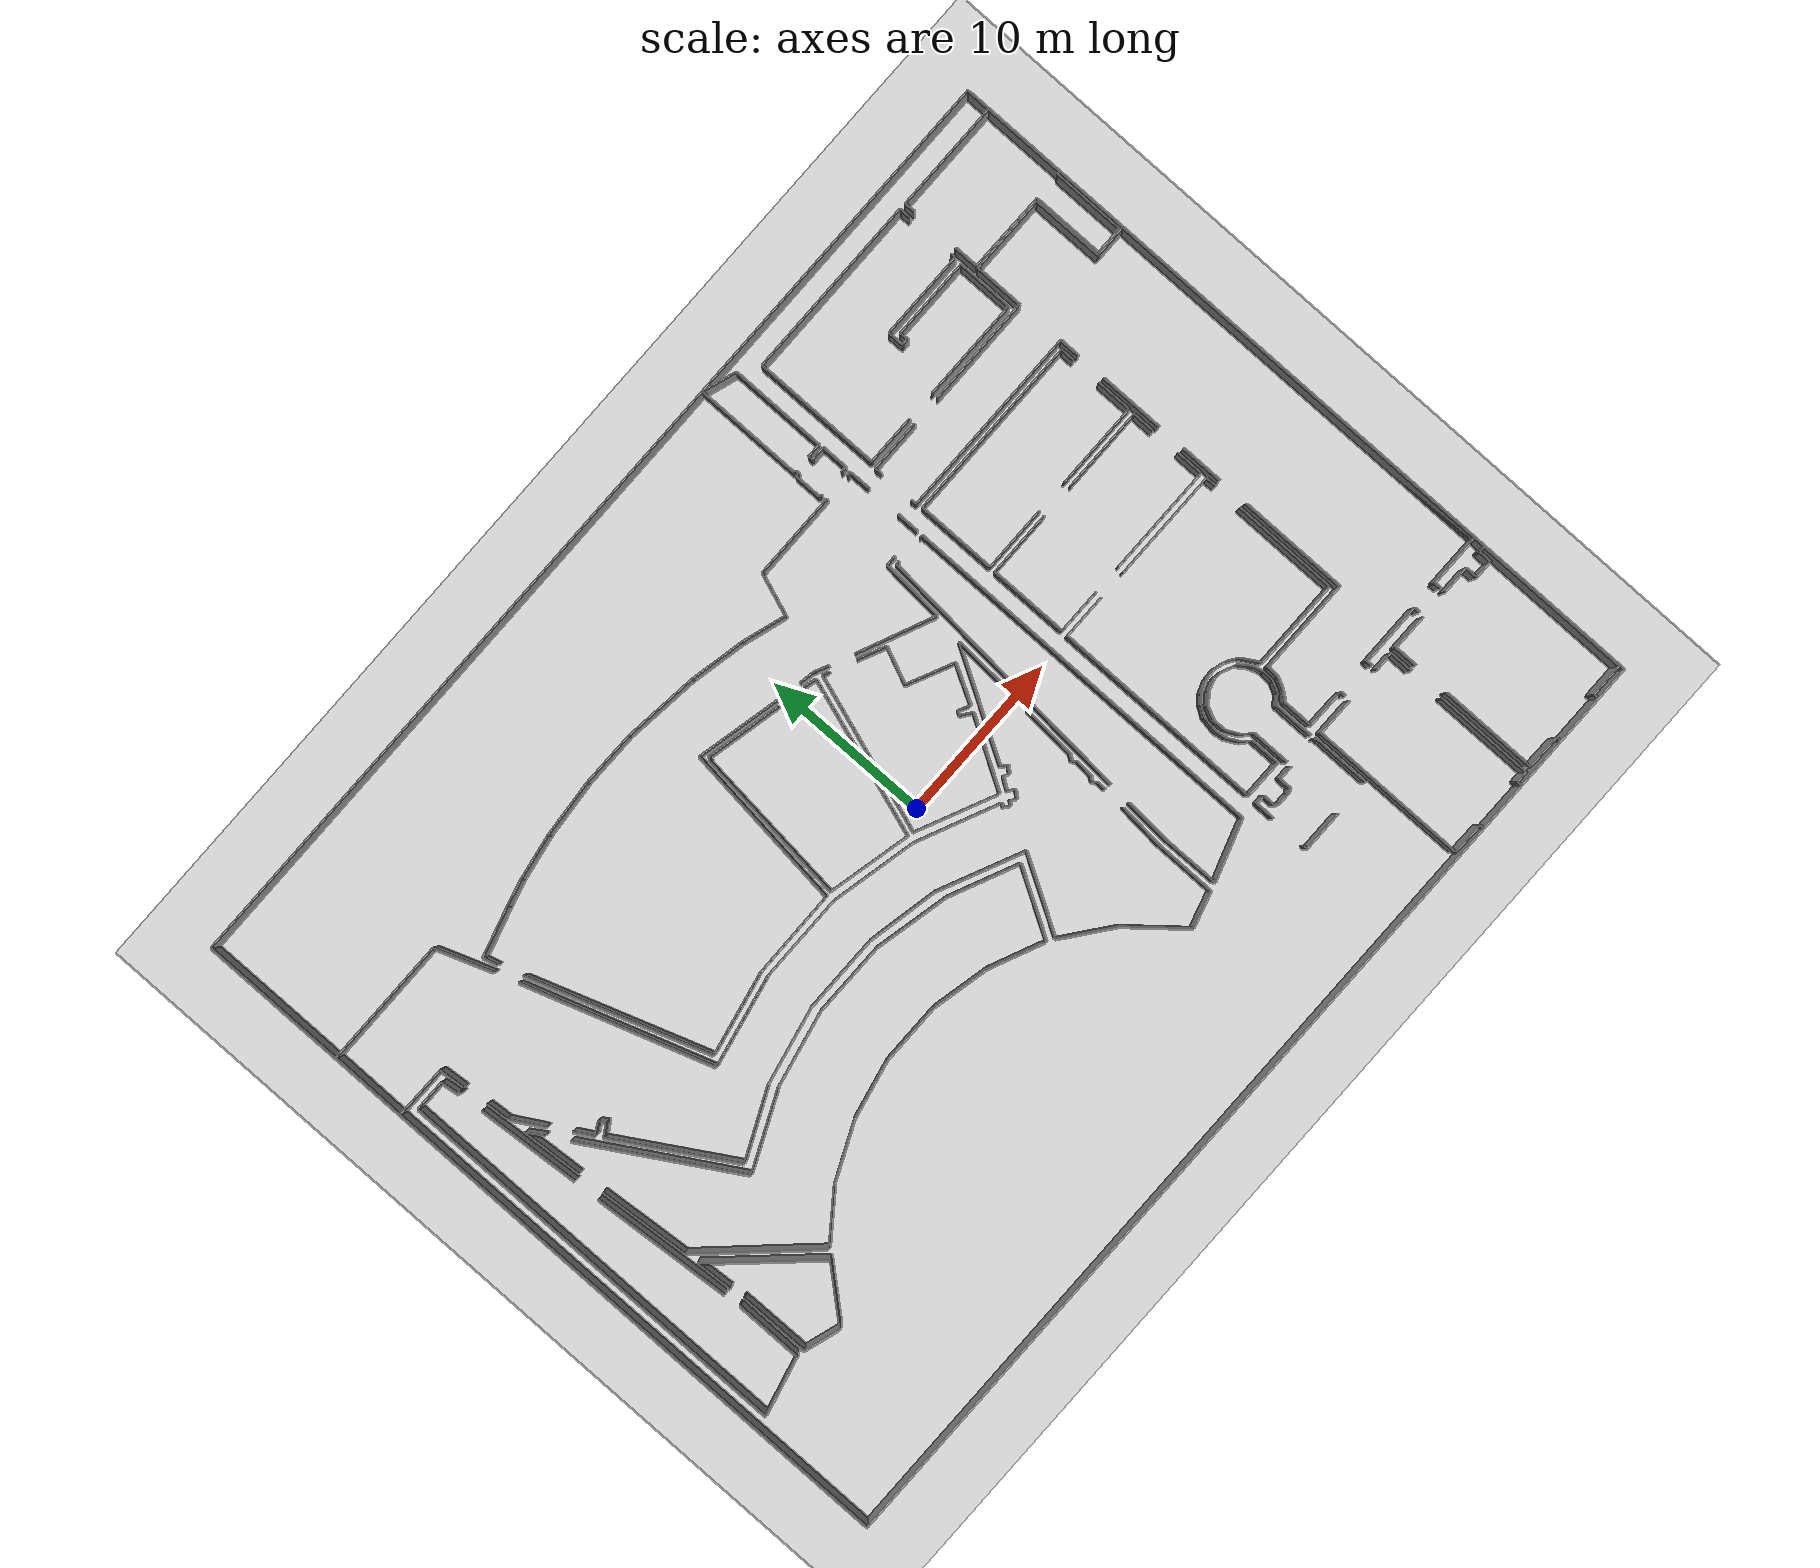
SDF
<sdf version="1.6">
  <world name="default">
    <light name="sun" type="directional">
      <cast_shadows>1</cast_shadows>
      <pose frame="">0 0 10 0 -0 0</pose>
      <diffuse>0.8 0.8 0.8 1</diffuse>
      <specular>0.1 0.1 0.1 1</specular>
      <attenuation>
        <range>1000</range>
        <constant>0.9</constant>
        <linear>0.01</linear>
        <quadratic>0.001</quadratic>
      </attenuation>
      <direction>-0.5 0.5 -1</direction>
    </light>
    <model name="ground_plane">
      <static>1</static>
      <link name="link">
        <collision name="collision">
          <geometry>
            <plane>
              <normal>0 0 1</normal>
              <size>100 100</size>
            </plane>
          </geometry>
          <surface>
            <friction>
              <ode>
                <mu>100</mu>
                <mu2>50</mu2>
              </ode>
              <torsional>
                <ode />
              </torsional>
            </friction>
            <contact>
              <ode />
            </contact>
            <bounce />
          </surface>
          <max_contacts>10</max_contacts>
        </collision>
        <visual name="visual">
          <cast_shadows>0</cast_shadows>
          <geometry>
            <plane>
              <normal>0 0 1</normal>
              <size>100 100</size>
            </plane>
          </geometry>
          <material>
            <script>
              <uri>file://media/materials/scripts/gazebo.material</uri>
              <name>Gazebo/Grey</name>
            </script>
          </material>
        </visual>
        <self_collide>0</self_collide>
        <kinematic>0</kinematic>
        <gravity>1</gravity>
      </link>
    </model>
    <gravity>0 0 -9.8</gravity>
    <magnetic_field>6e-06 2.3e-05 -4.2e-05</magnetic_field>
    <atmosphere type="adiabatic" />
    <physics default="0" name="default_physics" type="ode">
      <max_step_size>0.001</max_step_size>
      <real_time_factor>1</real_time_factor>
      <real_time_update_rate>1000</real_time_update_rate>
    </physics>
    <scene>
      <ambient>0.4 0.4 0.4 1</ambient>
      <background>0.7 0.7 0.7 1</background>
      <shadows>1</shadows>
    </scene>
    <spherical_coordinates>
      <surface_model>EARTH_WGS84</surface_model>
      <latitude_deg>0</latitude_deg>
      <longitude_deg>0</longitude_deg>
      <elevation>0</elevation>
      <heading_deg>0</heading_deg>
    </spherical_coordinates>
  <model name="50032446">
		<static>1</static>
		<link name="Wall_0">
			<collision name="Wall_0_Collision">
				<geometry>
					<box>
						<size>24.1739835477 0.1 2.5</size>
					</box>
				</geometry>
				<pose frame="">12.0869917738 0 1.25 0 0 0</pose>
			</collision>
			<visual name="Wall_0_Visual">
				<pose frame="">12.0869917738 0 1.25 0 0 0</pose>
				<geometry>
					<box>
						<size>24.1739835477 0.1 2.5</size>
					</box>
				</geometry>
				<material>
					<script>
						<uri>file://media/materials/scripts/gazebo.material</uri>
						<name>Gazebo/Grey</name>
					</script>
					<ambient>1 1 1 1</ambient>
				</material>
			</visual>
			<pose frame="">0.829860753686 -37.8040334028 0 0 0 1.57079632679</pose>
		</link>
		<link name="Wall_1">
			<collision name="Wall_1_Collision">
				<geometry>
					<box>
						<size>1.85060218915 0.1 2.5</size>
					</box>
				</geometry>
				<pose frame="">0.925301094577 0 1.25 0 0 0</pose>
			</collision>
			<visual name="Wall_1_Visual">
				<pose frame="">0.925301094577 0 1.25 0 0 0</pose>
				<geometry>
					<box>
						<size>1.85060218915 0.1 2.5</size>
					</box>
				</geometry>
				<material>
					<script>
						<uri>file://media/materials/scripts/gazebo.material</uri>
						<name>Gazebo/Grey</name>
					</script>
					<ambient>1 1 1 1</ambient>
				</material>
			</visual>
			<pose frame="">0.829860753686 -13.6300498552 0 0 0 0.0</pose>
		</link>
		<link name="Wall_2">
			<collision name="Wall_2_Collision">
				<geometry>
					<box>
						<size>1.08629447662 0.1 2.5</size>
					</box>
				</geometry>
				<pose frame="">0.54314723831 0 1.25 0 0 0</pose>
			</collision>
			<visual name="Wall_2_Visual">
				<pose frame="">0.54314723831 0 1.25 0 0 0</pose>
				<geometry>
					<box>
						<size>1.08629447662 0.1 2.5</size>
					</box>
				</geometry>
				<material>
					<script>
						<uri>file://media/materials/scripts/gazebo.material</uri>
						<name>Gazebo/Grey</name>
					</script>
					<ambient>1 1 1 1</ambient>
				</material>
			</visual>
			<pose frame="">2.68046294284 -13.6300498552 0 0 0 -1.43750263371</pose>
		</link>
		<link name="Wall_3">
			<collision name="Wall_3_Collision">
				<geometry>
					<box>
						<size>0.158855427582 0.1 2.5</size>
					</box>
				</geometry>
				<pose frame="">0.0794277137908 0 1.25 0 0 0</pose>
			</collision>
			<visual name="Wall_3_Visual">
				<pose frame="">0.0794277137908 0 1.25 0 0 0</pose>
				<geometry>
					<box>
						<size>0.158855427582 0.1 2.5</size>
					</box>
				</geometry>
				<material>
					<script>
						<uri>file://media/materials/scripts/gazebo.material</uri>
						<name>Gazebo/Grey</name>
					</script>
					<ambient>1 1 1 1</ambient>
				</material>
			</visual>
			<pose frame="">2.82483075543 -14.7067084012 0 0 0 0.0</pose>
		</link>
		<link name="Wall_4">
			<collision name="Wall_4_Collision">
				<geometry>
					<box>
						<size>6.10033639075 0.1 2.5</size>
					</box>
				</geometry>
				<pose frame="">3.05016819538 0 1.25 0 0 0</pose>
			</collision>
			<visual name="Wall_4_Visual">
				<pose frame="">3.05016819538 0 1.25 0 0 0</pose>
				<geometry>
					<box>
						<size>6.10033639075 0.1 2.5</size>
					</box>
				</geometry>
				<material>
					<script>
						<uri>file://media/materials/scripts/gazebo.material</uri>
						<name>Gazebo/Grey</name>
					</script>
					<ambient>1 1 1 1</ambient>
				</material>
			</visual>
			<pose frame="">2.98368618301 -16.1808867691 0 0 0 -1.49710813323</pose>
		</link>
		<link name="Wall_5">
			<collision name="Wall_5_Collision">
				<geometry>
					<box>
						<size>8.28211737133 0.1 2.5</size>
					</box>
				</geometry>
				<pose frame="">4.14105868566 0 1.25 0 0 0</pose>
			</collision>
			<visual name="Wall_5_Visual">
				<pose frame="">4.14105868566 0 1.25 0 0 0</pose>
				<geometry>
					<box>
						<size>8.28211737133 0.1 2.5</size>
					</box>
				</geometry>
				<material>
					<script>
						<uri>file://media/materials/scripts/gazebo.material</uri>
						<name>Gazebo/Grey</name>
					</script>
					<ambient>1 1 1 1</ambient>
				</material>
			</visual>
			<pose frame="">3.52074461258 -23.7835804488 0 0 0 -1.49396794606</pose>
		</link>
		<link name="Wall_6">
			<collision name="Wall_6_Collision">
				<geometry>
					<box>
						<size>3.99400670243 0.1 2.5</size>
					</box>
				</geometry>
				<pose frame="">1.99700335121 0 1.25 0 0 0</pose>
			</collision>
			<visual name="Wall_6_Visual">
				<pose frame="">1.99700335121 0 1.25 0 0 0</pose>
				<geometry>
					<box>
						<size>3.99400670243 0.1 2.5</size>
					</box>
				</geometry>
				<material>
					<script>
						<uri>file://media/materials/scripts/gazebo.material</uri>
						<name>Gazebo/Grey</name>
					</script>
					<ambient>1 1 1 1</ambient>
				</material>
			</visual>
			<pose frame="">4.25198791682 -32.9682200186 0 0 0 -1.57079632679</pose>
		</link>
		<link name="Wall_7">
			<collision name="Wall_7_Collision">
				<geometry>
					<box>
						<size>3.52414426638 0.1 2.5</size>
					</box>
				</geometry>
				<pose frame="">1.76207213319 0 1.25 0 0 0</pose>
			</collision>
			<visual name="Wall_7_Visual">
				<pose frame="">1.76207213319 0 1.25 0 0 0</pose>
				<geometry>
					<box>
						<size>3.52414426638 0.1 2.5</size>
					</box>
				</geometry>
				<material>
					<script>
						<uri>file://media/materials/scripts/gazebo.material</uri>
						<name>Gazebo/Grey</name>
					</script>
					<ambient>1 1 1 1</ambient>
				</material>
			</visual>
			<pose frame="">4.25198791682 -36.962226721 0 0 0 -2.90039231001</pose>
		</link>
		<link name="Wall_8">
			<collision name="Wall_8_Collision">
				<geometry>
					<box>
						<size>5.32268536726 0.1 2.5</size>
					</box>
				</geometry>
				<pose frame="">2.66134268363 0 1.25 0 0 0</pose>
			</collision>
			<visual name="Wall_8_Visual">
				<pose frame="">2.66134268363 0 1.25 0 0 0</pose>
				<geometry>
					<box>
						<size>5.32268536726 0.1 2.5</size>
					</box>
				</geometry>
				<material>
					<script>
						<uri>file://media/materials/scripts/gazebo.material</uri>
						<name>Gazebo/Grey</name>
					</script>
					<ambient>1 1 1 1</ambient>
				</material>
			</visual>
			<pose frame="">4.3676346681 -29.0288595832 0 0 0 1.65172872614</pose>
		</link>
		<link name="Wall_9">
			<collision name="Wall_9_Collision">
				<geometry>
					<box>
						<size>3.55922427608 0.1 2.5</size>
					</box>
				</geometry>
				<pose frame="">1.77961213804 0 1.25 0 0 0</pose>
			</collision>
			<visual name="Wall_9_Visual">
				<pose frame="">1.77961213804 0 1.25 0 0 0</pose>
				<geometry>
					<box>
						<size>3.55922427608 0.1 2.5</size>
					</box>
				</geometry>
				<material>
					<script>
						<uri>file://media/materials/scripts/gazebo.material</uri>
						<name>Gazebo/Grey</name>
					</script>
					<ambient>1 1 1 1</ambient>
				</material>
			</visual>
			<pose frame="">3.842267998 -22.1693551359 0 0 0 1.6419104536</pose>
		</link>
		<link name="Wall_10">
			<collision name="Wall_10_Collision">
				<geometry>
					<box>
						<size>1.06295947958 0.1 2.5</size>
					</box>
				</geometry>
				<pose frame="">0.531479739792 0 1.25 0 0 0</pose>
			</collision>
			<visual name="Wall_10_Visual">
				<pose frame="">0.531479739792 0 1.25 0 0 0</pose>
				<geometry>
					<box>
						<size>1.06295947958 0.1 2.5</size>
					</box>
				</geometry>
				<material>
					<script>
						<uri>file://media/materials/scripts/gazebo.material</uri>
						<name>Gazebo/Grey</name>
					</script>
					<ambient>1 1 1 1</ambient>
				</material>
			</visual>
			<pose frame="">3.58937015729 -18.619126956 0 0 0 -0.998180185512</pose>
		</link>
		<link name="Wall_11">
			<collision name="Wall_11_Collision">
				<geometry>
					<box>
						<size>9.55704429316 0.1 2.5</size>
					</box>
				</geometry>
				<pose frame="">4.77852214658 0 1.25 0 0 0</pose>
			</collision>
			<visual name="Wall_11_Visual">
				<pose frame="">4.77852214658 0 1.25 0 0 0</pose>
				<geometry>
					<box>
						<size>9.55704429316 0.1 2.5</size>
					</box>
				</geometry>
				<material>
					<script>
						<uri>file://media/materials/scripts/gazebo.material</uri>
						<name>Gazebo/Grey</name>
					</script>
					<ambient>1 1 1 1</ambient>
				</material>
			</visual>
			<pose frame="">4.84064258927 -20.6997518043 0 0 0 -1.03433121391</pose>
		</link>
		<link name="Wall_12">
			<collision name="Wall_12_Collision">
				<geometry>
					<box>
						<size>4.74820361784 0.1 2.5</size>
					</box>
				</geometry>
				<pose frame="">2.37410180892 0 1.25 0 0 0</pose>
			</collision>
			<visual name="Wall_12_Visual">
				<pose frame="">2.37410180892 0 1.25 0 0 0</pose>
				<geometry>
					<box>
						<size>4.74820361784 0.1 2.5</size>
					</box>
				</geometry>
				<material>
					<script>
						<uri>file://media/materials/scripts/gazebo.material</uri>
						<name>Gazebo/Grey</name>
					</script>
					<ambient>1 1 1 1</ambient>
				</material>
			</visual>
			<pose frame="">9.72525636089 -28.9142295067 0 0 0 0.423490957335</pose>
		</link>
		<link name="Wall_13">
			<collision name="Wall_13_Collision">
				<geometry>
					<box>
						<size>4.50643660933 0.1 2.5</size>
					</box>
				</geometry>
				<pose frame="">2.25321830466 0 1.25 0 0 0</pose>
			</collision>
			<visual name="Wall_13_Visual">
				<pose frame="">2.25321830466 0 1.25 0 0 0</pose>
				<geometry>
					<box>
						<size>4.50643660933 0.1 2.5</size>
					</box>
				</geometry>
				<material>
					<script>
						<uri>file://media/materials/scripts/gazebo.material</uri>
						<name>Gazebo/Grey</name>
					</script>
					<ambient>1 1 1 1</ambient>
				</material>
			</visual>
			<pose frame="">14.0540032203 -26.9629765186 0 0 0 0.214441688872</pose>
		</link>
		<link name="Wall_14">
			<collision name="Wall_14_Collision">
				<geometry>
					<box>
						<size>4.48481380662 0.1 2.5</size>
					</box>
				</geometry>
				<pose frame="">2.24240690331 0 1.25 0 0 0</pose>
			</collision>
			<visual name="Wall_14_Visual">
				<pose frame="">2.24240690331 0 1.25 0 0 0</pose>
				<geometry>
					<box>
						<size>4.48481380662 0.1 2.5</size>
					</box>
				</geometry>
				<material>
					<script>
						<uri>file://media/materials/scripts/gazebo.material</uri>
						<name>Gazebo/Grey</name>
					</script>
					<ambient>1 1 1 1</ambient>
				</material>
			</visual>
			<pose frame="">18.4572215042 -26.0039980734 0 0 0 -0.00181354292536</pose>
		</link>
		<link name="Wall_15">
			<collision name="Wall_15_Collision">
				<geometry>
					<box>
						<size>4.53220053649 0.1 2.5</size>
					</box>
				</geometry>
				<pose frame="">2.26610026825 0 1.25 0 0 0</pose>
			</collision>
			<visual name="Wall_15_Visual">
				<pose frame="">2.26610026825 0 1.25 0 0 0</pose>
				<geometry>
					<box>
						<size>4.53220053649 0.1 2.5</size>
					</box>
				</geometry>
				<material>
					<script>
						<uri>file://media/materials/scripts/gazebo.material</uri>
						<name>Gazebo/Grey</name>
					</script>
					<ambient>1 1 1 1</ambient>
				</material>
			</visual>
			<pose frame="">22.9420279357 -26.0121314713 0 0 0 -0.218887926637</pose>
		</link>
		<link name="Wall_16">
			<collision name="Wall_16_Collision">
				<geometry>
					<box>
						<size>4.20378438465 0.1 2.5</size>
					</box>
				</geometry>
				<pose frame="">2.10189219233 0 1.25 0 0 0</pose>
			</collision>
			<visual name="Wall_16_Visual">
				<pose frame="">2.10189219233 0 1.25 0 0 0</pose>
				<geometry>
					<box>
						<size>4.20378438465 0.1 2.5</size>
					</box>
				</geometry>
				<material>
					<script>
						<uri>file://media/materials/scripts/gazebo.material</uri>
						<name>Gazebo/Grey</name>
					</script>
					<ambient>1 1 1 1</ambient>
				</material>
			</visual>
			<pose frame="">27.3660880517 -26.9962726162 0 0 0 -0.423970440159</pose>
		</link>
		<link name="Wall_17">
			<collision name="Wall_17_Collision">
				<geometry>
					<box>
						<size>4.279005851 0.1 2.5</size>
					</box>
				</geometry>
				<pose frame="">2.1395029255 0 1.25 0 0 0</pose>
			</collision>
			<visual name="Wall_17_Visual">
				<pose frame="">2.1395029255 0 1.25 0 0 0</pose>
				<geometry>
					<box>
						<size>4.279005851 0.1 2.5</size>
					</box>
				</geometry>
				<material>
					<script>
						<uri>file://media/materials/scripts/gazebo.material</uri>
						<name>Gazebo/Grey</name>
					</script>
					<ambient>1 1 1 1</ambient>
				</material>
			</visual>
			<pose frame="">31.1976809649 -28.7256363431 0 0 0 -2.10239390479</pose>
		</link>
		<link name="Wall_18">
			<collision name="Wall_18_Collision">
				<geometry>
					<box>
						<size>3.35407861106 0.1 2.5</size>
					</box>
				</geometry>
				<pose frame="">1.67703930553 0 1.25 0 0 0</pose>
			</collision>
			<visual name="Wall_18_Visual">
				<pose frame="">1.67703930553 0 1.25 0 0 0</pose>
				<geometry>
					<box>
						<size>3.35407861106 0.1 2.5</size>
					</box>
				</geometry>
				<material>
					<script>
						<uri>file://media/materials/scripts/gazebo.material</uri>
						<name>Gazebo/Grey</name>
					</script>
					<ambient>1 1 1 1</ambient>
				</material>
			</visual>
			<pose frame="">29.0286054146 -32.4141322872 0 0 0 2.72506874094</pose>
		</link>
		<link name="Wall_19">
			<collision name="Wall_19_Collision">
				<geometry>
					<box>
						<size>3.47486728361 0.1 2.5</size>
					</box>
				</geometry>
				<pose frame="">1.7374336418 0 1.25 0 0 0</pose>
			</collision>
			<visual name="Wall_19_Visual">
				<pose frame="">1.7374336418 0 1.25 0 0 0</pose>
				<geometry>
					<box>
						<size>3.47486728361 0.1 2.5</size>
					</box>
				</geometry>
				<material>
					<script>
						<uri>file://media/materials/scripts/gazebo.material</uri>
						<name>Gazebo/Grey</name>
					</script>
					<ambient>1 1 1 1</ambient>
				</material>
			</visual>
			<pose frame="">25.9612977345 -31.0571256826 0 0 0 2.92260636075</pose>
		</link>
		<link name="Wall_20">
			<collision name="Wall_20_Collision">
				<geometry>
					<box>
						<size>3.71696283673 0.1 2.5</size>
					</box>
				</geometry>
				<pose frame="">1.85848141836 0 1.25 0 0 0</pose>
			</collision>
			<visual name="Wall_20_Visual">
				<pose frame="">1.85848141836 0 1.25 0 0 0</pose>
				<geometry>
					<box>
						<size>3.71696283673 0.1 2.5</size>
					</box>
				</geometry>
				<material>
					<script>
						<uri>file://media/materials/scripts/gazebo.material</uri>
						<name>Gazebo/Grey</name>
					</script>
					<ambient>1 1 1 1</ambient>
				</material>
			</visual>
			<pose frame="">22.5694166447 -30.3022446907 0 0 0 3.14159265359</pose>
		</link>
		<link name="Wall_21">
			<collision name="Wall_21_Collision">
				<geometry>
					<box>
						<size>3.47308468036 0.1 2.5</size>
					</box>
				</geometry>
				<pose frame="">1.73654234018 0 1.25 0 0 0</pose>
			</collision>
			<visual name="Wall_21_Visual">
				<pose frame="">1.73654234018 0 1.25 0 0 0</pose>
				<geometry>
					<box>
						<size>3.47308468036 0.1 2.5</size>
					</box>
				</geometry>
				<material>
					<script>
						<uri>file://media/materials/scripts/gazebo.material</uri>
						<name>Gazebo/Grey</name>
					</script>
					<ambient>1 1 1 1</ambient>
				</material>
			</visual>
			<pose frame="">18.852453808 -30.3022446907 0 0 0 -2.92526534497</pose>
		</link>
		<link name="Wall_22">
			<collision name="Wall_22_Collision">
				<geometry>
					<box>
						<size>3.60517069916 0.1 2.5</size>
					</box>
				</geometry>
				<pose frame="">1.80258534958 0 1.25 0 0 0</pose>
			</collision>
			<visual name="Wall_22_Visual">
				<pose frame="">1.80258534958 0 1.25 0 0 0</pose>
				<geometry>
					<box>
						<size>3.60517069916 0.1 2.5</size>
					</box>
				</geometry>
				<material>
					<script>
						<uri>file://media/materials/scripts/gazebo.material</uri>
						<name>Gazebo/Grey</name>
					</script>
					<ambient>1 1 1 1</ambient>
				</material>
			</visual>
			<pose frame="">15.4603185496 -31.0477214413 0 0 0 -2.71825011192</pose>
		</link>
		<link name="Wall_23">
			<collision name="Wall_23_Collision">
				<geometry>
					<box>
						<size>3.30429964282 0.1 2.5</size>
					</box>
				</geometry>
				<pose frame="">1.65214982141 0 1.25 0 0 0</pose>
			</collision>
			<visual name="Wall_23_Visual">
				<pose frame="">1.65214982141 0 1.25 0 0 0</pose>
				<geometry>
					<box>
						<size>3.30429964282 0.1 2.5</size>
					</box>
				</geometry>
				<material>
					<script>
						<uri>file://media/materials/scripts/gazebo.material</uri>
						<name>Gazebo/Grey</name>
					</script>
					<ambient>1 1 1 1</ambient>
				</material>
			</visual>
			<pose frame="">12.1734091264 -32.5287623637 0 0 0 -2.49984533519</pose>
		</link>
		<link name="Wall_24">
			<collision name="Wall_24_Collision">
				<geometry>
					<box>
						<size>7.52466770557 0.1 2.5</size>
					</box>
				</geometry>
				<pose frame="">3.76233385279 0 1.25 0 0 0</pose>
			</collision>
			<visual name="Wall_24_Visual">
				<pose frame="">3.76233385279 0 1.25 0 0 0</pose>
				<geometry>
					<box>
						<size>7.52466770557 0.1 2.5</size>
					</box>
				</geometry>
				<material>
					<script>
						<uri>file://media/materials/scripts/gazebo.material</uri>
						<name>Gazebo/Grey</name>
					</script>
					<ambient>1 1 1 1</ambient>
				</material>
			</visual>
			<pose frame="">9.5264964499 -34.5067030636 0 0 0 2.32621470609</pose>
		</link>
		<link name="Wall_25">
			<collision name="Wall_25_Collision">
				<geometry>
					<box>
						<size>1.18983791483 0.1 2.5</size>
					</box>
				</geometry>
				<pose frame="">0.594918957417 0 1.25 0 0 0</pose>
			</collision>
			<visual name="Wall_25_Visual">
				<pose frame="">0.594918957417 0 1.25 0 0 0</pose>
				<geometry>
					<box>
						<size>1.18983791483 0.1 2.5</size>
					</box>
				</geometry>
				<material>
					<script>
						<uri>file://media/materials/scripts/gazebo.material</uri>
						<name>Gazebo/Grey</name>
					</script>
					<ambient>1 1 1 1</ambient>
				</material>
			</visual>
			<pose frame="">5.87129660342 -21.4838621948 0 0 0 2.10586710902</pose>
		</link>
		<link name="Wall_26">
			<collision name="Wall_26_Collision">
				<geometry>
					<box>
						<size>2.13955775843 0.1 2.5</size>
					</box>
				</geometry>
				<pose frame="">1.06977887922 0 1.25 0 0 0</pose>
			</collision>
			<visual name="Wall_26_Visual">
				<pose frame="">1.06977887922 0 1.25 0 0 0</pose>
				<geometry>
					<box>
						<size>2.13955775843 0.1 2.5</size>
					</box>
				</geometry>
				<material>
					<script>
						<uri>file://media/materials/scripts/gazebo.material</uri>
						<name>Gazebo/Grey</name>
					</script>
					<ambient>1 1 1 1</ambient>
				</material>
			</visual>
			<pose frame="">4.55699033778 -19.2850489084 0 0 0 2.08988350223</pose>
		</link>
		<link name="Wall_27">
			<collision name="Wall_27_Collision">
				<geometry>
					<box>
						<size>1.29192081993 0.1 2.5</size>
					</box>
				</geometry>
				<pose frame="">0.645960409967 0 1.25 0 0 0</pose>
			</collision>
			<visual name="Wall_27_Visual">
				<pose frame="">0.645960409967 0 1.25 0 0 0</pose>
				<geometry>
					<box>
						<size>1.29192081993 0.1 2.5</size>
					</box>
				</geometry>
				<material>
					<script>
						<uri>file://media/materials/scripts/gazebo.material</uri>
						<name>Gazebo/Grey</name>
					</script>
					<ambient>1 1 1 1</ambient>
				</material>
			</visual>
			<pose frame="">3.49558191285 -17.4273299961 0 0 0 1.63931441809</pose>
		</link>
		<link name="Wall_28">
			<collision name="Wall_28_Collision">
				<geometry>
					<box>
						<size>1.51652392377 0.1 2.5</size>
					</box>
				</geometry>
				<pose frame="">0.758261961885 0 1.25 0 0 0</pose>
			</collision>
			<visual name="Wall_28_Visual">
				<pose frame="">0.758261961885 0 1.25 0 0 0</pose>
				<geometry>
					<box>
						<size>1.51652392377 0.1 2.5</size>
					</box>
				</geometry>
				<material>
					<script>
						<uri>file://media/materials/scripts/gazebo.material</uri>
						<name>Gazebo/Grey</name>
					</script>
					<ambient>1 1 1 1</ambient>
				</material>
			</visual>
			<pose frame="">3.23353399951 -14.6787498459 0 0 0 1.64763248955</pose>
		</link>
		<link name="Wall_29">
			<collision name="Wall_29_Collision">
				<geometry>
					<box>
						<size>3.11722836435 0.1 2.5</size>
					</box>
				</geometry>
				<pose frame="">1.55861418217 0 1.25 0 0 0</pose>
			</collision>
			<visual name="Wall_29_Visual">
				<pose frame="">1.55861418217 0 1.25 0 0 0</pose>
				<geometry>
					<box>
						<size>3.11722836435 0.1 2.5</size>
					</box>
				</geometry>
				<material>
					<script>
						<uri>file://media/materials/scripts/gazebo.material</uri>
						<name>Gazebo/Grey</name>
					</script>
					<ambient>1 1 1 1</ambient>
				</material>
			</visual>
			<pose frame="">3.11712474218 -13.166700344 0 0 0 3.13343888778</pose>
		</link>
		<link name="Wall_30">
			<collision name="Wall_30_Collision">
				<geometry>
					<box>
						<size>4.47193606022 0.1 2.5</size>
					</box>
				</geometry>
				<pose frame="">2.23596803011 0 1.25 0 0 0</pose>
			</collision>
			<visual name="Wall_30_Visual">
				<pose frame="">2.23596803011 0 1.25 0 0 0</pose>
				<geometry>
					<box>
						<size>4.47193606022 0.1 2.5</size>
					</box>
				</geometry>
				<material>
					<script>
						<uri>file://media/materials/scripts/gazebo.material</uri>
						<name>Gazebo/Grey</name>
					</script>
					<ambient>1 1 1 1</ambient>
				</material>
			</visual>
			<pose frame="">0.0 -13.1412834756 0 0 0 1.56437377102</pose>
		</link>
		<link name="Wall_31">
			<collision name="Wall_31_Collision">
				<geometry>
					<box>
						<size>7.61540211392 0.1 2.5</size>
					</box>
				</geometry>
				<pose frame="">3.80770105696 0 1.25 0 0 0</pose>
			</collision>
			<visual name="Wall_31_Visual">
				<pose frame="">3.80770105696 0 1.25 0 0 0</pose>
				<geometry>
					<box>
						<size>7.61540211392 0.1 2.5</size>
					</box>
				</geometry>
				<material>
					<script>
						<uri>file://media/materials/scripts/gazebo.material</uri>
						<name>Gazebo/Grey</name>
					</script>
					<ambient>1 1 1 1</ambient>
				</material>
			</visual>
			<pose frame="">0.0287210613068 -8.66943964701 0 0 0 0.0</pose>
		</link>
		<link name="Wall_32">
			<collision name="Wall_32_Collision">
				<geometry>
					<box>
						<size>3.40149536224 0.1 2.5</size>
					</box>
				</geometry>
				<pose frame="">1.70074768112 0 1.25 0 0 0</pose>
			</collision>
			<visual name="Wall_32_Visual">
				<pose frame="">1.70074768112 0 1.25 0 0 0</pose>
				<geometry>
					<box>
						<size>3.40149536224 0.1 2.5</size>
					</box>
				</geometry>
				<material>
					<script>
						<uri>file://media/materials/scripts/gazebo.material</uri>
						<name>Gazebo/Grey</name>
					</script>
					<ambient>1 1 1 1</ambient>
				</material>
			</visual>
			<pose frame="">7.64412317523 -8.66943964701 0 0 0 -1.22817952382</pose>
		</link>
		<link name="Wall_33">
			<collision name="Wall_33_Collision">
				<geometry>
					<box>
						<size>11.1890046702 0.1 2.5</size>
					</box>
				</geometry>
				<pose frame="">5.59450233509 0 1.25 0 0 0</pose>
			</collision>
			<visual name="Wall_33_Visual">
				<pose frame="">5.59450233509 0 1.25 0 0 0</pose>
				<geometry>
					<box>
						<size>11.1890046702 0.1 2.5</size>
					</box>
				</geometry>
				<material>
					<script>
						<uri>file://media/materials/scripts/gazebo.material</uri>
						<name>Gazebo/Grey</name>
					</script>
					<ambient>1 1 1 1</ambient>
				</material>
			</visual>
			<pose frame="">9.23750665604 -13.2030464658 0 0 0 -1.25215619345</pose>
		</link>
		<link name="Wall_34">
			<collision name="Wall_34_Collision">
				<geometry>
					<box>
						<size>5.43961863873 0.1 2.5</size>
					</box>
				</geometry>
				<pose frame="">2.71980931937 0 1.25 0 0 0</pose>
			</collision>
			<visual name="Wall_34_Visual">
				<pose frame="">2.71980931937 0 1.25 0 0 0</pose>
				<geometry>
					<box>
						<size>5.43961863873 0.1 2.5</size>
					</box>
				</geometry>
				<material>
					<script>
						<uri>file://media/materials/scripts/gazebo.material</uri>
						<name>Gazebo/Grey</name>
					</script>
					<ambient>1 1 1 1</ambient>
				</material>
			</visual>
			<pose frame="">12.7427469789 -23.8288224746 0 0 0 0.208071376055</pose>
		</link>
		<link name="Wall_35">
			<collision name="Wall_35_Collision">
				<geometry>
					<box>
						<size>5.22674560975 0.1 2.5</size>
					</box>
				</geometry>
				<pose frame="">2.61337280487 0 1.25 0 0 0</pose>
			</collision>
			<visual name="Wall_35_Visual">
				<pose frame="">2.61337280487 0 1.25 0 0 0</pose>
				<geometry>
					<box>
						<size>5.22674560975 0.1 2.5</size>
					</box>
				</geometry>
				<material>
					<script>
						<uri>file://media/materials/scripts/gazebo.material</uri>
						<name>Gazebo/Grey</name>
					</script>
					<ambient>1 1 1 1</ambient>
				</material>
			</visual>
			<pose frame="">18.0650392246 -22.7051427221 0 0 0 0.00282045546605</pose>
		</link>
		<link name="Wall_36">
			<collision name="Wall_36_Collision">
				<geometry>
					<box>
						<size>5.16999772746 0.1 2.5</size>
					</box>
				</geometry>
				<pose frame="">2.58499886373 0 1.25 0 0 0</pose>
			</collision>
			<visual name="Wall_36_Visual">
				<pose frame="">2.58499886373 0 1.25 0 0 0</pose>
				<geometry>
					<box>
						<size>5.16999772746 0.1 2.5</size>
					</box>
				</geometry>
				<material>
					<script>
						<uri>file://media/materials/scripts/gazebo.material</uri>
						<name>Gazebo/Grey</name>
					</script>
					<ambient>1 1 1 1</ambient>
				</material>
			</visual>
			<pose frame="">23.291764045 -22.6904009384 0 0 0 -0.218087714903</pose>
		</link>
		<link name="Wall_37">
			<collision name="Wall_37_Collision">
				<geometry>
					<box>
						<size>5.02176744036 0.1 2.5</size>
					</box>
				</geometry>
				<pose frame="">2.51088372018 0 1.25 0 0 0</pose>
			</collision>
			<visual name="Wall_37_Visual">
				<pose frame="">2.51088372018 0 1.25 0 0 0</pose>
				<geometry>
					<box>
						<size>5.02176744036 0.1 2.5</size>
					</box>
				</geometry>
				<material>
					<script>
						<uri>file://media/materials/scripts/gazebo.material</uri>
						<name>Gazebo/Grey</name>
					</script>
					<ambient>1 1 1 1</ambient>
				</material>
			</visual>
			<pose frame="">28.3392999432 -23.8089973172 0 0 0 -0.425362476963</pose>
		</link>
		<link name="Wall_38">
			<collision name="Wall_38_Collision">
				<geometry>
					<box>
						<size>0.234969566457 0.1 2.5</size>
					</box>
				</geometry>
				<pose frame="">0.117484783228 0 1.25 0 0 0</pose>
			</collision>
			<visual name="Wall_38_Visual">
				<pose frame="">0.117484783228 0 1.25 0 0 0</pose>
				<geometry>
					<box>
						<size>0.234969566457 0.1 2.5</size>
					</box>
				</geometry>
				<material>
					<script>
						<uri>file://media/materials/scripts/gazebo.material</uri>
						<name>Gazebo/Grey</name>
					</script>
					<ambient>1 1 1 1</ambient>
				</material>
			</visual>
			<pose frame="">32.9135737515 -25.881234599 0 0 0 -2.20261471312</pose>
		</link>
		<link name="Wall_39">
			<collision name="Wall_39_Collision">
				<geometry>
					<box>
						<size>0.404486842103 0.1 2.5</size>
					</box>
				</geometry>
				<pose frame="">0.202243421052 0 1.25 0 0 0</pose>
			</collision>
			<visual name="Wall_39_Visual">
				<pose frame="">0.202243421052 0 1.25 0 0 0</pose>
				<geometry>
					<box>
						<size>0.404486842103 0.1 2.5</size>
					</box>
				</geometry>
				<material>
					<script>
						<uri>file://media/materials/scripts/gazebo.material</uri>
						<name>Gazebo/Grey</name>
					</script>
					<ambient>1 1 1 1</ambient>
				</material>
			</visual>
			<pose frame="">32.77479765 -26.0708444373 0 0 0 -0.675427890104</pose>
		</link>
		<link name="Wall_40">
			<collision name="Wall_40_Collision">
				<geometry>
					<box>
						<size>0.286121244982 0.1 2.5</size>
					</box>
				</geometry>
				<pose frame="">0.143060622491 0 1.25 0 0 0</pose>
			</collision>
			<visual name="Wall_40_Visual">
				<pose frame="">0.143060622491 0 1.25 0 0 0</pose>
				<geometry>
					<box>
						<size>0.286121244982 0.1 2.5</size>
					</box>
				</geometry>
				<material>
					<script>
						<uri>file://media/materials/scripts/gazebo.material</uri>
						<name>Gazebo/Grey</name>
					</script>
					<ambient>1 1 1 1</ambient>
				</material>
			</visual>
			<pose frame="">33.0904751556 -26.323742278 0 0 0 0.785398163397</pose>
		</link>
		<link name="Wall_41">
			<collision name="Wall_41_Collision">
				<geometry>
					<box>
						<size>0.379067178921 0.1 2.5</size>
					</box>
				</geometry>
				<pose frame="">0.18953358946 0 1.25 0 0 0</pose>
			</collision>
			<visual name="Wall_41_Visual">
				<pose frame="">0.18953358946 0 1.25 0 0 0</pose>
				<geometry>
					<box>
						<size>0.379067178921 0.1 2.5</size>
					</box>
				</geometry>
				<material>
					<script>
						<uri>file://media/materials/scripts/gazebo.material</uri>
						<name>Gazebo/Grey</name>
					</script>
					<ambient>1 1 1 1</ambient>
				</material>
			</visual>
			<pose frame="">33.2927934282 -26.1214240055 0 0 0 -0.643635210978</pose>
		</link>
		<link name="Wall_42">
			<collision name="Wall_42_Collision">
				<geometry>
					<box>
						<size>0.5258211981 0.1 2.5</size>
					</box>
				</geometry>
				<pose frame="">0.26291059905 0 1.25 0 0 0</pose>
			</collision>
			<visual name="Wall_42_Visual">
				<pose frame="">0.26291059905 0 1.25 0 0 0</pose>
				<geometry>
					<box>
						<size>0.5258211981 0.1 2.5</size>
					</box>
				</geometry>
				<material>
					<script>
						<uri>file://media/materials/scripts/gazebo.material</uri>
						<name>Gazebo/Grey</name>
					</script>
					<ambient>1 1 1 1</ambient>
				</material>
			</visual>
			<pose frame="">33.5960166684 -26.3489049778 0 0 0 0.885713008364</pose>
		</link>
		<link name="Wall_43">
			<collision name="Wall_43_Collision">
				<geometry>
					<box>
						<size>0.455324168266 0.1 2.5</size>
					</box>
				</geometry>
				<pose frame="">0.227662084133 0 1.25 0 0 0</pose>
			</collision>
			<visual name="Wall_43_Visual">
				<pose frame="">0.227662084133 0 1.25 0 0 0</pose>
				<geometry>
					<box>
						<size>0.455324168266 0.1 2.5</size>
					</box>
				</geometry>
				<material>
					<script>
						<uri>file://media/materials/scripts/gazebo.material</uri>
						<name>Gazebo/Grey</name>
					</script>
					<ambient>1 1 1 1</ambient>
				</material>
			</visual>
			<pose frame="">33.9287234759 -25.9417267458 0 0 0 2.51394550892</pose>
		</link>
		<link name="Wall_44">
			<collision name="Wall_44_Collision">
				<geometry>
					<box>
						<size>0.793586963241 0.1 2.5</size>
					</box>
				</geometry>
				<pose frame="">0.39679348162 0 1.25 0 0 0</pose>
			</collision>
			<visual name="Wall_44_Visual">
				<pose frame="">0.39679348162 0 1.25 0 0 0</pose>
				<geometry>
					<box>
						<size>0.793586963241 0.1 2.5</size>
					</box>
				</geometry>
				<material>
					<script>
						<uri>file://media/materials/scripts/gazebo.material</uri>
						<name>Gazebo/Grey</name>
					</script>
					<ambient>1 1 1 1</ambient>
				</material>
			</visual>
			<pose frame="">33.5601788839 -25.6743412901 0 0 0 0.992742759811</pose>
		</link>
		<link name="Wall_45">
			<collision name="Wall_45_Collision">
				<geometry>
					<box>
						<size>0.359213643791 0.1 2.5</size>
					</box>
				</geometry>
				<pose frame="">0.179606821896 0 1.25 0 0 0</pose>
			</collision>
			<visual name="Wall_45_Visual">
				<pose frame="">0.179606821896 0 1.25 0 0 0</pose>
				<geometry>
					<box>
						<size>0.359213643791 0.1 2.5</size>
					</box>
				</geometry>
				<material>
					<script>
						<uri>file://media/materials/scripts/gazebo.material</uri>
						<name>Gazebo/Grey</name>
					</script>
					<ambient>1 1 1 1</ambient>
				</material>
			</visual>
			<pose frame="">33.993790659 -25.0096901811 0 0 0 -0.526342760232</pose>
		</link>
		<link name="Wall_46">
			<collision name="Wall_46_Collision">
				<geometry>
					<box>
						<size>0.477217323221 0.1 2.5</size>
					</box>
				</geometry>
				<pose frame="">0.23860866161 0 1.25 0 0 0</pose>
			</collision>
			<visual name="Wall_46_Visual">
				<pose frame="">0.23860866161 0 1.25 0 0 0</pose>
				<geometry>
					<box>
						<size>0.477217323221 0.1 2.5</size>
					</box>
				</geometry>
				<material>
					<script>
						<uri>file://media/materials/scripts/gazebo.material</uri>
						<name>Gazebo/Grey</name>
					</script>
					<ambient>1 1 1 1</ambient>
				</material>
			</visual>
			<pose frame="">34.3043847911 -25.1901499468 0 0 0 0.881581726008</pose>
		</link>
		<link name="Wall_47">
			<collision name="Wall_47_Collision">
				<geometry>
					<box>
						<size>0.420919379641 0.1 2.5</size>
					</box>
				</geometry>
				<pose frame="">0.21045968982 0 1.25 0 0 0</pose>
			</collision>
			<visual name="Wall_47_Visual">
				<pose frame="">0.21045968982 0 1.25 0 0 0</pose>
				<geometry>
					<box>
						<size>0.420919379641 0.1 2.5</size>
					</box>
				</geometry>
				<material>
					<script>
						<uri>file://media/materials/scripts/gazebo.material</uri>
						<name>Gazebo/Grey</name>
					</script>
					<ambient>1 1 1 1</ambient>
				</material>
			</visual>
			<pose frame="">34.6078621999 -24.8218595235 0 0 0 2.4532714843</pose>
		</link>
		<link name="Wall_48">
			<collision name="Wall_48_Collision">
				<geometry>
					<box>
						<size>6.83458041471 0.1 2.5</size>
					</box>
				</geometry>
				<pose frame="">3.41729020735 0 1.25 0 0 0</pose>
			</collision>
			<visual name="Wall_48_Visual">
				<pose frame="">3.41729020735 0 1.25 0 0 0</pose>
				<geometry>
					<box>
						<size>6.83458041471 0.1 2.5</size>
					</box>
				</geometry>
				<material>
					<script>
						<uri>file://media/materials/scripts/gazebo.material</uri>
						<name>Gazebo/Grey</name>
					</script>
					<ambient>1 1 1 1</ambient>
				</material>
			</visual>
			<pose frame="">34.2827804529 -24.5544740678 0 0 0 1.04044116084</pose>
		</link>
		<link name="Wall_49">
			<collision name="Wall_49_Collision">
				<geometry>
					<box>
						<size>3.61417899457 0.1 2.5</size>
					</box>
				</geometry>
				<pose frame="">1.80708949728 0 1.25 0 0 0</pose>
			</collision>
			<visual name="Wall_49_Visual">
				<pose frame="">1.80708949728 0 1.25 0 0 0</pose>
				<geometry>
					<box>
						<size>3.61417899457 0.1 2.5</size>
					</box>
				</geometry>
				<material>
					<script>
						<uri>file://media/materials/scripts/gazebo.material</uri>
						<name>Gazebo/Grey</name>
					</script>
					<ambient>1 1 1 1</ambient>
				</material>
			</visual>
			<pose frame="">37.7399828944 -18.6587772707 0 0 0 -1.6308199528</pose>
		</link>
		<link name="Wall_50">
			<collision name="Wall_50_Collision">
				<geometry>
					<box>
						<size>0.134041151757 0.1 2.5</size>
					</box>
				</geometry>
				<pose frame="">0.0670205758785 0 1.25 0 0 0</pose>
			</collision>
			<visual name="Wall_50_Visual">
				<pose frame="">0.0670205758785 0 1.25 0 0 0</pose>
				<geometry>
					<box>
						<size>0.134041151757 0.1 2.5</size>
					</box>
				</geometry>
				<material>
					<script>
						<uri>file://media/materials/scripts/gazebo.material</uri>
						<name>Gazebo/Grey</name>
					</script>
					<ambient>1 1 1 1</ambient>
				</material>
			</visual>
			<pose frame="">37.5231770069 -22.2664475733 0 0 0 -0.0721180563398</pose>
		</link>
		<link name="Wall_51">
			<collision name="Wall_51_Collision">
				<geometry>
					<box>
						<size>0.151105366927 0.1 2.5</size>
					</box>
				</geometry>
				<pose frame="">0.0755526834636 0 1.25 0 0 0</pose>
			</collision>
			<visual name="Wall_51_Visual">
				<pose frame="">0.0755526834636 0 1.25 0 0 0</pose>
				<geometry>
					<box>
						<size>0.151105366927 0.1 2.5</size>
					</box>
				</geometry>
				<material>
					<script>
						<uri>file://media/materials/scripts/gazebo.material</uri>
						<name>Gazebo/Grey</name>
					</script>
					<ambient>1 1 1 1</ambient>
				</material>
			</visual>
			<pose frame="">37.5325812482 -23.6806421318 0 0 0 -2.81984209919</pose>
		</link>
		<link name="Wall_52">
			<collision name="Wall_52_Collision">
				<geometry>
					<box>
						<size>3.14623467171 0.1 2.5</size>
					</box>
				</geometry>
				<pose frame="">1.57311733585 0 1.25 0 0 0</pose>
			</collision>
			<visual name="Wall_52_Visual">
				<pose frame="">1.57311733585 0 1.25 0 0 0</pose>
				<geometry>
					<box>
						<size>3.14623467171 0.1 2.5</size>
					</box>
				</geometry>
				<material>
					<script>
						<uri>file://media/materials/scripts/gazebo.material</uri>
						<name>Gazebo/Grey</name>
					</script>
					<ambient>1 1 1 1</ambient>
				</material>
			</visual>
			<pose frame="">37.3892301103 -23.7284258444 0 0 0 -1.63627899473</pose>
		</link>
		<link name="Wall_53">
			<collision name="Wall_53_Collision">
				<geometry>
					<box>
						<size>0.362244860986 0.1 2.5</size>
					</box>
				</geometry>
				<pose frame="">0.181122430493 0 1.25 0 0 0</pose>
			</collision>
			<visual name="Wall_53_Visual">
				<pose frame="">0.181122430493 0 1.25 0 0 0</pose>
				<geometry>
					<box>
						<size>0.362244860986 0.1 2.5</size>
					</box>
				</geometry>
				<material>
					<script>
						<uri>file://media/materials/scripts/gazebo.material</uri>
						<name>Gazebo/Grey</name>
					</script>
					<ambient>1 1 1 1</ambient>
				</material>
			</visual>
			<pose frame="">37.1833534762 -26.8679174308 0 0 0 -2.20980686796</pose>
		</link>
		<link name="Wall_54">
			<collision name="Wall_54_Collision">
				<geometry>
					<box>
						<size>0.283537442398 0.1 2.5</size>
					</box>
				</geometry>
				<pose frame="">0.141768721199 0 1.25 0 0 0</pose>
			</collision>
			<visual name="Wall_54_Visual">
				<pose frame="">0.141768721199 0 1.25 0 0 0</pose>
				<geometry>
					<box>
						<size>0.283537442398 0.1 2.5</size>
					</box>
				</geometry>
				<material>
					<script>
						<uri>file://media/materials/scripts/gazebo.material</uri>
						<name>Gazebo/Grey</name>
					</script>
					<ambient>1 1 1 1</ambient>
				</material>
			</visual>
			<pose frame="">36.9673100947 -27.1586864054 0 0 0 -1.01561775067</pose>
		</link>
		<link name="Wall_55">
			<collision name="Wall_55_Collision">
				<geometry>
					<box>
						<size>1.02416299092 0.1 2.5</size>
					</box>
				</geometry>
				<pose frame="">0.512081495459 0 1.25 0 0 0</pose>
			</collision>
			<visual name="Wall_55_Visual">
				<pose frame="">0.512081495459 0 1.25 0 0 0</pose>
				<geometry>
					<box>
						<size>1.02416299092 0.1 2.5</size>
					</box>
				</geometry>
				<material>
					<script>
						<uri>file://media/materials/scripts/gazebo.material</uri>
						<name>Gazebo/Grey</name>
					</script>
					<ambient>1 1 1 1</ambient>
				</material>
			</visual>
			<pose frame="">37.116761281 -27.399638318 0 0 0 -1.63561462442</pose>
		</link>
		<link name="Wall_56">
			<collision name="Wall_56_Collision">
				<geometry>
					<box>
						<size>0.339147705268 0.1 2.5</size>
					</box>
				</geometry>
				<pose frame="">0.169573852634 0 1.25 0 0 0</pose>
			</collision>
			<visual name="Wall_56_Visual">
				<pose frame="">0.169573852634 0 1.25 0 0 0</pose>
				<geometry>
					<box>
						<size>0.339147705268 0.1 2.5</size>
					</box>
				</geometry>
				<material>
					<script>
						<uri>file://media/materials/scripts/gazebo.material</uri>
						<name>Gazebo/Grey</name>
					</script>
					<ambient>1 1 1 1</ambient>
				</material>
			</visual>
			<pose frame="">37.0504232544 -28.4216505969 0 0 0 -2.19975791157</pose>
		</link>
		<link name="Wall_57">
			<collision name="Wall_57_Collision">
				<geometry>
					<box>
						<size>0.299457311063 0.1 2.5</size>
					</box>
				</geometry>
				<pose frame="">0.149728655532 0 1.25 0 0 0</pose>
			</collision>
			<visual name="Wall_57_Visual">
				<pose frame="">0.149728655532 0 1.25 0 0 0</pose>
				<geometry>
					<box>
						<size>0.299457311063 0.1 2.5</size>
					</box>
				</geometry>
				<material>
					<script>
						<uri>file://media/materials/scripts/gazebo.material</uri>
						<name>Gazebo/Grey</name>
					</script>
					<ambient>1 1 1 1</ambient>
				</material>
			</visual>
			<pose frame="">36.8509008374 -28.695898607 0 0 0 -0.982322913489</pose>
		</link>
		<link name="Wall_58">
			<collision name="Wall_58_Collision">
				<geometry>
					<box>
						<size>0.517759265075 0.1 2.5</size>
					</box>
				</geometry>
				<pose frame="">0.258879632538 0 1.25 0 0 0</pose>
			</collision>
			<visual name="Wall_58_Visual">
				<pose frame="">0.258879632538 0 1.25 0 0 0</pose>
				<geometry>
					<box>
						<size>0.517759265075 0.1 2.5</size>
					</box>
				</geometry>
				<material>
					<script>
						<uri>file://media/materials/scripts/gazebo.material</uri>
						<name>Gazebo/Grey</name>
					</script>
					<ambient>1 1 1 1</ambient>
				</material>
			</visual>
			<pose frame="">37.0171271568 -28.9449839175 0 0 0 -1.60320148215</pose>
		</link>
		<link name="Wall_59">
			<collision name="Wall_59_Collision">
				<geometry>
					<box>
						<size>2.67150305465 0.1 2.5</size>
					</box>
				</geometry>
				<pose frame="">1.33575152733 0 1.25 0 0 0</pose>
			</collision>
			<visual name="Wall_59_Visual">
				<pose frame="">1.33575152733 0 1.25 0 0 0</pose>
				<geometry>
					<box>
						<size>2.67150305465 0.1 2.5</size>
					</box>
				</geometry>
				<material>
					<script>
						<uri>file://media/materials/scripts/gazebo.material</uri>
						<name>Gazebo/Grey</name>
					</script>
					<ambient>1 1 1 1</ambient>
				</material>
			</visual>
			<pose frame="">36.9068179479 -30.7971111187 0 0 0 -1.65557306755</pose>
		</link>
		<link name="Wall_60">
			<collision name="Wall_60_Collision">
				<geometry>
					<box>
						<size>3.63286189022 0.1 2.5</size>
					</box>
				</geometry>
				<pose frame="">1.81643094511 0 1.25 0 0 0</pose>
			</collision>
			<visual name="Wall_60_Visual">
				<pose frame="">1.81643094511 0 1.25 0 0 0</pose>
				<geometry>
					<box>
						<size>3.63286189022 0.1 2.5</size>
					</box>
				</geometry>
				<material>
					<script>
						<uri>file://media/materials/scripts/gazebo.material</uri>
						<name>Gazebo/Grey</name>
					</script>
					<ambient>1 1 1 1</ambient>
				</material>
			</visual>
			<pose frame="">36.680607819 -33.4590197476 0 0 0 -1.57478427179</pose>
		</link>
		<link name="Wall_61">
			<collision name="Wall_61_Collision">
				<geometry>
					<box>
						<size>2.14794624063 0.1 2.5</size>
					</box>
				</geometry>
				<pose frame="">1.07397312032 0 1.25 0 0 0</pose>
			</collision>
			<visual name="Wall_61_Visual">
				<pose frame="">1.07397312032 0 1.25 0 0 0</pose>
				<geometry>
					<box>
						<size>2.14794624063 0.1 2.5</size>
					</box>
				</geometry>
				<material>
					<script>
						<uri>file://media/materials/scripts/gazebo.material</uri>
						<name>Gazebo/Grey</name>
					</script>
					<ambient>1 1 1 1</ambient>
				</material>
			</visual>
			<pose frame="">36.666120204 -37.0918527499 0 0 0 -2.86041602968</pose>
		</link>
		<link name="Wall_62">
			<collision name="Wall_62_Collision">
				<geometry>
					<box>
						<size>3.84258173228 0.1 2.5</size>
					</box>
				</geometry>
				<pose frame="">1.92129086614 0 1.25 0 0 0</pose>
			</collision>
			<visual name="Wall_62_Visual">
				<pose frame="">1.92129086614 0 1.25 0 0 0</pose>
				<geometry>
					<box>
						<size>3.84258173228 0.1 2.5</size>
					</box>
				</geometry>
				<material>
					<script>
						<uri>file://media/materials/scripts/gazebo.material</uri>
						<name>Gazebo/Grey</name>
					</script>
					<ambient>1 1 1 1</ambient>
				</material>
			</visual>
			<pose frame="">34.6025246575 -37.6878783142 0 0 0 2.26730463256</pose>
		</link>
		<link name="Wall_63">
			<collision name="Wall_63_Collision">
				<geometry>
					<box>
						<size>3.39345985358 0.1 2.5</size>
					</box>
				</geometry>
				<pose frame="">1.69672992679 0 1.25 0 0 0</pose>
			</collision>
			<visual name="Wall_63_Visual">
				<pose frame="">1.69672992679 0 1.25 0 0 0</pose>
				<geometry>
					<box>
						<size>3.39345985358 0.1 2.5</size>
					</box>
				</geometry>
				<material>
					<script>
						<uri>file://media/materials/scripts/gazebo.material</uri>
						<name>Gazebo/Grey</name>
					</script>
					<ambient>1 1 1 1</ambient>
				</material>
			</visual>
			<pose frame="">32.1373425902 -34.7402840843 0 0 0 2.48706610471</pose>
		</link>
		<link name="Wall_64">
			<collision name="Wall_64_Collision">
				<geometry>
					<box>
						<size>4.81957316876 0.1 2.5</size>
					</box>
				</geometry>
				<pose frame="">2.40978658438 0 1.25 0 0 0</pose>
			</collision>
			<visual name="Wall_64_Visual">
				<pose frame="">2.40978658438 0 1.25 0 0 0</pose>
				<geometry>
					<box>
						<size>4.81957316876 0.1 2.5</size>
					</box>
				</geometry>
				<material>
					<script>
						<uri>file://media/materials/scripts/gazebo.material</uri>
						<name>Gazebo/Grey</name>
					</script>
					<ambient>1 1 1 1</ambient>
				</material>
			</visual>
			<pose frame="">29.4451878878 -32.6744010197 0 0 0 1.04000008908</pose>
		</link>
		<link name="Wall_65">
			<collision name="Wall_65_Collision">
				<geometry>
					<box>
						<size>5.19399997077 0.1 2.5</size>
					</box>
				</geometry>
				<pose frame="">2.59699998539 0 1.25 0 0 0</pose>
			</collision>
			<visual name="Wall_65_Visual">
				<pose frame="">2.59699998539 0 1.25 0 0 0</pose>
				<geometry>
					<box>
						<size>5.19399997077 0.1 2.5</size>
					</box>
				</geometry>
				<material>
					<script>
						<uri>file://media/materials/scripts/gazebo.material</uri>
						<name>Gazebo/Grey</name>
					</script>
					<ambient>1 1 1 1</ambient>
				</material>
			</visual>
			<pose frame="">31.8849530868 -28.5179805281 0 0 0 2.71206948212</pose>
		</link>
		<link name="Wall_66">
			<collision name="Wall_66_Collision">
				<geometry>
					<box>
						<size>4.23124031098 0.1 2.5</size>
					</box>
				</geometry>
				<pose frame="">2.11562015549 0 1.25 0 0 0</pose>
			</collision>
			<visual name="Wall_66_Visual">
				<pose frame="">2.11562015549 0 1.25 0 0 0</pose>
				<geometry>
					<box>
						<size>4.23124031098 0.1 2.5</size>
					</box>
				</geometry>
				<material>
					<script>
						<uri>file://media/materials/scripts/gazebo.material</uri>
						<name>Gazebo/Grey</name>
					</script>
					<ambient>1 1 1 1</ambient>
				</material>
			</visual>
			<pose frame="">27.1627531044 -26.3550050262 0 0 0 2.93873086479</pose>
		</link>
		<link name="Wall_67">
			<collision name="Wall_67_Collision">
				<geometry>
					<box>
						<size>4.7295708743 0.1 2.5</size>
					</box>
				</geometry>
				<pose frame="">2.36478543715 0 1.25 0 0 0</pose>
			</collision>
			<visual name="Wall_67_Visual">
				<pose frame="">2.36478543715 0 1.25 0 0 0</pose>
				<geometry>
					<box>
						<size>4.7295708743 0.1 2.5</size>
					</box>
				</geometry>
				<material>
					<script>
						<uri>file://media/materials/scripts/gazebo.material</uri>
						<name>Gazebo/Grey</name>
					</script>
					<ambient>1 1 1 1</ambient>
				</material>
			</visual>
			<pose frame="">23.0182785409 -25.5025232596 0 0 0 3.14159265359</pose>
		</link>
		<link name="Wall_68">
			<collision name="Wall_68_Collision">
				<geometry>
					<box>
						<size>4.58241704642 0.1 2.5</size>
					</box>
				</geometry>
				<pose frame="">2.29120852321 0 1.25 0 0 0</pose>
			</collision>
			<visual name="Wall_68_Visual">
				<pose frame="">2.29120852321 0 1.25 0 0 0</pose>
				<geometry>
					<box>
						<size>4.58241704642 0.1 2.5</size>
					</box>
				</geometry>
				<material>
					<script>
						<uri>file://media/materials/scripts/gazebo.material</uri>
						<name>Gazebo/Grey</name>
					</script>
					<ambient>1 1 1 1</ambient>
				</material>
			</visual>
			<pose frame="">18.2887076666 -25.5025232596 0 0 0 -2.92843452025</pose>
		</link>
		<link name="Wall_69">
			<collision name="Wall_69_Collision">
				<geometry>
					<box>
						<size>4.2697785824 0.1 2.5</size>
					</box>
				</geometry>
				<pose frame="">2.1348892912 0 1.25 0 0 0</pose>
			</collision>
			<visual name="Wall_69_Visual">
				<pose frame="">2.1348892912 0 1.25 0 0 0</pose>
				<geometry>
					<box>
						<size>4.2697785824 0.1 2.5</size>
					</box>
				</geometry>
				<material>
					<script>
						<uri>file://media/materials/scripts/gazebo.material</uri>
						<name>Gazebo/Grey</name>
					</script>
					<ambient>1 1 1 1</ambient>
				</material>
			</visual>
			<pose frame="">13.8100012836 -26.4719226209 0 0 0 -2.70949669591</pose>
		</link>
		<link name="Wall_70">
			<collision name="Wall_70_Collision">
				<geometry>
					<box>
						<size>7.4390831489 0.1 2.5</size>
					</box>
				</geometry>
				<pose frame="">3.71954157445 0 1.25 0 0 0</pose>
			</collision>
			<visual name="Wall_70_Visual">
				<pose frame="">3.71954157445 0 1.25 0 0 0</pose>
				<geometry>
					<box>
						<size>7.4390831489 0.1 2.5</size>
					</box>
				</geometry>
				<material>
					<script>
						<uri>file://media/materials/scripts/gazebo.material</uri>
						<name>Gazebo/Grey</name>
					</script>
					<ambient>1 1 1 1</ambient>
				</material>
			</visual>
			<pose frame="">9.93265800714 -28.2599993137 0 0 0 2.11123926521</pose>
		</link>
		<link name="Wall_71">
			<collision name="Wall_71_Collision">
				<geometry>
					<box>
						<size>0.807853841565 0.1 2.5</size>
					</box>
				</geometry>
				<pose frame="">0.403926920783 0 1.25 0 0 0</pose>
			</collision>
			<visual name="Wall_71_Visual">
				<pose frame="">0.403926920783 0 1.25 0 0 0</pose>
				<geometry>
					<box>
						<size>0.807853841565 0.1 2.5</size>
					</box>
				</geometry>
				<material>
					<script>
						<uri>file://media/materials/scripts/gazebo.material</uri>
						<name>Gazebo/Grey</name>
					</script>
					<ambient>1 1 1 1</ambient>
				</material>
			</visual>
			<pose frame="">6.10513179282 -21.8811278481 0 0 0 0.555797921971</pose>
		</link>
		<link name="Wall_72">
			<collision name="Wall_72_Collision">
				<geometry>
					<box>
						<size>0.418924430595 0.1 2.5</size>
					</box>
				</geometry>
				<pose frame="">0.209462215297 0 1.25 0 0 0</pose>
			</collision>
			<visual name="Wall_72_Visual">
				<pose frame="">0.209462215297 0 1.25 0 0 0</pose>
				<geometry>
					<box>
						<size>0.418924430595 0.1 2.5</size>
					</box>
				</geometry>
				<material>
					<script>
						<uri>file://media/materials/scripts/gazebo.material</uri>
						<name>Gazebo/Grey</name>
					</script>
					<ambient>1 1 1 1</ambient>
				</material>
			</visual>
			<pose frame="">6.79138723997 -21.4548869648 0 0 0 2.1347335553</pose>
		</link>
		<link name="Wall_73">
			<collision name="Wall_73_Collision">
				<geometry>
					<box>
						<size>0.794583911101 0.1 2.5</size>
					</box>
				</geometry>
				<pose frame="">0.397291955551 0 1.25 0 0 0</pose>
			</collision>
			<visual name="Wall_73_Visual">
				<pose frame="">0.397291955551 0 1.25 0 0 0</pose>
				<geometry>
					<box>
						<size>0.794583911101 0.1 2.5</size>
					</box>
				</geometry>
				<material>
					<script>
						<uri>file://media/materials/scripts/gazebo.material</uri>
						<name>Gazebo/Grey</name>
					</script>
					<ambient>1 1 1 1</ambient>
				</material>
			</visual>
			<pose frame="">6.56746462925 -21.1008299878 0 0 0 -2.6385952882</pose>
		</link>
		<link name="Wall_74">
			<collision name="Wall_74_Collision">
				<geometry>
					<box>
						<size>10.7547165875 0.1 2.5</size>
					</box>
				</geometry>
				<pose frame="">5.37735829373 0 1.25 0 0 0</pose>
			</collision>
			<visual name="Wall_74_Visual">
				<pose frame="">5.37735829373 0 1.25 0 0 0</pose>
				<geometry>
					<box>
						<size>10.7547165875 0.1 2.5</size>
					</box>
				</geometry>
				<material>
					<script>
						<uri>file://media/materials/scripts/gazebo.material</uri>
						<name>Gazebo/Grey</name>
					</script>
					<ambient>1 1 1 1</ambient>
				</material>
			</visual>
			<pose frame="">13.117645788 -23.3281101669 0 0 0 1.89714308962</pose>
		</link>
		<link name="Wall_75">
			<collision name="Wall_75_Collision">
				<geometry>
					<box>
						<size>0.824879237004 0.1 2.5</size>
					</box>
				</geometry>
				<pose frame="">0.412439618502 0 1.25 0 0 0</pose>
			</collision>
			<visual name="Wall_75_Visual">
				<pose frame="">0.412439618502 0 1.25 0 0 0</pose>
				<geometry>
					<box>
						<size>0.824879237004 0.1 2.5</size>
					</box>
				</geometry>
				<material>
					<script>
						<uri>file://media/materials/scripts/gazebo.material</uri>
						<name>Gazebo/Grey</name>
					</script>
					<ambient>1 1 1 1</ambient>
				</material>
			</visual>
			<pose frame="">9.18591041316 -11.7479307492 0 0 0 1.82018419833</pose>
		</link>
		<link name="Wall_76">
			<collision name="Wall_76_Collision">
				<geometry>
					<box>
						<size>2.96220750891 0.1 2.5</size>
					</box>
				</geometry>
				<pose frame="">1.48110375446 0 1.25 0 0 0</pose>
			</collision>
			<visual name="Wall_76_Visual">
				<pose frame="">1.48110375446 0 1.25 0 0 0</pose>
				<geometry>
					<box>
						<size>2.96220750891 0.1 2.5</size>
					</box>
				</geometry>
				<material>
					<script>
						<uri>file://media/materials/scripts/gazebo.material</uri>
						<name>Gazebo/Grey</name>
					</script>
					<ambient>1 1 1 1</ambient>
				</material>
			</visual>
			<pose frame="">8.98232129718 -10.9485702376 0 0 0 0.278323231124</pose>
		</link>
		<link name="Wall_77">
			<collision name="Wall_77_Collision">
				<geometry>
					<box>
						<size>1.59074975212 0.1 2.5</size>
					</box>
				</geometry>
				<pose frame="">0.795374876058 0 1.25 0 0 0</pose>
			</collision>
			<visual name="Wall_77_Visual">
				<pose frame="">0.795374876058 0 1.25 0 0 0</pose>
				<geometry>
					<box>
						<size>1.59074975212 0.1 2.5</size>
					</box>
				</geometry>
				<material>
					<script>
						<uri>file://media/materials/scripts/gazebo.material</uri>
						<name>Gazebo/Grey</name>
					</script>
					<ambient>1 1 1 1</ambient>
				</material>
			</visual>
			<pose frame="">11.8305355715 -10.134722111 0 0 0 0.253891773858</pose>
		</link>
		<link name="Wall_78">
			<collision name="Wall_78_Collision">
				<geometry>
					<box>
						<size>2.69580585327 0.1 2.5</size>
					</box>
				</geometry>
				<pose frame="">1.34790292664 0 1.25 0 0 0</pose>
			</collision>
			<visual name="Wall_78_Visual">
				<pose frame="">1.34790292664 0 1.25 0 0 0</pose>
				<geometry>
					<box>
						<size>2.69580585327 0.1 2.5</size>
					</box>
				</geometry>
				<material>
					<script>
						<uri>file://media/materials/scripts/gazebo.material</uri>
						<name>Gazebo/Grey</name>
					</script>
					<ambient>1 1 1 1</ambient>
				</material>
			</visual>
			<pose frame="">13.37028946 -9.73516893957 0 0 0 0.173022774526</pose>
		</link>
		<link name="Wall_79">
			<collision name="Wall_79_Collision">
				<geometry>
					<box>
						<size>3.39498808591 0.1 2.5</size>
					</box>
				</geometry>
				<pose frame="">1.69749404295 0 1.25 0 0 0</pose>
			</collision>
			<visual name="Wall_79_Visual">
				<pose frame="">1.69749404295 0 1.25 0 0 0</pose>
				<geometry>
					<box>
						<size>3.39498808591 0.1 2.5</size>
					</box>
				</geometry>
				<material>
					<script>
						<uri>file://media/materials/scripts/gazebo.material</uri>
						<name>Gazebo/Grey</name>
					</script>
					<ambient>1 1 1 1</ambient>
				</material>
			</visual>
			<pose frame="">16.0258438718 -9.27105692235 0 0 0 0.0850001969323</pose>
		</link>
		<link name="Wall_80">
			<collision name="Wall_80_Collision">
				<geometry>
					<box>
						<size>3.26713987834 0.1 2.5</size>
					</box>
				</geometry>
				<pose frame="">1.63356993917 0 1.25 0 0 0</pose>
			</collision>
			<visual name="Wall_80_Visual">
				<pose frame="">1.63356993917 0 1.25 0 0 0</pose>
				<geometry>
					<box>
						<size>3.26713987834 0.1 2.5</size>
					</box>
				</geometry>
				<material>
					<script>
						<uri>file://media/materials/scripts/gazebo.material</uri>
						<name>Gazebo/Grey</name>
					</script>
					<ambient>1 1 1 1</ambient>
				</material>
			</visual>
			<pose frame="">19.4085748889 -8.98282963454 0 0 0 -0.00583469339558</pose>
		</link>
		<link name="Wall_81">
			<collision name="Wall_81_Collision">
				<geometry>
					<box>
						<size>4.45061373806 0.1 2.5</size>
					</box>
				</geometry>
				<pose frame="">2.22530686903 0 1.25 0 0 0</pose>
			</collision>
			<visual name="Wall_81_Visual">
				<pose frame="">2.22530686903 0 1.25 0 0 0</pose>
				<geometry>
					<box>
						<size>4.45061373806 0.1 2.5</size>
					</box>
				</geometry>
				<material>
					<script>
						<uri>file://media/materials/scripts/gazebo.material</uri>
						<name>Gazebo/Grey</name>
					</script>
					<ambient>1 1 1 1</ambient>
				</material>
			</visual>
			<pose frame="">22.6756591547 -9.00189228585 0 0 0 -0.116881874477</pose>
		</link>
		<link name="Wall_82">
			<collision name="Wall_82_Collision">
				<geometry>
					<box>
						<size>3.2417902446 0.1 2.5</size>
					</box>
				</geometry>
				<pose frame="">1.6208951223 0 1.25 0 0 0</pose>
			</collision>
			<visual name="Wall_82_Visual">
				<pose frame="">1.6208951223 0 1.25 0 0 0</pose>
				<geometry>
					<box>
						<size>3.2417902446 0.1 2.5</size>
					</box>
				</geometry>
				<material>
					<script>
						<uri>file://media/materials/scripts/gazebo.material</uri>
						<name>Gazebo/Grey</name>
					</script>
					<ambient>1 1 1 1</ambient>
				</material>
			</visual>
			<pose frame="">27.0959067404 -9.52090473885 0 0 0 -0.208974135449</pose>
		</link>
		<link name="Wall_83">
			<collision name="Wall_83_Collision">
				<geometry>
					<box>
						<size>2.6196080356 0.1 2.5</size>
					</box>
				</geometry>
				<pose frame="">1.3098040178 0 1.25 0 0 0</pose>
			</collision>
			<visual name="Wall_83_Visual">
				<pose frame="">1.3098040178 0 1.25 0 0 0</pose>
				<geometry>
					<box>
						<size>2.6196080356 0.1 2.5</size>
					</box>
				</geometry>
				<material>
					<script>
						<uri>file://media/materials/scripts/gazebo.material</uri>
						<name>Gazebo/Grey</name>
					</script>
					<ambient>1 1 1 1</ambient>
				</material>
			</visual>
			<pose frame="">30.2671694123 -10.1934350771 0 0 0 -0.305611045138</pose>
		</link>
		<link name="Wall_84">
			<collision name="Wall_84_Collision">
				<geometry>
					<box>
						<size>2.54915910462 0.1 2.5</size>
					</box>
				</geometry>
				<pose frame="">1.27457955231 0 1.25 0 0 0</pose>
			</collision>
			<visual name="Wall_84_Visual">
				<pose frame="">1.27457955231 0 1.25 0 0 0</pose>
				<geometry>
					<box>
						<size>2.54915910462 0.1 2.5</size>
					</box>
				</geometry>
				<material>
					<script>
						<uri>file://media/materials/scripts/gazebo.material</uri>
						<name>Gazebo/Grey</name>
					</script>
					<ambient>1 1 1 1</ambient>
				</material>
			</visual>
			<pose frame="">32.7653934086 -10.9816121665 0 0 0 1.22069643166</pose>
		</link>
		<link name="Wall_85">
			<collision name="Wall_85_Collision">
				<geometry>
					<box>
						<size>5.12989184725 0.1 2.5</size>
					</box>
				</geometry>
				<pose frame="">2.56494592362 0 1.25 0 0 0</pose>
			</collision>
			<visual name="Wall_85_Visual">
				<pose frame="">2.56494592362 0 1.25 0 0 0</pose>
				<geometry>
					<box>
						<size>5.12989184725 0.1 2.5</size>
					</box>
				</geometry>
				<material>
					<script>
						<uri>file://media/materials/scripts/gazebo.material</uri>
						<name>Gazebo/Grey</name>
					</script>
					<ambient>1 1 1 1</ambient>
				</material>
			</visual>
			<pose frame="">33.6397336821 -8.58708899335 0 0 0 0.0014368518081</pose>
		</link>
		<link name="Wall_86">
			<collision name="Wall_86_Collision">
				<geometry>
					<box>
						<size>0.247051960975 0.1 2.5</size>
					</box>
				</geometry>
				<pose frame="">0.123525980487 0 1.25 0 0 0</pose>
			</collision>
			<visual name="Wall_86_Visual">
				<pose frame="">0.123525980487 0 1.25 0 0 0</pose>
				<geometry>
					<box>
						<size>0.247051960975 0.1 2.5</size>
					</box>
				</geometry>
				<material>
					<script>
						<uri>file://media/materials/scripts/gazebo.material</uri>
						<name>Gazebo/Grey</name>
					</script>
					<ambient>1 1 1 1</ambient>
				</material>
			</visual>
			<pose frame="">40.3574120036 -8.59445988519 0 0 0 0.0</pose>
		</link>
		<link name="Wall_87">
			<collision name="Wall_87_Collision">
				<geometry>
					<box>
						<size>1.24237652803 0.1 2.5</size>
					</box>
				</geometry>
				<pose frame="">0.621188264015 0 1.25 0 0 0</pose>
			</collision>
			<visual name="Wall_87_Visual">
				<pose frame="">0.621188264015 0 1.25 0 0 0</pose>
				<geometry>
					<box>
						<size>1.24237652803 0.1 2.5</size>
					</box>
				</geometry>
				<material>
					<script>
						<uri>file://media/materials/scripts/gazebo.material</uri>
						<name>Gazebo/Grey</name>
					</script>
					<ambient>1 1 1 1</ambient>
				</material>
			</visual>
			<pose frame="">40.6044639646 -8.59445988519 0 0 0 -1.57079632679</pose>
		</link>
		<link name="Wall_88">
			<collision name="Wall_88_Collision">
				<geometry>
					<box>
						<size>1.32243966353 0.1 2.5</size>
					</box>
				</geometry>
				<pose frame="">0.661219831766 0 1.25 0 0 0</pose>
			</collision>
			<visual name="Wall_88_Visual">
				<pose frame="">0.661219831766 0 1.25 0 0 0</pose>
				<geometry>
					<box>
						<size>1.32243966353 0.1 2.5</size>
					</box>
				</geometry>
				<material>
					<script>
						<uri>file://media/materials/scripts/gazebo.material</uri>
						<name>Gazebo/Grey</name>
					</script>
					<ambient>1 1 1 1</ambient>
				</material>
			</visual>
			<pose frame="">40.6044639646 -11.8785734528 0 0 0 -1.57079632679</pose>
		</link>
		<link name="Wall_89">
			<collision name="Wall_89_Collision">
				<geometry>
					<box>
						<size>0.601617275337 0.1 2.5</size>
					</box>
				</geometry>
				<pose frame="">0.300808637669 0 1.25 0 0 0</pose>
			</collision>
			<visual name="Wall_89_Visual">
				<pose frame="">0.300808637669 0 1.25 0 0 0</pose>
				<geometry>
					<box>
						<size>0.601617275337 0.1 2.5</size>
					</box>
				</geometry>
				<material>
					<script>
						<uri>file://media/materials/scripts/gazebo.material</uri>
						<name>Gazebo/Grey</name>
					</script>
					<ambient>1 1 1 1</ambient>
				</material>
			</visual>
			<pose frame="">38.8611209601 -13.2010131164 0 0 0 3.14159265359</pose>
		</link>
		<link name="Wall_90">
			<collision name="Wall_90_Collision">
				<geometry>
					<box>
						<size>3.70451247746 0.1 2.5</size>
					</box>
				</geometry>
				<pose frame="">1.85225623873 0 1.25 0 0 0</pose>
			</collision>
			<visual name="Wall_90_Visual">
				<pose frame="">1.85225623873 0 1.25 0 0 0</pose>
				<geometry>
					<box>
						<size>3.70451247746 0.1 2.5</size>
					</box>
				</geometry>
				<material>
					<script>
						<uri>file://media/materials/scripts/gazebo.material</uri>
						<name>Gazebo/Grey</name>
					</script>
					<ambient>1 1 1 1</ambient>
				</material>
			</visual>
			<pose frame="">38.2595036848 -13.2010131164 0 0 0 -1.64303745705</pose>
		</link>
		<link name="Wall_91">
			<collision name="Wall_91_Collision">
				<geometry>
					<box>
						<size>4.72152969649 0.1 2.5</size>
					</box>
				</geometry>
				<pose frame="">2.36076484824 0 1.25 0 0 0</pose>
			</collision>
			<visual name="Wall_91_Visual">
				<pose frame="">2.36076484824 0 1.25 0 0 0</pose>
				<geometry>
					<box>
						<size>4.72152969649 0.1 2.5</size>
					</box>
				</geometry>
				<material>
					<script>
						<uri>file://media/materials/scripts/gazebo.material</uri>
						<name>Gazebo/Grey</name>
					</script>
					<ambient>1 1 1 1</ambient>
				</material>
			</visual>
			<pose frame="">37.9921182291 -16.8958632776 0 0 0 2.72799240422</pose>
		</link>
		<link name="Wall_92">
			<collision name="Wall_92_Collision">
				<geometry>
					<box>
						<size>0.842125445099 0.1 2.5</size>
					</box>
				</geometry>
				<pose frame="">0.421062722549 0 1.25 0 0 0</pose>
			</collision>
			<visual name="Wall_92_Visual">
				<pose frame="">0.421062722549 0 1.25 0 0 0</pose>
				<geometry>
					<box>
						<size>0.842125445099 0.1 2.5</size>
					</box>
				</geometry>
				<material>
					<script>
						<uri>file://media/materials/scripts/gazebo.material</uri>
						<name>Gazebo/Grey</name>
					</script>
					<ambient>1 1 1 1</ambient>
				</material>
			</visual>
			<pose frame="">32.3198357054 -14.3945892571 0 0 0 2.69130817998</pose>
		</link>
		<link name="Wall_93">
			<collision name="Wall_93_Collision">
				<geometry>
					<box>
						<size>0.937128452002 0.1 2.5</size>
					</box>
				</geometry>
				<pose frame="">0.468564226001 0 1.25 0 0 0</pose>
			</collision>
			<visual name="Wall_93_Visual">
				<pose frame="">0.468564226001 0 1.25 0 0 0</pose>
				<geometry>
					<box>
						<size>0.937128452002 0.1 2.5</size>
					</box>
				</geometry>
				<material>
					<script>
						<uri>file://media/materials/scripts/gazebo.material</uri>
						<name>Gazebo/Grey</name>
					</script>
					<ambient>1 1 1 1</ambient>
				</material>
			</visual>
			<pose frame="">31.5616505206 -14.0280780145 0 0 0 2.96547500561</pose>
		</link>
		<link name="Wall_94">
			<collision name="Wall_94_Collision">
				<geometry>
					<box>
						<size>4.99848779132 0.1 2.5</size>
					</box>
				</geometry>
				<pose frame="">2.49924389566 0 1.25 0 0 0</pose>
			</collision>
			<visual name="Wall_94_Visual">
				<pose frame="">2.49924389566 0 1.25 0 0 0</pose>
				<geometry>
					<box>
						<size>4.99848779132 0.1 2.5</size>
					</box>
				</geometry>
				<material>
					<script>
						<uri>file://media/materials/scripts/gazebo.material</uri>
						<name>Gazebo/Grey</name>
					</script>
					<ambient>1 1 1 1</ambient>
				</material>
			</visual>
			<pose frame="">29.1569606 -13.5654910094 0 0 0 2.91996195454</pose>
		</link>
		<link name="Wall_95">
			<collision name="Wall_95_Collision">
				<geometry>
					<box>
						<size>9.84946114627 0.1 2.5</size>
					</box>
				</geometry>
				<pose frame="">4.92473057313 0 1.25 0 0 0</pose>
			</collision>
			<visual name="Wall_95_Visual">
				<pose frame="">4.92473057313 0 1.25 0 0 0</pose>
				<geometry>
					<box>
						<size>9.84946114627 0.1 2.5</size>
					</box>
				</geometry>
				<material>
					<script>
						<uri>file://media/materials/scripts/gazebo.material</uri>
						<name>Gazebo/Grey</name>
					</script>
					<ambient>1 1 1 1</ambient>
				</material>
			</visual>
			<pose frame="">24.280734395 -12.4667197879 0 0 0 -1.68276727064</pose>
		</link>
		<link name="Wall_96">
			<collision name="Wall_96_Collision">
				<geometry>
					<box>
						<size>5.23252553188 0.1 2.5</size>
					</box>
				</geometry>
				<pose frame="">2.61626276594 0 1.25 0 0 0</pose>
			</collision>
			<visual name="Wall_96_Visual">
				<pose frame="">2.61626276594 0 1.25 0 0 0</pose>
				<geometry>
					<box>
						<size>5.23252553188 0.1 2.5</size>
					</box>
				</geometry>
				<material>
					<script>
						<uri>file://media/materials/scripts/gazebo.material</uri>
						<name>Gazebo/Grey</name>
					</script>
					<ambient>1 1 1 1</ambient>
				</material>
			</visual>
			<pose frame="">23.1801839927 -22.2545016451 0 0 0 -3.13265477832</pose>
		</link>
		<link name="Wall_97">
			<collision name="Wall_97_Collision">
				<geometry>
					<box>
						<size>4.93816209186 0.1 2.5</size>
					</box>
				</geometry>
				<pose frame="">2.46908104593 0 1.25 0 0 0</pose>
			</collision>
			<visual name="Wall_97_Visual">
				<pose frame="">2.46908104593 0 1.25 0 0 0</pose>
				<geometry>
					<box>
						<size>4.93816209186 0.1 2.5</size>
					</box>
				</geometry>
				<material>
					<script>
						<uri>file://media/materials/scripts/gazebo.material</uri>
						<name>Gazebo/Grey</name>
					</script>
					<ambient>1 1 1 1</ambient>
				</material>
			</visual>
			<pose frame="">17.9478674612 -22.301268683 0 0 0 -2.93212418952</pose>
		</link>
		<link name="Wall_98">
			<collision name="Wall_98_Collision">
				<geometry>
					<box>
						<size>9.25534686642 0.1 2.5</size>
					</box>
				</geometry>
				<pose frame="">4.62767343321 0 1.25 0 0 0</pose>
			</collision>
			<visual name="Wall_98_Visual">
				<pose frame="">4.62767343321 0 1.25 0 0 0</pose>
				<geometry>
					<box>
						<size>9.25534686642 0.1 2.5</size>
					</box>
				</geometry>
				<material>
					<script>
						<uri>file://media/materials/scripts/gazebo.material</uri>
						<name>Gazebo/Grey</name>
					</script>
					<ambient>1 1 1 1</ambient>
				</material>
			</visual>
			<pose frame="">23.543645211 -22.2545016451 0 0 0 1.47044726846</pose>
		</link>
		<link name="Wall_99">
			<collision name="Wall_99_Collision">
				<geometry>
					<box>
						<size>0.244676800956 0.1 2.5</size>
					</box>
				</geometry>
				<pose frame="">0.122338400478 0 1.25 0 0 0</pose>
			</collision>
			<visual name="Wall_99_Visual">
				<pose frame="">0.122338400478 0 1.25 0 0 0</pose>
				<geometry>
					<box>
						<size>0.244676800956 0.1 2.5</size>
					</box>
				</geometry>
				<material>
					<script>
						<uri>file://media/materials/scripts/gazebo.material</uri>
						<name>Gazebo/Grey</name>
					</script>
					<ambient>1 1 1 1</ambient>
				</material>
			</visual>
			<pose frame="">24.4708525707 -13.0457160504 0 0 0 0.896542081483</pose>
		</link>
		<link name="Wall_100">
			<collision name="Wall_100_Collision">
				<geometry>
					<box>
						<size>4.47224205277 0.1 2.5</size>
					</box>
				</geometry>
				<pose frame="">2.23612102638 0 1.25 0 0 0</pose>
			</collision>
			<visual name="Wall_100_Visual">
				<pose frame="">2.23612102638 0 1.25 0 0 0</pose>
				<geometry>
					<box>
						<size>4.47224205277 0.1 2.5</size>
					</box>
				</geometry>
				<material>
					<script>
						<uri>file://media/materials/scripts/gazebo.material</uri>
						<name>Gazebo/Grey</name>
					</script>
					<ambient>1 1 1 1</ambient>
				</material>
			</visual>
			<pose frame="">24.6236079499 -12.8545811999 0 0 0 -0.217503883494</pose>
		</link>
		<link name="Wall_101">
			<collision name="Wall_101_Collision">
				<geometry>
					<box>
						<size>0.770192178086 0.1 2.5</size>
					</box>
				</geometry>
				<pose frame="">0.385096089043 0 1.25 0 0 0</pose>
			</collision>
			<visual name="Wall_101_Visual">
				<pose frame="">0.385096089043 0 1.25 0 0 0</pose>
				<geometry>
					<box>
						<size>0.770192178086 0.1 2.5</size>
					</box>
				</geometry>
				<material>
					<script>
						<uri>file://media/materials/scripts/gazebo.material</uri>
						<name>Gazebo/Grey</name>
					</script>
					<ambient>1 1 1 1</ambient>
				</material>
			</visual>
			<pose frame="">30.5879302917 -14.1480456334 0 0 0 -0.244658509464</pose>
		</link>
		<link name="Wall_102">
			<collision name="Wall_102_Collision">
				<geometry>
					<box>
						<size>9.49704937351 0.1 2.5</size>
					</box>
				</geometry>
				<pose frame="">4.74852468676 0 1.25 0 0 0</pose>
			</collision>
			<visual name="Wall_102_Visual">
				<pose frame="">4.74852468676 0 1.25 0 0 0</pose>
				<geometry>
					<box>
						<size>9.49704937351 0.1 2.5</size>
					</box>
				</geometry>
				<material>
					<script>
						<uri>file://media/materials/scripts/gazebo.material</uri>
						<name>Gazebo/Grey</name>
					</script>
					<ambient>1 1 1 1</ambient>
				</material>
			</visual>
			<pose frame="">31.335186223 -14.3346054476 0 0 0 -1.88851839878</pose>
		</link>
		<link name="Wall_103">
			<collision name="Wall_103_Collision">
				<geometry>
					<box>
						<size>4.94884474694 0.1 2.5</size>
					</box>
				</geometry>
				<pose frame="">2.47442237347 0 1.25 0 0 0</pose>
			</collision>
			<visual name="Wall_103_Visual">
				<pose frame="">2.47442237347 0 1.25 0 0 0</pose>
				<geometry>
					<box>
						<size>4.94884474694 0.1 2.5</size>
					</box>
				</geometry>
				<material>
					<script>
						<uri>file://media/materials/scripts/gazebo.material</uri>
						<name>Gazebo/Grey</name>
					</script>
					<ambient>1 1 1 1</ambient>
				</material>
			</visual>
			<pose frame="">28.3682751732 -23.3563228908 0 0 0 2.91706888235</pose>
		</link>
		<link name="Wall_104">
			<collision name="Wall_104_Collision">
				<geometry>
					<box>
						<size>9.46765325649 0.1 2.5</size>
					</box>
				</geometry>
				<pose frame="">4.73382662824 0 1.25 0 0 0</pose>
			</collision>
			<visual name="Wall_104_Visual">
				<pose frame="">4.73382662824 0 1.25 0 0 0</pose>
				<geometry>
					<box>
						<size>9.46765325649 0.1 2.5</size>
					</box>
				</geometry>
				<material>
					<script>
						<uri>file://media/materials/scripts/gazebo.material</uri>
						<name>Gazebo/Grey</name>
					</script>
					<ambient>1 1 1 1</ambient>
				</material>
			</visual>
			<pose frame="">28.705557017 -23.4297776405 0 0 0 1.24710168649</pose>
		</link>
		<link name="Wall_105">
			<collision name="Wall_105_Collision">
				<geometry>
					<box>
						<size>0.405015465418 0.1 2.5</size>
					</box>
				</geometry>
				<pose frame="">0.202507732709 0 1.25 0 0 0</pose>
			</collision>
			<visual name="Wall_105_Visual">
				<pose frame="">0.202507732709 0 1.25 0 0 0</pose>
				<geometry>
					<box>
						<size>0.405015465418 0.1 2.5</size>
					</box>
				</geometry>
				<material>
					<script>
						<uri>file://media/materials/scripts/gazebo.material</uri>
						<name>Gazebo/Grey</name>
					</script>
					<ambient>1 1 1 1</ambient>
				</material>
			</visual>
			<pose frame="">31.7169475866 -14.4538105605 0 0 0 -0.415356999601</pose>
		</link>
		<link name="Wall_106">
			<collision name="Wall_106_Collision">
				<geometry>
					<box>
						<size>1.70979880237 0.1 2.5</size>
					</box>
				</geometry>
				<pose frame="">0.854899401183 0 1.25 0 0 0</pose>
			</collision>
			<visual name="Wall_106_Visual">
				<pose frame="">0.854899401183 0 1.25 0 0 0</pose>
				<geometry>
					<box>
						<size>1.70979880237 0.1 2.5</size>
					</box>
				</geometry>
				<material>
					<script>
						<uri>file://media/materials/scripts/gazebo.material</uri>
						<name>Gazebo/Grey</name>
					</script>
					<ambient>1 1 1 1</ambient>
				</material>
			</visual>
			<pose frame="">33.5169702076 -15.2557127589 0 0 0 -0.4376509399</pose>
		</link>
		<link name="Wall_107">
			<collision name="Wall_107_Collision">
				<geometry>
					<box>
						<size>2.21483122206 0.1 2.5</size>
					</box>
				</geometry>
				<pose frame="">1.10741561103 0 1.25 0 0 0</pose>
			</collision>
			<visual name="Wall_107_Visual">
				<pose frame="">1.10741561103 0 1.25 0 0 0</pose>
				<geometry>
					<box>
						<size>2.21483122206 0.1 2.5</size>
					</box>
				</geometry>
				<material>
					<script>
						<uri>file://media/materials/scripts/gazebo.material</uri>
						<name>Gazebo/Grey</name>
					</script>
					<ambient>1 1 1 1</ambient>
				</material>
			</visual>
			<pose frame="">35.06562 -15.9803476773 0 0 0 -1.97611002855</pose>
		</link>
		<link name="Wall_108">
			<collision name="Wall_108_Collision">
				<geometry>
					<box>
						<size>2.88561415609 0.1 2.5</size>
					</box>
				</geometry>
				<pose frame="">1.44280707804 0 1.25 0 0 0</pose>
			</collision>
			<visual name="Wall_108_Visual">
				<pose frame="">1.44280707804 0 1.25 0 0 0</pose>
				<geometry>
					<box>
						<size>2.88561415609 0.1 2.5</size>
					</box>
				</geometry>
				<material>
					<script>
						<uri>file://media/materials/scripts/gazebo.material</uri>
						<name>Gazebo/Grey</name>
					</script>
					<ambient>1 1 1 1</ambient>
				</material>
			</visual>
			<pose frame="">34.1922964014 -18.0157304999 0 0 0 -0.436424954716</pose>
		</link>
		<link name="Wall_109">
			<collision name="Wall_109_Collision">
				<geometry>
					<box>
						<size>2.37585652263 0.1 2.5</size>
					</box>
				</geometry>
				<pose frame="">1.18792826132 0 1.25 0 0 0</pose>
			</collision>
			<visual name="Wall_109_Visual">
				<pose frame="">1.18792826132 0 1.25 0 0 0</pose>
				<geometry>
					<box>
						<size>2.37585652263 0.1 2.5</size>
					</box>
				</geometry>
				<material>
					<script>
						<uri>file://media/materials/scripts/gazebo.material</uri>
						<name>Gazebo/Grey</name>
					</script>
					<ambient>1 1 1 1</ambient>
				</material>
			</visual>
			<pose frame="">36.8074379924 -19.235486015 0 0 0 -2.07794678518</pose>
		</link>
		<link name="Wall_110">
			<collision name="Wall_110_Collision">
				<geometry>
					<box>
						<size>0.71289200627 0.1 2.5</size>
					</box>
				</geometry>
				<pose frame="">0.356446003135 0 1.25 0 0 0</pose>
			</collision>
			<visual name="Wall_110_Visual">
				<pose frame="">0.356446003135 0 1.25 0 0 0</pose>
				<geometry>
					<box>
						<size>0.71289200627 0.1 2.5</size>
					</box>
				</geometry>
				<material>
					<script>
						<uri>file://media/materials/scripts/gazebo.material</uri>
						<name>Gazebo/Grey</name>
					</script>
					<ambient>1 1 1 1</ambient>
				</material>
			</visual>
			<pose frame="">35.6535121664 -21.312298333 0 0 0 2.64349792306</pose>
		</link>
		<link name="Wall_111">
			<collision name="Wall_111_Collision">
				<geometry>
					<box>
						<size>0.286481595785 0.1 2.5</size>
					</box>
				</geometry>
				<pose frame="">0.143240797892 0 1.25 0 0 0</pose>
			</collision>
			<visual name="Wall_111_Visual">
				<pose frame="">0.143240797892 0 1.25 0 0 0</pose>
				<geometry>
					<box>
						<size>0.286481595785 0.1 2.5</size>
					</box>
				</geometry>
				<material>
					<script>
						<uri>file://media/materials/scripts/gazebo.material</uri>
						<name>Gazebo/Grey</name>
					</script>
					<ambient>1 1 1 1</ambient>
				</material>
			</visual>
			<pose frame="">35.0272405287 -20.9717122963 0 0 0 -2.13738945287</pose>
		</link>
		<link name="Wall_112">
			<collision name="Wall_112_Collision">
				<geometry>
					<box>
						<size>0.747287269513 0.1 2.5</size>
					</box>
				</geometry>
				<pose frame="">0.373643634756 0 1.25 0 0 0</pose>
			</collision>
			<visual name="Wall_112_Visual">
				<pose frame="">0.373643634756 0 1.25 0 0 0</pose>
				<geometry>
					<box>
						<size>0.747287269513 0.1 2.5</size>
					</box>
				</geometry>
				<material>
					<script>
						<uri>file://media/materials/scripts/gazebo.material</uri>
						<name>Gazebo/Grey</name>
					</script>
					<ambient>1 1 1 1</ambient>
				</material>
			</visual>
			<pose frame="">34.8734684748 -21.2134267149 0 0 0 -0.628671255158</pose>
		</link>
		<link name="Wall_113">
			<collision name="Wall_113_Collision">
				<geometry>
					<box>
						<size>4.46202646623 0.1 2.5</size>
					</box>
				</geometry>
				<pose frame="">2.23101323312 0 1.25 0 0 0</pose>
			</collision>
			<visual name="Wall_113_Visual">
				<pose frame="">2.23101323312 0 1.25 0 0 0</pose>
				<geometry>
					<box>
						<size>4.46202646623 0.1 2.5</size>
					</box>
				</geometry>
				<material>
					<script>
						<uri>file://media/materials/scripts/gazebo.material</uri>
						<name>Gazebo/Grey</name>
					</script>
					<ambient>1 1 1 1</ambient>
				</material>
			</visual>
			<pose frame="">35.4778816057 -21.6528843698 0 0 0 -2.10795297279</pose>
		</link>
		<link name="Wall_114">
			<collision name="Wall_114_Collision">
				<geometry>
					<box>
						<size>4.93785525385 0.1 2.5</size>
					</box>
				</geometry>
				<pose frame="">2.46892762693 0 1.25 0 0 0</pose>
			</collision>
			<visual name="Wall_114_Visual">
				<pose frame="">2.46892762693 0 1.25 0 0 0</pose>
				<geometry>
					<box>
						<size>4.93785525385 0.1 2.5</size>
					</box>
				</geometry>
				<material>
					<script>
						<uri>file://media/materials/scripts/gazebo.material</uri>
						<name>Gazebo/Grey</name>
					</script>
					<ambient>1 1 1 1</ambient>
				</material>
			</visual>
			<pose frame="">33.1946843161 -25.4865106325 0 0 0 2.71197465213</pose>
		</link>
		<link name="Wall_115">
			<collision name="Wall_115_Collision">
				<geometry>
					<box>
						<size>5.23227559595 0.1 2.5</size>
					</box>
				</geometry>
				<pose frame="">2.61613779797 0 1.25 0 0 0</pose>
			</collision>
			<visual name="Wall_115_Visual">
				<pose frame="">2.61613779797 0 1.25 0 0 0</pose>
				<geometry>
					<box>
						<size>5.23227559595 0.1 2.5</size>
					</box>
				</geometry>
				<material>
					<script>
						<uri>file://media/materials/scripts/gazebo.material</uri>
						<name>Gazebo/Grey</name>
					</script>
					<ambient>1 1 1 1</ambient>
				</material>
			</visual>
			<pose frame="">37.4250678948 -28.9266837722 0 0 0 1.4991323817</pose>
		</link>
		<link name="Wall_116">
			<collision name="Wall_116_Collision">
				<geometry>
					<box>
						<size>8.74184806621 0.1 2.5</size>
					</box>
				</geometry>
				<pose frame="">4.37092403311 0 1.25 0 0 0</pose>
			</collision>
			<visual name="Wall_116_Visual">
				<pose frame="">4.37092403311 0 1.25 0 0 0</pose>
				<geometry>
					<box>
						<size>8.74184806621 0.1 2.5</size>
					</box>
				</geometry>
				<material>
					<script>
						<uri>file://media/materials/scripts/gazebo.material</uri>
						<name>Gazebo/Grey</name>
					</script>
					<ambient>1 1 1 1</ambient>
				</material>
			</visual>
			<pose frame="">37.9448428539 -22.2545016451 0 0 0 1.49649967799</pose>
		</link>
		<link name="Wall_117">
			<collision name="Wall_117_Collision">
				<geometry>
					<box>
						<size>0.200539091779 0.1 2.5</size>
					</box>
				</geometry>
				<pose frame="">0.10026954589 0 1.25 0 0 0</pose>
			</collision>
			<visual name="Wall_117_Visual">
				<pose frame="">0.10026954589 0 1.25 0 0 0</pose>
				<geometry>
					<box>
						<size>0.200539091779 0.1 2.5</size>
					</box>
				</geometry>
				<material>
					<script>
						<uri>file://media/materials/scripts/gazebo.material</uri>
						<name>Gazebo/Grey</name>
					</script>
					<ambient>1 1 1 1</ambient>
				</material>
			</visual>
			<pose frame="">38.5937355044 -13.5367699481 0 0 0 0.0</pose>
		</link>
		<link name="Wall_118">
			<collision name="Wall_118_Collision">
				<geometry>
					<box>
						<size>0.164701307317 0.1 2.5</size>
					</box>
				</geometry>
				<pose frame="">0.0823506536583 0 1.25 0 0 0</pose>
			</collision>
			<visual name="Wall_118_Visual">
				<pose frame="">0.0823506536583 0 1.25 0 0 0</pose>
				<geometry>
					<box>
						<size>0.164701307317 0.1 2.5</size>
					</box>
				</geometry>
				<material>
					<script>
						<uri>file://media/materials/scripts/gazebo.material</uri>
						<name>Gazebo/Grey</name>
					</script>
					<ambient>1 1 1 1</ambient>
				</material>
			</visual>
			<pose frame="">40.4445918623 -13.5436325026 0 0 0 0.0</pose>
		</link>
		<link name="Wall_119">
			<collision name="Wall_119_Collision">
				<geometry>
					<box>
						<size>22.2575516693 0.1 2.5</size>
					</box>
				</geometry>
				<pose frame="">11.1287758347 0 1.25 0 0 0</pose>
			</collision>
			<visual name="Wall_119_Visual">
				<pose frame="">11.1287758347 0 1.25 0 0 0</pose>
				<geometry>
					<box>
						<size>22.2575516693 0.1 2.5</size>
					</box>
				</geometry>
				<material>
					<script>
						<uri>file://media/materials/scripts/gazebo.material</uri>
						<name>Gazebo/Grey</name>
					</script>
					<ambient>1 1 1 1</ambient>
				</material>
			</visual>
			<pose frame="">40.6092931696 -13.5436325026 0 0 0 -1.57079632679</pose>
		</link>
		<link name="Wall_120">
			<collision name="Wall_120_Collision">
				<geometry>
					<box>
						<size>3.64823232241 0.1 2.5</size>
					</box>
				</geometry>
				<pose frame="">1.82411616121 0 1.25 0 0 0</pose>
			</collision>
			<visual name="Wall_120_Visual">
				<pose frame="">1.82411616121 0 1.25 0 0 0</pose>
				<geometry>
					<box>
						<size>3.64823232241 0.1 2.5</size>
					</box>
				</geometry>
				<material>
					<script>
						<uri>file://media/materials/scripts/gazebo.material</uri>
						<name>Gazebo/Grey</name>
					</script>
					<ambient>1 1 1 1</ambient>
				</material>
			</visual>
			<pose frame="">40.6092931696 -35.8011841719 0 0 0 -2.82094366297</pose>
		</link>
		<link name="Wall_121">
			<collision name="Wall_121_Collision">
				<geometry>
					<box>
						<size>3.44159298958 0.1 2.5</size>
					</box>
				</geometry>
				<pose frame="">1.72079649479 0 1.25 0 0 0</pose>
			</collision>
			<visual name="Wall_121_Visual">
				<pose frame="">1.72079649479 0 1.25 0 0 0</pose>
				<geometry>
					<box>
						<size>3.44159298958 0.1 2.5</size>
					</box>
				</geometry>
				<material>
					<script>
						<uri>file://media/materials/scripts/gazebo.material</uri>
						<name>Gazebo/Grey</name>
					</script>
					<ambient>1 1 1 1</ambient>
				</material>
			</visual>
			<pose frame="">37.1470073544 -36.9510432989 0 0 0 1.5801018189</pose>
		</link>
		<link name="Wall_122">
			<collision name="Wall_122_Collision">
				<geometry>
					<box>
						<size>2.64240806376 0.1 2.5</size>
					</box>
				</geometry>
				<pose frame="">1.32120403188 0 1.25 0 0 0</pose>
			</collision>
			<visual name="Wall_122_Visual">
				<pose frame="">1.32120403188 0 1.25 0 0 0</pose>
				<geometry>
					<box>
						<size>2.64240806376 0.1 2.5</size>
					</box>
				</geometry>
				<material>
					<script>
						<uri>file://media/materials/scripts/gazebo.material</uri>
						<name>Gazebo/Grey</name>
					</script>
					<ambient>1 1 1 1</ambient>
				</material>
			</visual>
			<pose frame="">37.1149821002 -33.5095993158 0 0 0 1.50832951632</pose>
		</link>
		<link name="Wall_123">
			<collision name="Wall_123_Collision">
				<geometry>
					<box>
						<size>0.564630454468 0.1 2.5</size>
					</box>
				</geometry>
				<pose frame="">0.282315227234 0 1.25 0 0 0</pose>
			</collision>
			<visual name="Wall_123_Visual">
				<pose frame="">0.282315227234 0 1.25 0 0 0</pose>
				<geometry>
					<box>
						<size>0.564630454468 0.1 2.5</size>
					</box>
				</geometry>
				<material>
					<script>
						<uri>file://media/materials/scripts/gazebo.material</uri>
						<name>Gazebo/Grey</name>
					</script>
					<ambient>1 1 1 1</ambient>
				</material>
			</visual>
			<pose frame="">37.3892301103 -29.4901757449 0 0 0 1.50728241152</pose>
		</link>
		<link name="Wall_124">
			<collision name="Wall_124_Collision">
				<geometry>
					<box>
						<size>6.3615879951 0.1 2.5</size>
					</box>
				</geometry>
				<pose frame="">3.18079399755 0 1.25 0 0 0</pose>
			</collision>
			<visual name="Wall_124_Visual">
				<pose frame="">3.18079399755 0 1.25 0 0 0</pose>
				<geometry>
					<box>
						<size>6.3615879951 0.1 2.5</size>
					</box>
				</geometry>
				<material>
					<script>
						<uri>file://media/materials/scripts/gazebo.material</uri>
						<name>Gazebo/Grey</name>
					</script>
					<ambient>1 1 1 1</ambient>
				</material>
			</visual>
			<pose frame="">38.6440609039 -0.0 0 0 0 -1.57079632679</pose>
		</link>
		<link name="Wall_125">
			<collision name="Wall_125_Collision">
				<geometry>
					<box>
						<size>0.126067667329 0.1 2.5</size>
					</box>
				</geometry>
				<pose frame="">0.0630338336644 0 1.25 0 0 0</pose>
			</collision>
			<visual name="Wall_125_Visual">
				<pose frame="">0.0630338336644 0 1.25 0 0 0</pose>
				<geometry>
					<box>
						<size>0.126067667329 0.1 2.5</size>
					</box>
				</geometry>
				<material>
					<script>
						<uri>file://media/materials/scripts/gazebo.material</uri>
						<name>Gazebo/Grey</name>
					</script>
					<ambient>1 1 1 1</ambient>
				</material>
			</visual>
			<pose frame="">38.6440609039 -6.3615879951 0 0 0 0.0</pose>
		</link>
		<link name="Wall_126">
			<collision name="Wall_126_Collision">
				<geometry>
					<box>
						<size>0.249339479132 0.1 2.5</size>
					</box>
				</geometry>
				<pose frame="">0.124669739566 0 1.25 0 0 0</pose>
			</collision>
			<visual name="Wall_126_Visual">
				<pose frame="">0.124669739566 0 1.25 0 0 0</pose>
				<geometry>
					<box>
						<size>0.249339479132 0.1 2.5</size>
					</box>
				</geometry>
				<material>
					<script>
						<uri>file://media/materials/scripts/gazebo.material</uri>
						<name>Gazebo/Grey</name>
					</script>
					<ambient>1 1 1 1</ambient>
				</material>
			</visual>
			<pose frame="">38.7701285712 -6.3615879951 0 0 0 -1.57079632679</pose>
		</link>
		<link name="Wall_127">
			<collision name="Wall_127_Collision">
				<geometry>
					<box>
						<size>0.199268248358 0.1 2.5</size>
					</box>
				</geometry>
				<pose frame="">0.0996341241792 0 1.25 0 0 0</pose>
			</collision>
			<visual name="Wall_127_Visual">
				<pose frame="">0.0996341241792 0 1.25 0 0 0</pose>
				<geometry>
					<box>
						<size>0.199268248358 0.1 2.5</size>
					</box>
				</geometry>
				<material>
					<script>
						<uri>file://media/materials/scripts/gazebo.material</uri>
						<name>Gazebo/Grey</name>
					</script>
					<ambient>1 1 1 1</ambient>
				</material>
			</visual>
			<pose frame="">38.7701285712 -6.61092747424 0 0 0 3.14159265359</pose>
		</link>
		<link name="Wall_128">
			<collision name="Wall_128_Collision">
				<geometry>
					<box>
						<size>1.61193779476 0.1 2.5</size>
					</box>
				</geometry>
				<pose frame="">0.805968897378 0 1.25 0 0 0</pose>
			</collision>
			<visual name="Wall_128_Visual">
				<pose frame="">0.805968897378 0 1.25 0 0 0</pose>
				<geometry>
					<box>
						<size>1.61193779476 0.1 2.5</size>
					</box>
				</geometry>
				<material>
					<script>
						<uri>file://media/materials/scripts/gazebo.material</uri>
						<name>Gazebo/Grey</name>
					</script>
					<ambient>1 1 1 1</ambient>
				</material>
			</visual>
			<pose frame="">38.5708603229 -6.61092747424 0 0 0 -1.57079632679</pose>
		</link>
		<link name="Wall_129">
			<collision name="Wall_129_Collision">
				<geometry>
					<box>
						<size>0.174359717314 0.1 2.5</size>
					</box>
				</geometry>
				<pose frame="">0.0871798586568 0 1.25 0 0 0</pose>
			</collision>
			<visual name="Wall_129_Visual">
				<pose frame="">0.0871798586568 0 1.25 0 0 0</pose>
				<geometry>
					<box>
						<size>0.174359717314 0.1 2.5</size>
					</box>
				</geometry>
				<material>
					<script>
						<uri>file://media/materials/scripts/gazebo.material</uri>
						<name>Gazebo/Grey</name>
					</script>
					<ambient>1 1 1 1</ambient>
				</material>
			</visual>
			<pose frame="">38.5708603229 -8.22286526899 0 0 0 0.0</pose>
		</link>
		<link name="Wall_130">
			<collision name="Wall_130_Collision">
				<geometry>
					<box>
						<size>0.328640108581 0.1 2.5</size>
					</box>
				</geometry>
				<pose frame="">0.16432005429 0 1.25 0 0 0</pose>
			</collision>
			<visual name="Wall_130_Visual">
				<pose frame="">0.16432005429 0 1.25 0 0 0</pose>
				<geometry>
					<box>
						<size>0.328640108581 0.1 2.5</size>
					</box>
				</geometry>
				<material>
					<script>
						<uri>file://media/materials/scripts/gazebo.material</uri>
						<name>Gazebo/Grey</name>
					</script>
					<ambient>1 1 1 1</ambient>
				</material>
			</visual>
			<pose frame="">40.3060699294 -8.22286526899 0 0 0 0.0</pose>
		</link>
		<link name="Wall_131">
			<collision name="Wall_131_Collision">
				<geometry>
					<box>
						<size>1.56898328714 0.1 2.5</size>
					</box>
				</geometry>
				<pose frame="">0.784491643569 0 1.25 0 0 0</pose>
			</collision>
			<visual name="Wall_131_Visual">
				<pose frame="">0.784491643569 0 1.25 0 0 0</pose>
				<geometry>
					<box>
						<size>1.56898328714 0.1 2.5</size>
					</box>
				</geometry>
				<material>
					<script>
						<uri>file://media/materials/scripts/gazebo.material</uri>
						<name>Gazebo/Grey</name>
					</script>
					<ambient>1 1 1 1</ambient>
				</material>
			</visual>
			<pose frame="">40.634710038 -8.22286526899 0 0 0 1.57079632679</pose>
		</link>
		<link name="Wall_132">
			<collision name="Wall_132_Collision">
				<geometry>
					<box>
						<size>0.849431742364 0.1 2.5</size>
					</box>
				</geometry>
				<pose frame="">0.424715871182 0 1.25 0 0 0</pose>
			</collision>
			<visual name="Wall_132_Visual">
				<pose frame="">0.424715871182 0 1.25 0 0 0</pose>
				<geometry>
					<box>
						<size>0.849431742364 0.1 2.5</size>
					</box>
				</geometry>
				<material>
					<script>
						<uri>file://media/materials/scripts/gazebo.material</uri>
						<name>Gazebo/Grey</name>
					</script>
					<ambient>1 1 1 1</ambient>
				</material>
			</visual>
			<pose frame="">40.634710038 -6.65388198185 0 0 0 3.14159265359</pose>
		</link>
		<link name="Wall_133">
			<collision name="Wall_133_Collision">
				<geometry>
					<box>
						<size>0.25289784071 0.1 2.5</size>
					</box>
				</geometry>
				<pose frame="">0.126448920355 0 1.25 0 0 0</pose>
			</collision>
			<visual name="Wall_133_Visual">
				<pose frame="">0.126448920355 0 1.25 0 0 0</pose>
				<geometry>
					<box>
						<size>0.25289784071 0.1 2.5</size>
					</box>
				</geometry>
				<material>
					<script>
						<uri>file://media/materials/scripts/gazebo.material</uri>
						<name>Gazebo/Grey</name>
					</script>
					<ambient>1 1 1 1</ambient>
				</material>
			</visual>
			<pose frame="">39.7852782956 -6.65388198185 0 0 0 1.57079632679</pose>
		</link>
		<link name="Wall_134">
			<collision name="Wall_134_Collision">
				<geometry>
					<box>
						<size>0.802156367116 0.1 2.5</size>
					</box>
				</geometry>
				<pose frame="">0.401078183558 0 1.25 0 0 0</pose>
			</collision>
			<visual name="Wall_134_Visual">
				<pose frame="">0.401078183558 0 1.25 0 0 0</pose>
				<geometry>
					<box>
						<size>0.802156367116 0.1 2.5</size>
					</box>
				</geometry>
				<material>
					<script>
						<uri>file://media/materials/scripts/gazebo.material</uri>
						<name>Gazebo/Grey</name>
					</script>
					<ambient>1 1 1 1</ambient>
				</material>
			</visual>
			<pose frame="">39.7852782956 -6.40098414114 0 0 0 0.0</pose>
		</link>
		<link name="Wall_135">
			<collision name="Wall_135_Collision">
				<geometry>
					<box>
						<size>5.74675394819 0.1 2.5</size>
					</box>
				</geometry>
				<pose frame="">2.8733769741 0 1.25 0 0 0</pose>
			</collision>
			<visual name="Wall_135_Visual">
				<pose frame="">2.8733769741 0 1.25 0 0 0</pose>
				<geometry>
					<box>
						<size>5.74675394819 0.1 2.5</size>
					</box>
				</geometry>
				<material>
					<script>
						<uri>file://media/materials/scripts/gazebo.material</uri>
						<name>Gazebo/Grey</name>
					</script>
					<ambient>1 1 1 1</ambient>
				</material>
			</visual>
			<pose frame="">40.5874346628 -6.40098414114 0 0 0 1.57079632679</pose>
		</link>
		<link name="Wall_136">
			<collision name="Wall_136_Collision">
				<geometry>
					<box>
						<size>2.05054107786 0.1 2.5</size>
					</box>
				</geometry>
				<pose frame="">1.02527053893 0 1.25 0 0 0</pose>
			</collision>
			<visual name="Wall_136_Visual">
				<pose frame="">1.02527053893 0 1.25 0 0 0</pose>
				<geometry>
					<box>
						<size>2.05054107786 0.1 2.5</size>
					</box>
				</geometry>
				<material>
					<script>
						<uri>file://media/materials/scripts/gazebo.material</uri>
						<name>Gazebo/Grey</name>
					</script>
					<ambient>1 1 1 1</ambient>
				</material>
			</visual>
			<pose frame="">40.5874346628 -0.654230192952 0 0 0 2.81686311773</pose>
		</link>
		<link name="Wall_137">
			<collision name="Wall_137_Collision">
				<geometry>
					<box>
						<size>1.76926821023 0.1 2.5</size>
					</box>
				</geometry>
				<pose frame="">0.884634105117 0 1.25 0 0 0</pose>
			</collision>
			<visual name="Wall_137_Visual">
				<pose frame="">0.884634105117 0 1.25 0 0 0</pose>
				<geometry>
					<box>
						<size>1.76926821023 0.1 2.5</size>
					</box>
				</geometry>
				<material>
					<script>
						<uri>file://media/materials/scripts/gazebo.material</uri>
						<name>Gazebo/Grey</name>
					</script>
					<ambient>1 1 1 1</ambient>
				</material>
			</visual>
			<pose frame="">46.5738696801 -35.2704799594 0 0 0 1.57079632679</pose>
		</link>
		<link name="Wall_138">
			<collision name="Wall_138_Collision">
				<geometry>
					<box>
						<size>0.773496611239 0.1 2.5</size>
					</box>
				</geometry>
				<pose frame="">0.386748305619 0 1.25 0 0 0</pose>
			</collision>
			<visual name="Wall_138_Visual">
				<pose frame="">0.386748305619 0 1.25 0 0 0</pose>
				<geometry>
					<box>
						<size>0.773496611239 0.1 2.5</size>
					</box>
				</geometry>
				<material>
					<script>
						<uri>file://media/materials/scripts/gazebo.material</uri>
						<name>Gazebo/Grey</name>
					</script>
					<ambient>1 1 1 1</ambient>
				</material>
			</visual>
			<pose frame="">46.5738696801 -33.5012117492 0 0 0 0.901135911525</pose>
		</link>
		<link name="Wall_139">
			<collision name="Wall_139_Collision">
				<geometry>
					<box>
						<size>0.633154547784 0.1 2.5</size>
					</box>
				</geometry>
				<pose frame="">0.316577273892 0 1.25 0 0 0</pose>
			</collision>
			<visual name="Wall_139_Visual">
				<pose frame="">0.316577273892 0 1.25 0 0 0</pose>
				<geometry>
					<box>
						<size>0.633154547784 0.1 2.5</size>
					</box>
				</geometry>
				<material>
					<script>
						<uri>file://media/materials/scripts/gazebo.material</uri>
						<name>Gazebo/Grey</name>
					</script>
					<ambient>1 1 1 1</ambient>
				</material>
			</visual>
			<pose frame="">47.0539943244 -32.8947652689 0 0 0 1.11612513737</pose>
		</link>
		<link name="Wall_140">
			<collision name="Wall_140_Collision">
				<geometry>
					<box>
						<size>0.709411024291 0.1 2.5</size>
					</box>
				</geometry>
				<pose frame="">0.354705512145 0 1.25 0 0 0</pose>
			</collision>
			<visual name="Wall_140_Visual">
				<pose frame="">0.354705512145 0 1.25 0 0 0</pose>
				<geometry>
					<box>
						<size>0.709411024291 0.1 2.5</size>
					</box>
				</geometry>
				<material>
					<script>
						<uri>file://media/materials/scripts/gazebo.material</uri>
						<name>Gazebo/Grey</name>
					</script>
					<ambient>1 1 1 1</ambient>
				</material>
			</visual>
			<pose frame="">47.3320548649 -32.3259357538 0 0 0 1.49943780904</pose>
		</link>
		<link name="Wall_141">
			<collision name="Wall_141_Collision">
				<geometry>
					<box>
						<size>5.63212387165 0.1 2.5</size>
					</box>
				</geometry>
				<pose frame="">2.81606193582 0 1.25 0 0 0</pose>
			</collision>
			<visual name="Wall_141_Visual">
				<pose frame="">2.81606193582 0 1.25 0 0 0</pose>
				<geometry>
					<box>
						<size>5.63212387165 0.1 2.5</size>
					</box>
				</geometry>
				<material>
					<script>
						<uri>file://media/materials/scripts/gazebo.material</uri>
						<name>Gazebo/Grey</name>
					</script>
					<ambient>1 1 1 1</ambient>
				</material>
			</visual>
			<pose frame="">47.382634433 -31.6183301372 0 0 0 0.0</pose>
		</link>
		<link name="Wall_142">
			<collision name="Wall_142_Collision">
				<geometry>
					<box>
						<size>6.53366019426 0.1 2.5</size>
					</box>
				</geometry>
				<pose frame="">3.26683009713 0 1.25 0 0 0</pose>
			</collision>
			<visual name="Wall_142_Visual">
				<pose frame="">3.26683009713 0 1.25 0 0 0</pose>
				<geometry>
					<box>
						<size>6.53366019426 0.1 2.5</size>
					</box>
				</geometry>
				<material>
					<script>
						<uri>file://media/materials/scripts/gazebo.material</uri>
						<name>Gazebo/Grey</name>
					</script>
					<ambient>1 1 1 1</ambient>
				</material>
			</visual>
			<pose frame="">53.0147583046 -31.6183301372 0 0 0 1.57079632679</pose>
		</link>
		<link name="Wall_143">
			<collision name="Wall_143_Collision">
				<geometry>
					<box>
						<size>2.5401618292 0.1 2.5</size>
					</box>
				</geometry>
				<pose frame="">1.2700809146 0 1.25 0 0 0</pose>
			</collision>
			<visual name="Wall_143_Visual">
				<pose frame="">1.2700809146 0 1.25 0 0 0</pose>
				<geometry>
					<box>
						<size>2.5401618292 0.1 2.5</size>
					</box>
				</geometry>
				<material>
					<script>
						<uri>file://media/materials/scripts/gazebo.material</uri>
						<name>Gazebo/Grey</name>
					</script>
					<ambient>1 1 1 1</ambient>
				</material>
			</visual>
			<pose frame="">53.0147583046 -23.29659325 0 0 0 1.57079632679</pose>
		</link>
		<link name="Wall_144">
			<collision name="Wall_144_Collision">
				<geometry>
					<box>
						<size>3.8679390351 0.1 2.5</size>
					</box>
				</geometry>
				<pose frame="">1.93396951755 0 1.25 0 0 0</pose>
			</collision>
			<visual name="Wall_144_Visual">
				<pose frame="">1.93396951755 0 1.25 0 0 0</pose>
				<geometry>
					<box>
						<size>3.8679390351 0.1 2.5</size>
					</box>
				</geometry>
				<material>
					<script>
						<uri>file://media/materials/scripts/gazebo.material</uri>
						<name>Gazebo/Grey</name>
					</script>
					<ambient>1 1 1 1</ambient>
				</material>
			</visual>
			<pose frame="">53.0147583046 -19.0598554543 0 0 0 1.57079632679</pose>
		</link>
		<link name="Wall_145">
			<collision name="Wall_145_Collision">
				<geometry>
					<box>
						<size>1.21441797278 0.1 2.5</size>
					</box>
				</geometry>
				<pose frame="">0.607208986388 0 1.25 0 0 0</pose>
			</collision>
			<visual name="Wall_145_Visual">
				<pose frame="">0.607208986388 0 1.25 0 0 0</pose>
				<geometry>
					<box>
						<size>1.21441797278 0.1 2.5</size>
					</box>
				</geometry>
				<material>
					<script>
						<uri>file://media/materials/scripts/gazebo.material</uri>
						<name>Gazebo/Grey</name>
					</script>
					<ambient>1 1 1 1</ambient>
				</material>
			</visual>
			<pose frame="">53.0147583046 -13.4470484026 0 0 0 1.57079632679</pose>
		</link>
		<link name="Wall_146">
			<collision name="Wall_146_Collision">
				<geometry>
					<box>
						<size>11.3943821096 0.1 2.5</size>
					</box>
				</geometry>
				<pose frame="">5.69719105479 0 1.25 0 0 0</pose>
			</collision>
			<visual name="Wall_146_Visual">
				<pose frame="">5.69719105479 0 1.25 0 0 0</pose>
				<geometry>
					<box>
						<size>11.3943821096 0.1 2.5</size>
					</box>
				</geometry>
				<material>
					<script>
						<uri>file://media/materials/scripts/gazebo.material</uri>
						<name>Gazebo/Grey</name>
					</script>
					<ambient>1 1 1 1</ambient>
				</material>
			</visual>
			<pose frame="">53.0147583046 -12.2326304298 0 0 0 3.14159265359</pose>
		</link>
		<link name="Wall_147">
			<collision name="Wall_147_Collision">
				<geometry>
					<box>
						<size>0.315423337006 0.1 2.5</size>
					</box>
				</geometry>
				<pose frame="">0.157711668503 0 1.25 0 0 0</pose>
			</collision>
			<visual name="Wall_147_Visual">
				<pose frame="">0.157711668503 0 1.25 0 0 0</pose>
				<geometry>
					<box>
						<size>0.315423337006 0.1 2.5</size>
					</box>
				</geometry>
				<material>
					<script>
						<uri>file://media/materials/scripts/gazebo.material</uri>
						<name>Gazebo/Grey</name>
					</script>
					<ambient>1 1 1 1</ambient>
				</material>
			</visual>
			<pose frame="">41.6203761951 -12.2326304298 0 0 0 1.57079632679</pose>
		</link>
		<link name="Wall_148">
			<collision name="Wall_148_Collision">
				<geometry>
					<box>
						<size>0.416836641974 0.1 2.5</size>
					</box>
				</geometry>
				<pose frame="">0.208418320987 0 1.25 0 0 0</pose>
			</collision>
			<visual name="Wall_148_Visual">
				<pose frame="">0.208418320987 0 1.25 0 0 0</pose>
				<geometry>
					<box>
						<size>0.416836641974 0.1 2.5</size>
					</box>
				</geometry>
				<material>
					<script>
						<uri>file://media/materials/scripts/gazebo.material</uri>
						<name>Gazebo/Grey</name>
					</script>
					<ambient>1 1 1 1</ambient>
				</material>
			</visual>
			<pose frame="">41.6203761951 -9.82006128007 0 0 0 1.57079632679</pose>
		</link>
		<link name="Wall_149">
			<collision name="Wall_149_Collision">
				<geometry>
					<box>
						<size>3.08332030719 0.1 2.5</size>
					</box>
				</geometry>
				<pose frame="">1.54166015359 0 1.25 0 0 0</pose>
			</collision>
			<visual name="Wall_149_Visual">
				<pose frame="">1.54166015359 0 1.25 0 0 0</pose>
				<geometry>
					<box>
						<size>3.08332030719 0.1 2.5</size>
					</box>
				</geometry>
				<material>
					<script>
						<uri>file://media/materials/scripts/gazebo.material</uri>
						<name>Gazebo/Grey</name>
					</script>
					<ambient>1 1 1 1</ambient>
				</material>
			</visual>
			<pose frame="">41.6203761951 -9.4032246381 0 0 0 0.0</pose>
		</link>
		<link name="Wall_150">
			<collision name="Wall_150_Collision">
				<geometry>
					<box>
						<size>6.47570973428 0.1 2.5</size>
					</box>
				</geometry>
				<pose frame="">3.23785486714 0 1.25 0 0 0</pose>
			</collision>
			<visual name="Wall_150_Visual">
				<pose frame="">3.23785486714 0 1.25 0 0 0</pose>
				<geometry>
					<box>
						<size>6.47570973428 0.1 2.5</size>
					</box>
				</geometry>
				<material>
					<script>
						<uri>file://media/materials/scripts/gazebo.material</uri>
						<name>Gazebo/Grey</name>
					</script>
					<ambient>1 1 1 1</ambient>
				</material>
			</visual>
			<pose frame="">46.5044816293 -9.4032246381 0 0 0 0.0</pose>
		</link>
		<link name="Wall_151">
			<collision name="Wall_151_Collision">
				<geometry>
					<box>
						<size>2.88684791436 0.1 2.5</size>
					</box>
				</geometry>
				<pose frame="">1.44342395718 0 1.25 0 0 0</pose>
			</collision>
			<visual name="Wall_151_Visual">
				<pose frame="">1.44342395718 0 1.25 0 0 0</pose>
				<geometry>
					<box>
						<size>2.88684791436 0.1 2.5</size>
					</box>
				</geometry>
				<material>
					<script>
						<uri>file://media/materials/scripts/gazebo.material</uri>
						<name>Gazebo/Grey</name>
					</script>
					<ambient>1 1 1 1</ambient>
				</material>
			</visual>
			<pose frame="">52.9801913636 -9.4032246381 0 0 0 1.57079632679</pose>
		</link>
		<link name="Wall_152">
			<collision name="Wall_152_Collision">
				<geometry>
					<box>
						<size>4.64137434091 0.1 2.5</size>
					</box>
				</geometry>
				<pose frame="">2.32068717045 0 1.25 0 0 0</pose>
			</collision>
			<visual name="Wall_152_Visual">
				<pose frame="">2.32068717045 0 1.25 0 0 0</pose>
				<geometry>
					<box>
						<size>4.64137434091 0.1 2.5</size>
					</box>
				</geometry>
				<material>
					<script>
						<uri>file://media/materials/scripts/gazebo.material</uri>
						<name>Gazebo/Grey</name>
					</script>
					<ambient>1 1 1 1</ambient>
				</material>
			</visual>
			<pose frame="">52.9801913636 -6.51637672374 0 0 0 0.0</pose>
		</link>
		<link name="Wall_153">
			<collision name="Wall_153_Collision">
				<geometry>
					<box>
						<size>4.26088382077 0.1 2.5</size>
					</box>
				</geometry>
				<pose frame="">2.13044191038 0 1.25 0 0 0</pose>
			</collision>
			<visual name="Wall_153_Visual">
				<pose frame="">2.13044191038 0 1.25 0 0 0</pose>
				<geometry>
					<box>
						<size>4.26088382077 0.1 2.5</size>
					</box>
				</geometry>
				<material>
					<script>
						<uri>file://media/materials/scripts/gazebo.material</uri>
						<name>Gazebo/Grey</name>
					</script>
					<ambient>1 1 1 1</ambient>
				</material>
			</visual>
			<pose frame="">57.6215657045 -6.51637672374 0 0 0 -1.57079632679</pose>
		</link>
		<link name="Wall_154">
			<collision name="Wall_154_Collision">
				<geometry>
					<box>
						<size>1.94159457807 0.1 2.5</size>
					</box>
				</geometry>
				<pose frame="">0.970797289037 0 1.25 0 0 0</pose>
			</collision>
			<visual name="Wall_154_Visual">
				<pose frame="">0.970797289037 0 1.25 0 0 0</pose>
				<geometry>
					<box>
						<size>1.94159457807 0.1 2.5</size>
					</box>
				</geometry>
				<material>
					<script>
						<uri>file://media/materials/scripts/gazebo.material</uri>
						<name>Gazebo/Grey</name>
					</script>
					<ambient>1 1 1 1</ambient>
				</material>
			</visual>
			<pose frame="">57.6215657045 -10.7772605445 0 0 0 0.0</pose>
		</link>
		<link name="Wall_155">
			<collision name="Wall_155_Collision">
				<geometry>
					<box>
						<size>24.4426398468 0.1 2.5</size>
					</box>
				</geometry>
				<pose frame="">12.2213199234 0 1.25 0 0 0</pose>
			</collision>
			<visual name="Wall_155_Visual">
				<pose frame="">12.2213199234 0 1.25 0 0 0</pose>
				<geometry>
					<box>
						<size>24.4426398468 0.1 2.5</size>
					</box>
				</geometry>
				<material>
					<script>
						<uri>file://media/materials/scripts/gazebo.material</uri>
						<name>Gazebo/Grey</name>
					</script>
					<ambient>1 1 1 1</ambient>
				</material>
			</visual>
			<pose frame="">59.5631602826 -10.7772605445 0 0 0 -1.57079632679</pose>
		</link>
		<link name="Wall_156">
			<collision name="Wall_156_Collision">
				<geometry>
					<box>
						<size>3.14279577927 0.1 2.5</size>
					</box>
				</geometry>
				<pose frame="">1.57139788964 0 1.25 0 0 0</pose>
			</collision>
			<visual name="Wall_156_Visual">
				<pose frame="">1.57139788964 0 1.25 0 0 0</pose>
				<geometry>
					<box>
						<size>3.14279577927 0.1 2.5</size>
					</box>
				</geometry>
				<material>
					<script>
						<uri>file://media/materials/scripts/gazebo.material</uri>
						<name>Gazebo/Grey</name>
					</script>
					<ambient>1 1 1 1</ambient>
				</material>
			</visual>
			<pose frame="">59.5631602826 -35.2199003913 0 0 0 3.14159265359</pose>
		</link>
		<link name="Wall_157">
			<collision name="Wall_157_Collision">
				<geometry>
					<box>
						<size>0.403365701715 0.1 2.5</size>
					</box>
				</geometry>
				<pose frame="">0.201682850858 0 1.25 0 0 0</pose>
			</collision>
			<visual name="Wall_157_Visual">
				<pose frame="">0.201682850858 0 1.25 0 0 0</pose>
				<geometry>
					<box>
						<size>0.403365701715 0.1 2.5</size>
					</box>
				</geometry>
				<material>
					<script>
						<uri>file://media/materials/scripts/gazebo.material</uri>
						<name>Gazebo/Grey</name>
					</script>
					<ambient>1 1 1 1</ambient>
				</material>
			</visual>
			<pose frame="">56.4203645033 -35.2199003913 0 0 0 -1.57079632679</pose>
		</link>
		<link name="Wall_158">
			<collision name="Wall_158_Collision">
				<geometry>
					<box>
						<size>0.346940253838 0.1 2.5</size>
					</box>
				</geometry>
				<pose frame="">0.173470126919 0 1.25 0 0 0</pose>
			</collision>
			<visual name="Wall_158_Visual">
				<pose frame="">0.173470126919 0 1.25 0 0 0</pose>
				<geometry>
					<box>
						<size>0.346940253838 0.1 2.5</size>
					</box>
				</geometry>
				<material>
					<script>
						<uri>file://media/materials/scripts/gazebo.material</uri>
						<name>Gazebo/Grey</name>
					</script>
					<ambient>1 1 1 1</ambient>
				</material>
			</visual>
			<pose frame="">54.7441220315 -35.623266093 0 0 0 1.57079632679</pose>
		</link>
		<link name="Wall_159">
			<collision name="Wall_159_Collision">
				<geometry>
					<box>
						<size>3.72916293356 0.1 2.5</size>
					</box>
				</geometry>
				<pose frame="">1.86458146678 0 1.25 0 0 0</pose>
			</collision>
			<visual name="Wall_159_Visual">
				<pose frame="">1.86458146678 0 1.25 0 0 0</pose>
				<geometry>
					<box>
						<size>3.72916293356 0.1 2.5</size>
					</box>
				</geometry>
				<material>
					<script>
						<uri>file://media/materials/scripts/gazebo.material</uri>
						<name>Gazebo/Grey</name>
					</script>
					<ambient>1 1 1 1</ambient>
				</material>
			</visual>
			<pose frame="">54.7441220315 -35.2763258392 0 0 0 3.14159265359</pose>
		</link>
		<link name="Wall_160">
			<collision name="Wall_160_Collision">
				<geometry>
					<box>
						<size>0.338552687262 0.1 2.5</size>
					</box>
				</geometry>
				<pose frame="">0.169276343631 0 1.25 0 0 0</pose>
			</collision>
			<visual name="Wall_160_Visual">
				<pose frame="">0.169276343631 0 1.25 0 0 0</pose>
				<geometry>
					<box>
						<size>0.338552687262 0.1 2.5</size>
					</box>
				</geometry>
				<material>
					<script>
						<uri>file://media/materials/scripts/gazebo.material</uri>
						<name>Gazebo/Grey</name>
					</script>
					<ambient>1 1 1 1</ambient>
				</material>
			</visual>
			<pose frame="">51.0149590979 -35.2763258392 0 0 0 -1.57079632679</pose>
		</link>
		<link name="Wall_161">
			<collision name="Wall_161_Collision">
				<geometry>
					<box>
						<size>0.305256589641 0.1 2.5</size>
					</box>
				</geometry>
				<pose frame="">0.15262829482 0 1.25 0 0 0</pose>
			</collision>
			<visual name="Wall_161_Visual">
				<pose frame="">0.15262829482 0 1.25 0 0 0</pose>
				<geometry>
					<box>
						<size>0.305256589641 0.1 2.5</size>
					</box>
				</geometry>
				<material>
					<script>
						<uri>file://media/materials/scripts/gazebo.material</uri>
						<name>Gazebo/Grey</name>
					</script>
					<ambient>1 1 1 1</ambient>
				</material>
			</visual>
			<pose frame="">48.9152715983 -35.6148785264 0 0 0 1.57079632679</pose>
		</link>
		<link name="Wall_162">
			<collision name="Wall_162_Collision">
				<geometry>
					<box>
						<size>2.34172906994 0.1 2.5</size>
					</box>
				</geometry>
				<pose frame="">1.17086453497 0 1.25 0 0 0</pose>
			</collision>
			<visual name="Wall_162_Visual">
				<pose frame="">1.17086453497 0 1.25 0 0 0</pose>
				<geometry>
					<box>
						<size>2.34172906994 0.1 2.5</size>
					</box>
				</geometry>
				<material>
					<script>
						<uri>file://media/materials/scripts/gazebo.material</uri>
						<name>Gazebo/Grey</name>
					</script>
					<ambient>1 1 1 1</ambient>
				</material>
			</visual>
			<pose frame="">48.9152715983 -35.3096219368 0 0 0 3.12487688543</pose>
		</link>
		<link name="Wall_163">
			<collision name="Wall_163_Collision">
				<geometry>
					<box>
						<size>12.589737431 0.1 2.5</size>
					</box>
				</geometry>
				<pose frame="">6.29486871552 0 1.25 0 0 0</pose>
			</collision>
			<visual name="Wall_163_Visual">
				<pose frame="">6.29486871552 0 1.25 0 0 0</pose>
				<geometry>
					<box>
						<size>12.589737431 0.1 2.5</size>
					</box>
				</geometry>
				<material>
					<script>
						<uri>file://media/materials/scripts/gazebo.material</uri>
						<name>Gazebo/Grey</name>
					</script>
					<ambient>1 1 1 1</ambient>
				</material>
			</visual>
			<pose frame="">41.68315586 -35.274038321 0 0 0 1.57079632679</pose>
		</link>
		<link name="Wall_164">
			<collision name="Wall_164_Collision">
				<geometry>
					<box>
						<size>2.65402939969 0.1 2.5</size>
					</box>
				</geometry>
				<pose frame="">1.32701469985 0 1.25 0 0 0</pose>
			</collision>
			<visual name="Wall_164_Visual">
				<pose frame="">1.32701469985 0 1.25 0 0 0</pose>
				<geometry>
					<box>
						<size>2.65402939969 0.1 2.5</size>
					</box>
				</geometry>
				<material>
					<script>
						<uri>file://media/materials/scripts/gazebo.material</uri>
						<name>Gazebo/Grey</name>
					</script>
					<ambient>1 1 1 1</ambient>
				</material>
			</visual>
			<pose frame="">41.68315586 -22.68430089 0 0 0 0.0</pose>
		</link>
		<link name="Wall_165">
			<collision name="Wall_165_Collision">
				<geometry>
					<box>
						<size>6.57534385846 0.1 2.5</size>
					</box>
				</geometry>
				<pose frame="">3.28767192923 0 1.25 0 0 0</pose>
			</collision>
			<visual name="Wall_165_Visual">
				<pose frame="">3.28767192923 0 1.25 0 0 0</pose>
				<geometry>
					<box>
						<size>6.57534385846 0.1 2.5</size>
					</box>
				</geometry>
				<material>
					<script>
						<uri>file://media/materials/scripts/gazebo.material</uri>
						<name>Gazebo/Grey</name>
					</script>
					<ambient>1 1 1 1</ambient>
				</material>
			</visual>
			<pose frame="">46.092728361 -22.68430089 0 0 0 0.0</pose>
		</link>
		<link name="Wall_166">
			<collision name="Wall_166_Collision">
				<geometry>
					<box>
						<size>0.642792602166 0.1 2.5</size>
					</box>
				</geometry>
				<pose frame="">0.321396301083 0 1.25 0 0 0</pose>
			</collision>
			<visual name="Wall_166_Visual">
				<pose frame="">0.321396301083 0 1.25 0 0 0</pose>
				<geometry>
					<box>
						<size>0.642792602166 0.1 2.5</size>
					</box>
				</geometry>
				<material>
					<script>
						<uri>file://media/materials/scripts/gazebo.material</uri>
						<name>Gazebo/Grey</name>
					</script>
					<ambient>1 1 1 1</ambient>
				</material>
			</visual>
			<pose frame="">52.6680722195 -22.68430089 0 0 0 -1.57079632679</pose>
		</link>
		<link name="Wall_167">
			<collision name="Wall_167_Collision">
				<geometry>
					<box>
						<size>6.21086596542 0.1 2.5</size>
					</box>
				</geometry>
				<pose frame="">3.10543298271 0 1.25 0 0 0</pose>
			</collision>
			<visual name="Wall_167_Visual">
				<pose frame="">3.10543298271 0 1.25 0 0 0</pose>
				<geometry>
					<box>
						<size>6.21086596542 0.1 2.5</size>
					</box>
				</geometry>
				<material>
					<script>
						<uri>file://media/materials/scripts/gazebo.material</uri>
						<name>Gazebo/Grey</name>
					</script>
					<ambient>1 1 1 1</ambient>
				</material>
			</visual>
			<pose frame="">52.6680722195 -25.0157902295 0 0 0 -1.57079632679</pose>
		</link>
		<link name="Wall_168">
			<collision name="Wall_168_Collision">
				<geometry>
					<box>
						<size>5.2981462207 0.1 2.5</size>
					</box>
				</geometry>
				<pose frame="">2.64907311035 0 1.25 0 0 0</pose>
			</collision>
			<visual name="Wall_168_Visual">
				<pose frame="">2.64907311035 0 1.25 0 0 0</pose>
				<geometry>
					<box>
						<size>5.2981462207 0.1 2.5</size>
					</box>
				</geometry>
				<material>
					<script>
						<uri>file://media/materials/scripts/gazebo.material</uri>
						<name>Gazebo/Grey</name>
					</script>
					<ambient>1 1 1 1</ambient>
				</material>
			</visual>
			<pose frame="">52.6680722195 -31.2266561949 0 0 0 3.14159265359</pose>
		</link>
		<link name="Wall_169">
			<collision name="Wall_169_Collision">
				<geometry>
					<box>
						<size>1.24359615226 0.1 2.5</size>
					</box>
				</geometry>
				<pose frame="">0.621798076132 0 1.25 0 0 0</pose>
			</collision>
			<visual name="Wall_169_Visual">
				<pose frame="">0.621798076132 0 1.25 0 0 0</pose>
				<geometry>
					<box>
						<size>1.24359615226 0.1 2.5</size>
					</box>
				</geometry>
				<material>
					<script>
						<uri>file://media/materials/scripts/gazebo.material</uri>
						<name>Gazebo/Grey</name>
					</script>
					<ambient>1 1 1 1</ambient>
				</material>
			</visual>
			<pose frame="">47.3699259988 -31.2266561949 0 0 0 2.08958753447</pose>
		</link>
		<link name="Wall_170">
			<collision name="Wall_170_Collision">
				<geometry>
					<box>
						<size>0.673524185334 0.1 2.5</size>
					</box>
				</geometry>
				<pose frame="">0.336762092667 0 1.25 0 0 0</pose>
			</collision>
			<visual name="Wall_170_Visual">
				<pose frame="">0.336762092667 0 1.25 0 0 0</pose>
				<geometry>
					<box>
						<size>0.673524185334 0.1 2.5</size>
					</box>
				</geometry>
				<material>
					<script>
						<uri>file://media/materials/scripts/gazebo.material</uri>
						<name>Gazebo/Grey</name>
					</script>
					<ambient>1 1 1 1</ambient>
				</material>
			</visual>
			<pose frame="">46.7533127711 -30.146693456 0 0 0 2.56259127229</pose>
		</link>
		<link name="Wall_171">
			<collision name="Wall_171_Collision">
				<geometry>
					<box>
						<size>0.722530401823 0.1 2.5</size>
					</box>
				</geometry>
				<pose frame="">0.361265200912 0 1.25 0 0 0</pose>
			</collision>
			<visual name="Wall_171_Visual">
				<pose frame="">0.361265200912 0 1.25 0 0 0</pose>
				<geometry>
					<box>
						<size>0.722530401823 0.1 2.5</size>
					</box>
				</geometry>
				<material>
					<script>
						<uri>file://media/materials/scripts/gazebo.material</uri>
						<name>Gazebo/Grey</name>
					</script>
					<ambient>1 1 1 1</ambient>
				</material>
			</visual>
			<pose frame="">46.1895666297 -29.7781488641 0 0 0 2.85778447335</pose>
		</link>
		<link name="Wall_172">
			<collision name="Wall_172_Collision">
				<geometry>
					<box>
						<size>0.730610303078 0.1 2.5</size>
					</box>
				</geometry>
				<pose frame="">0.365305151539 0 1.25 0 0 0</pose>
			</collision>
			<visual name="Wall_172_Visual">
				<pose frame="">0.365305151539 0 1.25 0 0 0</pose>
				<geometry>
					<box>
						<size>0.730610303078 0.1 2.5</size>
					</box>
				</geometry>
				<material>
					<script>
						<uri>file://media/materials/scripts/gazebo.material</uri>
						<name>Gazebo/Grey</name>
					</script>
					<ambient>1 1 1 1</ambient>
				</material>
			</visual>
			<pose frame="">45.4959402907 -29.5758305915 0 0 0 -3.09217280755</pose>
		</link>
		<link name="Wall_173">
			<collision name="Wall_173_Collision">
				<geometry>
					<box>
						<size>0.800808244944 0.1 2.5</size>
					</box>
				</geometry>
				<pose frame="">0.400404122472 0 1.25 0 0 0</pose>
			</collision>
			<visual name="Wall_173_Visual">
				<pose frame="">0.400404122472 0 1.25 0 0 0</pose>
				<geometry>
					<box>
						<size>0.800808244944 0.1 2.5</size>
					</box>
				</geometry>
				<material>
					<script>
						<uri>file://media/materials/scripts/gazebo.material</uri>
						<name>Gazebo/Grey</name>
					</script>
					<ambient>1 1 1 1</ambient>
				</material>
			</visual>
			<pose frame="">44.7662219986 -29.6119225446 0 0 0 -2.76250078605</pose>
		</link>
		<link name="Wall_174">
			<collision name="Wall_174_Collision">
				<geometry>
					<box>
						<size>0.572337424438 0.1 2.5</size>
					</box>
				</geometry>
				<pose frame="">0.286168712219 0 1.25 0 0 0</pose>
			</collision>
			<visual name="Wall_174_Visual">
				<pose frame="">0.286168712219 0 1.25 0 0 0</pose>
				<geometry>
					<box>
						<size>0.572337424438 0.1 2.5</size>
					</box>
				</geometry>
				<material>
					<script>
						<uri>file://media/materials/scripts/gazebo.material</uri>
						<name>Gazebo/Grey</name>
					</script>
					<ambient>1 1 1 1</ambient>
				</material>
			</visual>
			<pose frame="">44.0222702601 -29.9082832303 0 0 0 -2.37440855614</pose>
		</link>
		<link name="Wall_175">
			<collision name="Wall_175_Collision">
				<geometry>
					<box>
						<size>0.679492109163 0.1 2.5</size>
					</box>
				</geometry>
				<pose frame="">0.339746054582 0 1.25 0 0 0</pose>
			</collision>
			<visual name="Wall_175_Visual">
				<pose frame="">0.339746054582 0 1.25 0 0 0</pose>
				<geometry>
					<box>
						<size>0.679492109163 0.1 2.5</size>
					</box>
				</geometry>
				<material>
					<script>
						<uri>file://media/materials/scripts/gazebo.material</uri>
						<name>Gazebo/Grey</name>
					</script>
					<ambient>1 1 1 1</ambient>
				</material>
			</visual>
			<pose frame="">43.6102628231 -30.3055488836 0 0 0 -2.1440666491</pose>
		</link>
		<link name="Wall_176">
			<collision name="Wall_176_Collision">
				<geometry>
					<box>
						<size>0.952493540647 0.1 2.5</size>
					</box>
				</geometry>
				<pose frame="">0.476246770324 0 1.25 0 0 0</pose>
			</collision>
			<visual name="Wall_176_Visual">
				<pose frame="">0.476246770324 0 1.25 0 0 0</pose>
				<geometry>
					<box>
						<size>0.952493540647 0.1 2.5</size>
					</box>
				</geometry>
				<material>
					<script>
						<uri>file://media/materials/scripts/gazebo.material</uri>
						<name>Gazebo/Grey</name>
					</script>
					<ambient>1 1 1 1</ambient>
				</material>
			</visual>
			<pose frame="">43.2417182311 -30.8764117482 0 0 0 -1.73835780935</pose>
		</link>
		<link name="Wall_177">
			<collision name="Wall_177_Collision">
				<geometry>
					<box>
						<size>0.643925614038 0.1 2.5</size>
					</box>
				</geometry>
				<pose frame="">0.321962807019 0 1.25 0 0 0</pose>
			</collision>
			<visual name="Wall_177_Visual">
				<pose frame="">0.321962807019 0 1.25 0 0 0</pose>
				<geometry>
					<box>
						<size>0.643925614038 0.1 2.5</size>
					</box>
				</geometry>
				<material>
					<script>
						<uri>file://media/materials/scripts/gazebo.material</uri>
						<name>Gazebo/Grey</name>
					</script>
					<ambient>1 1 1 1</ambient>
				</material>
			</visual>
			<pose frame="">43.0828628036 -31.815565036 0 0 0 -1.41304530807</pose>
		</link>
		<link name="Wall_178">
			<collision name="Wall_178_Collision">
				<geometry>
					<box>
						<size>0.850564972726 0.1 2.5</size>
					</box>
				</geometry>
				<pose frame="">0.425282486363 0 1.25 0 0 0</pose>
			</collision>
			<visual name="Wall_178_Visual">
				<pose frame="">0.425282486363 0 1.25 0 0 0</pose>
				<geometry>
					<box>
						<size>0.850564972726 0.1 2.5</size>
					</box>
				</geometry>
				<material>
					<script>
						<uri>file://media/materials/scripts/gazebo.material</uri>
						<name>Gazebo/Grey</name>
					</script>
					<ambient>1 1 1 1</ambient>
				</material>
			</visual>
			<pose frame="">43.1840219398 -32.4514950837 0 0 0 -1.07092493368</pose>
		</link>
		<link name="Wall_179">
			<collision name="Wall_179_Collision">
				<geometry>
					<box>
						<size>0.519378329427 0.1 2.5</size>
					</box>
				</geometry>
				<pose frame="">0.259689164714 0 1.25 0 0 0</pose>
			</collision>
			<visual name="Wall_179_Visual">
				<pose frame="">0.259689164714 0 1.25 0 0 0</pose>
				<geometry>
					<box>
						<size>0.519378329427 0.1 2.5</size>
					</box>
				</geometry>
				<material>
					<script>
						<uri>file://media/materials/scripts/gazebo.material</uri>
						<name>Gazebo/Grey</name>
					</script>
					<ambient>1 1 1 1</ambient>
				</material>
			</visual>
			<pose frame="">43.5917085092 -33.197988509 0 0 0 -0.71648215383</pose>
		</link>
		<link name="Wall_180">
			<collision name="Wall_180_Collision">
				<geometry>
					<box>
						<size>1.74385134182 0.1 2.5</size>
					</box>
				</geometry>
				<pose frame="">0.87192567091 0 1.25 0 0 0</pose>
			</collision>
			<visual name="Wall_180_Visual">
				<pose frame="">0.87192567091 0 1.25 0 0 0</pose>
				<geometry>
					<box>
						<size>1.74385134182 0.1 2.5</size>
					</box>
				</geometry>
				<material>
					<script>
						<uri>file://media/materials/scripts/gazebo.material</uri>
						<name>Gazebo/Grey</name>
					</script>
					<ambient>1 1 1 1</ambient>
				</material>
			</visual>
			<pose frame="">43.9833824514 -33.5390828831 0 0 0 -1.57079632679</pose>
		</link>
		<link name="Wall_181">
			<collision name="Wall_181_Collision">
				<geometry>
					<box>
						<size>2.30024379334 0.1 2.5</size>
					</box>
				</geometry>
				<pose frame="">1.15012189667 0 1.25 0 0 0</pose>
			</collision>
			<visual name="Wall_181_Visual">
				<pose frame="">1.15012189667 0 1.25 0 0 0</pose>
				<geometry>
					<box>
						<size>2.30024379334 0.1 2.5</size>
					</box>
				</geometry>
				<material>
					<script>
						<uri>file://media/materials/scripts/gazebo.material</uri>
						<name>Gazebo/Grey</name>
					</script>
					<ambient>1 1 1 1</ambient>
				</material>
			</visual>
			<pose frame="">43.9833824514 -35.282934225 0 0 0 3.13772526956</pose>
		</link>
		<link name="Wall_182">
			<collision name="Wall_182_Collision">
				<geometry>
					<box>
						<size>2.67385455705 0.1 2.5</size>
					</box>
				</geometry>
				<pose frame="">1.33692727853 0 1.25 0 0 0</pose>
			</collision>
			<visual name="Wall_182_Visual">
				<pose frame="">1.33692727853 0 1.25 0 0 0</pose>
				<geometry>
					<box>
						<size>2.67385455705 0.1 2.5</size>
					</box>
				</geometry>
				<material>
					<script>
						<uri>file://media/materials/scripts/gazebo.material</uri>
						<name>Gazebo/Grey</name>
					</script>
					<ambient>1 1 1 1</ambient>
				</material>
			</visual>
			<pose frame="">41.6943392822 -22.2982186588 0 0 0 0.0</pose>
		</link>
		<link name="Wall_183">
			<collision name="Wall_183_Collision">
				<geometry>
					<box>
						<size>6.50087243401 0.1 2.5</size>
					</box>
				</geometry>
				<pose frame="">3.250436217 0 1.25 0 0 0</pose>
			</collision>
			<visual name="Wall_183_Visual">
				<pose frame="">3.250436217 0 1.25 0 0 0</pose>
				<geometry>
					<box>
						<size>6.50087243401 0.1 2.5</size>
					</box>
				</geometry>
				<material>
					<script>
						<uri>file://media/materials/scripts/gazebo.material</uri>
						<name>Gazebo/Grey</name>
					</script>
					<ambient>1 1 1 1</ambient>
				</material>
			</visual>
			<pose frame="">46.16440393 -22.2982186588 0 0 0 0.0</pose>
		</link>
		<link name="Wall_184">
			<collision name="Wall_184_Collision">
				<geometry>
					<box>
						<size>1.60863360186 0.1 2.5</size>
					</box>
				</geometry>
				<pose frame="">0.804316800931 0 1.25 0 0 0</pose>
			</collision>
			<visual name="Wall_184_Visual">
				<pose frame="">0.804316800931 0 1.25 0 0 0</pose>
				<geometry>
					<box>
						<size>1.60863360186 0.1 2.5</size>
					</box>
				</geometry>
				<material>
					<script>
						<uri>file://media/materials/scripts/gazebo.material</uri>
						<name>Gazebo/Grey</name>
					</script>
					<ambient>1 1 1 1</ambient>
				</material>
			</visual>
			<pose frame="">52.665276364 -22.2982186588 0 0 0 1.57079632679</pose>
		</link>
		<link name="Wall_185">
			<collision name="Wall_185_Collision">
				<geometry>
					<box>
						<size>1.32243966353 0.1 2.5</size>
					</box>
				</geometry>
				<pose frame="">0.661219831766 0 1.25 0 0 0</pose>
			</collision>
			<visual name="Wall_185_Visual">
				<pose frame="">0.661219831766 0 1.25 0 0 0</pose>
				<geometry>
					<box>
						<size>1.32243966353 0.1 2.5</size>
					</box>
				</geometry>
				<material>
					<script>
						<uri>file://media/materials/scripts/gazebo.material</uri>
						<name>Gazebo/Grey</name>
					</script>
					<ambient>1 1 1 1</ambient>
				</material>
			</visual>
			<pose frame="">52.665276364 -18.9703880775 0 0 0 1.57079632679</pose>
		</link>
		<link name="Wall_186">
			<collision name="Wall_186_Collision">
				<geometry>
					<box>
						<size>5.01271478842 0.1 2.5</size>
					</box>
				</geometry>
				<pose frame="">2.50635739421 0 1.25 0 0 0</pose>
			</collision>
			<visual name="Wall_186_Visual">
				<pose frame="">2.50635739421 0 1.25 0 0 0</pose>
				<geometry>
					<box>
						<size>5.01271478842 0.1 2.5</size>
					</box>
				</geometry>
				<material>
					<script>
						<uri>file://media/materials/scripts/gazebo.material</uri>
						<name>Gazebo/Grey</name>
					</script>
					<ambient>1 1 1 1</ambient>
				</material>
			</visual>
			<pose frame="">52.665276364 -17.6479484139 0 0 0 3.14159265359</pose>
		</link>
		<link name="Wall_187">
			<collision name="Wall_187_Collision">
				<geometry>
					<box>
						<size>3.89233922878 0.1 2.5</size>
					</box>
				</geometry>
				<pose frame="">1.94616961439 0 1.25 0 0 0</pose>
			</collision>
			<visual name="Wall_187_Visual">
				<pose frame="">1.94616961439 0 1.25 0 0 0</pose>
				<geometry>
					<box>
						<size>3.89233922878 0.1 2.5</size>
					</box>
				</geometry>
				<material>
					<script>
						<uri>file://media/materials/scripts/gazebo.material</uri>
						<name>Gazebo/Grey</name>
					</script>
					<ambient>1 1 1 1</ambient>
				</material>
			</visual>
			<pose frame="">45.5757492575 -17.6479484139 0 0 0 3.14159265359</pose>
		</link>
		<link name="Wall_188">
			<collision name="Wall_188_Collision">
				<geometry>
					<box>
						<size>4.65028308802 0.1 2.5</size>
					</box>
				</geometry>
				<pose frame="">2.32514154401 0 1.25 0 0 0</pose>
			</collision>
			<visual name="Wall_188_Visual">
				<pose frame="">2.32514154401 0 1.25 0 0 0</pose>
				<geometry>
					<box>
						<size>4.65028308802 0.1 2.5</size>
					</box>
				</geometry>
				<material>
					<script>
						<uri>file://media/materials/scripts/gazebo.material</uri>
						<name>Gazebo/Grey</name>
					</script>
					<ambient>1 1 1 1</ambient>
				</material>
			</visual>
			<pose frame="">41.6834100287 -17.6479484139 0 0 0 -1.56844609063</pose>
		</link>
		<link name="Wall_189">
			<collision name="Wall_189_Collision">
				<geometry>
					<box>
						<size>4.69830812615 0.1 2.5</size>
					</box>
				</geometry>
				<pose frame="">2.34915406308 0 1.25 0 0 0</pose>
			</collision>
			<visual name="Wall_189_Visual">
				<pose frame="">2.34915406308 0 1.25 0 0 0</pose>
				<geometry>
					<box>
						<size>4.69830812615 0.1 2.5</size>
					</box>
				</geometry>
				<material>
					<script>
						<uri>file://media/materials/scripts/gazebo.material</uri>
						<name>Gazebo/Grey</name>
					</script>
					<ambient>1 1 1 1</ambient>
				</material>
			</visual>
			<pose frame="">41.7022185114 -17.2969414611 0 0 0 1.57079632679</pose>
		</link>
		<link name="Wall_190">
			<collision name="Wall_190_Collision">
				<geometry>
					<box>
						<size>10.9833913473 0.1 2.5</size>
					</box>
				</geometry>
				<pose frame="">5.49169567367 0 1.25 0 0 0</pose>
			</collision>
			<visual name="Wall_190_Visual">
				<pose frame="">5.49169567367 0 1.25 0 0 0</pose>
				<geometry>
					<box>
						<size>10.9833913473 0.1 2.5</size>
					</box>
				</geometry>
				<material>
					<script>
						<uri>file://media/materials/scripts/gazebo.material</uri>
						<name>Gazebo/Grey</name>
					</script>
					<ambient>1 1 1 1</ambient>
				</material>
			</visual>
			<pose frame="">41.7022185114 -12.598633335 0 0 0 0.0</pose>
		</link>
		<link name="Wall_191">
			<collision name="Wall_191_Collision">
				<geometry>
					<box>
						<size>0.824014873951 0.1 2.5</size>
					</box>
				</geometry>
				<pose frame="">0.412007436976 0 1.25 0 0 0</pose>
			</collision>
			<visual name="Wall_191_Visual">
				<pose frame="">0.412007436976 0 1.25 0 0 0</pose>
				<geometry>
					<box>
						<size>0.824014873951 0.1 2.5</size>
					</box>
				</geometry>
				<material>
					<script>
						<uri>file://media/materials/scripts/gazebo.material</uri>
						<name>Gazebo/Grey</name>
					</script>
					<ambient>1 1 1 1</ambient>
				</material>
			</visual>
			<pose frame="">52.6856098587 -12.598633335 0 0 0 -1.57079632679</pose>
		</link>
		<link name="Wall_192">
			<collision name="Wall_192_Collision">
				<geometry>
					<box>
						<size>2.10731256013 0.1 2.5</size>
					</box>
				</geometry>
				<pose frame="">1.05365628006 0 1.25 0 0 0</pose>
			</collision>
			<visual name="Wall_192_Visual">
				<pose frame="">1.05365628006 0 1.25 0 0 0</pose>
				<geometry>
					<box>
						<size>2.10731256013 0.1 2.5</size>
					</box>
				</geometry>
				<material>
					<script>
						<uri>file://media/materials/scripts/gazebo.material</uri>
						<name>Gazebo/Grey</name>
					</script>
					<ambient>1 1 1 1</ambient>
				</material>
			</visual>
			<pose frame="">52.6856098587 -15.1774288042 0 0 0 -1.57079632679</pose>
		</link>
		<link name="Wall_193">
			<collision name="Wall_193_Collision">
				<geometry>
					<box>
						<size>5.09125291182 0.1 2.5</size>
					</box>
				</geometry>
				<pose frame="">2.54562645591 0 1.25 0 0 0</pose>
			</collision>
			<visual name="Wall_193_Visual">
				<pose frame="">2.54562645591 0 1.25 0 0 0</pose>
				<geometry>
					<box>
						<size>5.09125291182 0.1 2.5</size>
					</box>
				</geometry>
				<material>
					<script>
						<uri>file://media/materials/scripts/gazebo.material</uri>
						<name>Gazebo/Grey</name>
					</script>
					<ambient>1 1 1 1</ambient>
				</material>
			</visual>
			<pose frame="">52.6856098587 -17.2847413643 0 0 0 3.14159265359</pose>
		</link>
		<link name="Wall_194">
			<collision name="Wall_194_Collision">
				<geometry>
					<box>
						<size>3.90684589273 0.1 2.5</size>
					</box>
				</geometry>
				<pose frame="">1.95342294637 0 1.25 0 0 0</pose>
			</collision>
			<visual name="Wall_194_Visual">
				<pose frame="">1.95342294637 0 1.25 0 0 0</pose>
				<geometry>
					<box>
						<size>3.90684589273 0.1 2.5</size>
					</box>
				</geometry>
				<material>
					<script>
						<uri>file://media/materials/scripts/gazebo.material</uri>
						<name>Gazebo/Grey</name>
					</script>
					<ambient>1 1 1 1</ambient>
				</material>
			</visual>
			<pose frame="">45.6090453551 -17.2847413643 0 0 0 -3.13846990009</pose>
		</link>
		<link name="Wall_195">
			<collision name="Wall_195_Collision">
				<geometry>
					<box>
						<size>7.61133541497 0.1 2.5</size>
					</box>
				</geometry>
				<pose frame="">3.80566770749 0 1.25 0 0 0</pose>
			</collision>
			<visual name="Wall_195_Visual">
				<pose frame="">3.80566770749 0 1.25 0 0 0</pose>
				<geometry>
					<box>
						<size>7.61133541497 0.1 2.5</size>
					</box>
				</geometry>
				<material>
					<script>
						<uri>file://media/materials/scripts/gazebo.material</uri>
						<name>Gazebo/Grey</name>
					</script>
					<ambient>1 1 1 1</ambient>
				</material>
			</visual>
			<pose frame="">41.7357687777 -9.04128843189 0 0 0 1.57079632679</pose>
		</link>
		<link name="Wall_196">
			<collision name="Wall_196_Collision">
				<geometry>
					<box>
						<size>10.8794363555 0.1 2.5</size>
					</box>
				</geometry>
				<pose frame="">5.43971817776 0 1.25 0 0 0</pose>
			</collision>
			<visual name="Wall_196_Visual">
				<pose frame="">5.43971817776 0 1.25 0 0 0</pose>
				<geometry>
					<box>
						<size>10.8794363555 0.1 2.5</size>
					</box>
				</geometry>
				<material>
					<script>
						<uri>file://media/materials/scripts/gazebo.material</uri>
						<name>Gazebo/Grey</name>
					</script>
					<ambient>1 1 1 1</ambient>
				</material>
			</visual>
			<pose frame="">41.7357687777 -1.42995301692 0 0 0 0.0</pose>
		</link>
		<link name="Wall_197">
			<collision name="Wall_197_Collision">
				<geometry>
					<box>
						<size>0.675834531103 0.1 2.5</size>
					</box>
				</geometry>
				<pose frame="">0.337917265552 0 1.25 0 0 0</pose>
			</collision>
			<visual name="Wall_197_Visual">
				<pose frame="">0.337917265552 0 1.25 0 0 0</pose>
				<geometry>
					<box>
						<size>0.675834531103 0.1 2.5</size>
					</box>
				</geometry>
				<material>
					<script>
						<uri>file://media/materials/scripts/gazebo.material</uri>
						<name>Gazebo/Grey</name>
					</script>
					<ambient>1 1 1 1</ambient>
				</material>
			</visual>
			<pose frame="">52.6152051332 -1.42995301692 0 0 0 -1.57079632679</pose>
		</link>
		<link name="Wall_198">
			<collision name="Wall_198_Collision">
				<geometry>
					<box>
						<size>0.300935722011 0.1 2.5</size>
					</box>
				</geometry>
				<pose frame="">0.150467861005 0 1.25 0 0 0</pose>
			</collision>
			<visual name="Wall_198_Visual">
				<pose frame="">0.150467861005 0 1.25 0 0 0</pose>
				<geometry>
					<box>
						<size>0.300935722011 0.1 2.5</size>
					</box>
				</geometry>
				<material>
					<script>
						<uri>file://media/materials/scripts/gazebo.material</uri>
						<name>Gazebo/Grey</name>
					</script>
					<ambient>1 1 1 1</ambient>
				</material>
			</visual>
			<pose frame="">52.6152051332 -4.9634060637 0 0 0 -1.57079632679</pose>
		</link>
		<link name="Wall_199">
			<collision name="Wall_199_Collision">
				<geometry>
					<box>
						<size>5.24070409809 0.1 2.5</size>
					</box>
				</geometry>
				<pose frame="">2.62035204904 0 1.25 0 0 0</pose>
			</collision>
			<visual name="Wall_199_Visual">
				<pose frame="">2.62035204904 0 1.25 0 0 0</pose>
				<geometry>
					<box>
						<size>5.24070409809 0.1 2.5</size>
					</box>
				</geometry>
				<material>
					<script>
						<uri>file://media/materials/scripts/gazebo.material</uri>
						<name>Gazebo/Grey</name>
					</script>
					<ambient>1 1 1 1</ambient>
				</material>
			</visual>
			<pose frame="">52.6152051332 -5.26434178571 0 0 0 3.14159265359</pose>
		</link>
		<link name="Wall_200">
			<collision name="Wall_200_Collision">
				<geometry>
					<box>
						<size>0.958978445225 0.1 2.5</size>
					</box>
				</geometry>
				<pose frame="">0.479489222612 0 1.25 0 0 0</pose>
			</collision>
			<visual name="Wall_200_Visual">
				<pose frame="">0.479489222612 0 1.25 0 0 0</pose>
				<geometry>
					<box>
						<size>0.958978445225 0.1 2.5</size>
					</box>
				</geometry>
				<material>
					<script>
						<uri>file://media/materials/scripts/gazebo.material</uri>
						<name>Gazebo/Grey</name>
					</script>
					<ambient>1 1 1 1</ambient>
				</material>
			</visual>
			<pose frame="">47.3745010351 -5.26434178571 0 0 0 -1.57079632679</pose>
		</link>
		<link name="Wall_201">
			<collision name="Wall_201_Collision">
				<geometry>
					<box>
						<size>0.382269700932 0.1 2.5</size>
					</box>
				</geometry>
				<pose frame="">0.191134850466 0 1.25 0 0 0</pose>
			</collision>
			<visual name="Wall_201_Visual">
				<pose frame="">0.191134850466 0 1.25 0 0 0</pose>
				<geometry>
					<box>
						<size>0.382269700932 0.1 2.5</size>
					</box>
				</geometry>
				<material>
					<script>
						<uri>file://media/materials/scripts/gazebo.material</uri>
						<name>Gazebo/Grey</name>
					</script>
					<ambient>1 1 1 1</ambient>
				</material>
			</visual>
			<pose frame="">47.3745010351 -6.22332023094 0 0 0 0.0</pose>
		</link>
		<link name="Wall_202">
			<collision name="Wall_202_Collision">
				<geometry>
					<box>
						<size>0.496899777475 0.1 2.5</size>
					</box>
				</geometry>
				<pose frame="">0.248449888738 0 1.25 0 0 0</pose>
			</collision>
			<visual name="Wall_202_Visual">
				<pose frame="">0.248449888738 0 1.25 0 0 0</pose>
				<geometry>
					<box>
						<size>0.496899777475 0.1 2.5</size>
					</box>
				</geometry>
				<material>
					<script>
						<uri>file://media/materials/scripts/gazebo.material</uri>
						<name>Gazebo/Grey</name>
					</script>
					<ambient>1 1 1 1</ambient>
				</material>
			</visual>
			<pose frame="">47.756770736 -6.22332023094 0 0 0 1.57079632679</pose>
		</link>
		<link name="Wall_203">
			<collision name="Wall_203_Collision">
				<geometry>
					<box>
						<size>4.78497964744 0.1 2.5</size>
					</box>
				</geometry>
				<pose frame="">2.39248982372 0 1.25 0 0 0</pose>
			</collision>
			<visual name="Wall_203_Visual">
				<pose frame="">2.39248982372 0 1.25 0 0 0</pose>
				<geometry>
					<box>
						<size>4.78497964744 0.1 2.5</size>
					</box>
				</geometry>
				<material>
					<script>
						<uri>file://media/materials/scripts/gazebo.material</uri>
						<name>Gazebo/Grey</name>
					</script>
					<ambient>1 1 1 1</ambient>
				</material>
			</visual>
			<pose frame="">47.756770736 -5.72642045346 0 0 0 0.0</pose>
		</link>
		<link name="Wall_204">
			<collision name="Wall_204_Collision">
				<geometry>
					<box>
						<size>3.31410547238 0.1 2.5</size>
					</box>
				</geometry>
				<pose frame="">1.65705273619 0 1.25 0 0 0</pose>
			</collision>
			<visual name="Wall_204_Visual">
				<pose frame="">1.65705273619 0 1.25 0 0 0</pose>
				<geometry>
					<box>
						<size>3.31410547238 0.1 2.5</size>
					</box>
				</geometry>
				<material>
					<script>
						<uri>file://media/materials/scripts/gazebo.material</uri>
						<name>Gazebo/Grey</name>
					</script>
					<ambient>1 1 1 1</ambient>
				</material>
			</visual>
			<pose frame="">52.5417503835 -5.72642045346 0 0 0 -1.57079632679</pose>
		</link>
		<link name="Wall_205">
			<collision name="Wall_205_Collision">
				<geometry>
					<box>
						<size>6.05404388731 0.1 2.5</size>
					</box>
				</geometry>
				<pose frame="">3.02702194365 0 1.25 0 0 0</pose>
			</collision>
			<visual name="Wall_205_Visual">
				<pose frame="">3.02702194365 0 1.25 0 0 0</pose>
				<geometry>
					<box>
						<size>6.05404388731 0.1 2.5</size>
					</box>
				</geometry>
				<material>
					<script>
						<uri>file://media/materials/scripts/gazebo.material</uri>
						<name>Gazebo/Grey</name>
					</script>
					<ambient>1 1 1 1</ambient>
				</material>
			</visual>
			<pose frame="">52.5417503835 -9.04052592584 0 0 0 3.14159265359</pose>
		</link>
		<link name="Wall_206">
			<collision name="Wall_206_Collision">
				<geometry>
					<box>
						<size>2.99309052145 0.1 2.5</size>
					</box>
				</geometry>
				<pose frame="">1.49654526072 0 1.25 0 0 0</pose>
			</collision>
			<visual name="Wall_206_Visual">
				<pose frame="">1.49654526072 0 1.25 0 0 0</pose>
				<geometry>
					<box>
						<size>2.99309052145 0.1 2.5</size>
					</box>
				</geometry>
				<material>
					<script>
						<uri>file://media/materials/scripts/gazebo.material</uri>
						<name>Gazebo/Grey</name>
					</script>
					<ambient>1 1 1 1</ambient>
				</material>
			</visual>
			<pose frame="">44.728859202 -9.04052592584 0 0 0 -3.14133789816</pose>
		</link>
		<link name="Wall_207">
			<collision name="Wall_207_Collision">
				<geometry>
					<box>
						<size>1.43961142692 0.1 2.5</size>
					</box>
				</geometry>
				<pose frame="">0.719805713458 0 1.25 0 0 0</pose>
			</collision>
			<visual name="Wall_207_Visual">
				<pose frame="">0.719805713458 0 1.25 0 0 0</pose>
				<geometry>
					<box>
						<size>1.43961142692 0.1 2.5</size>
					</box>
				</geometry>
				<material>
					<script>
						<uri>file://media/materials/scripts/gazebo.material</uri>
						<name>Gazebo/Grey</name>
					</script>
					<ambient>1 1 1 1</ambient>
				</material>
			</visual>
			<pose frame="">52.9934081352 -6.37912563431 0 0 0 1.57079632679</pose>
		</link>
		<link name="Wall_208">
			<collision name="Wall_208_Collision">
				<geometry>
					<box>
						<size>0.604158962178 0.1 2.5</size>
					</box>
				</geometry>
				<pose frame="">0.302079481089 0 1.25 0 0 0</pose>
			</collision>
			<visual name="Wall_208_Visual">
				<pose frame="">0.302079481089 0 1.25 0 0 0</pose>
				<geometry>
					<box>
						<size>0.604158962178 0.1 2.5</size>
					</box>
				</geometry>
				<material>
					<script>
						<uri>file://media/materials/scripts/gazebo.material</uri>
						<name>Gazebo/Grey</name>
					</script>
					<ambient>1 1 1 1</ambient>
				</material>
			</visual>
			<pose frame="">52.9934081352 -2.06054552225 0 0 0 1.57079632679</pose>
		</link>
		<link name="Wall_209">
			<collision name="Wall_209_Collision">
				<geometry>
					<box>
						<size>6.55831455662 0.1 2.5</size>
					</box>
				</geometry>
				<pose frame="">3.27915727831 0 1.25 0 0 0</pose>
			</collision>
			<visual name="Wall_209_Visual">
				<pose frame="">3.27915727831 0 1.25 0 0 0</pose>
				<geometry>
					<box>
						<size>6.55831455662 0.1 2.5</size>
					</box>
				</geometry>
				<material>
					<script>
						<uri>file://media/materials/scripts/gazebo.material</uri>
						<name>Gazebo/Grey</name>
					</script>
					<ambient>1 1 1 1</ambient>
				</material>
			</visual>
			<pose frame="">52.9934081352 -1.45638656007 0 0 0 0.0</pose>
		</link>
		<link name="Wall_210">
			<collision name="Wall_210_Collision">
				<geometry>
					<box>
						<size>4.94866428002 0.1 2.5</size>
					</box>
				</geometry>
				<pose frame="">2.47433214001 0 1.25 0 0 0</pose>
			</collision>
			<visual name="Wall_210_Visual">
				<pose frame="">2.47433214001 0 1.25 0 0 0</pose>
				<geometry>
					<box>
						<size>4.94866428002 0.1 2.5</size>
					</box>
				</geometry>
				<material>
					<script>
						<uri>file://media/materials/scripts/gazebo.material</uri>
						<name>Gazebo/Grey</name>
					</script>
					<ambient>1 1 1 1</ambient>
				</material>
			</visual>
			<pose frame="">59.5517226918 -1.45638656007 0 0 0 -1.57079632679</pose>
		</link>
		<link name="Wall_211">
			<collision name="Wall_211_Collision">
				<geometry>
					<box>
						<size>0.154534559951 0.1 2.5</size>
					</box>
				</geometry>
				<pose frame="">0.0772672799757 0 1.25 0 0 0</pose>
			</collision>
			<visual name="Wall_211_Visual">
				<pose frame="">0.0772672799757 0 1.25 0 0 0</pose>
				<geometry>
					<box>
						<size>0.154534559951 0.1 2.5</size>
					</box>
				</geometry>
				<material>
					<script>
						<uri>file://media/materials/scripts/gazebo.material</uri>
						<name>Gazebo/Grey</name>
					</script>
					<ambient>1 1 1 1</ambient>
				</material>
			</visual>
			<pose frame="">59.5517226918 -6.40505084009 0 0 0 3.14159265359</pose>
		</link>
		<link name="Wall_212">
			<collision name="Wall_212_Collision">
				<geometry>
					<box>
						<size>4.27918396602 0.1 2.5</size>
					</box>
				</geometry>
				<pose frame="">2.13959198301 0 1.25 0 0 0</pose>
			</collision>
			<visual name="Wall_212_Visual">
				<pose frame="">2.13959198301 0 1.25 0 0 0</pose>
				<geometry>
					<box>
						<size>4.27918396602 0.1 2.5</size>
					</box>
				</geometry>
				<material>
					<script>
						<uri>file://media/materials/scripts/gazebo.material</uri>
						<name>Gazebo/Grey</name>
					</script>
					<ambient>1 1 1 1</ambient>
				</material>
			</visual>
			<pose frame="">59.3971881318 -6.40505084009 0 0 0 -1.57079632679</pose>
		</link>
		<link name="Wall_213">
			<collision name="Wall_213_Collision">
				<geometry>
					<box>
						<size>1.67624247184 0.1 2.5</size>
					</box>
				</geometry>
				<pose frame="">0.838121235921 0 1.25 0 0 0</pose>
			</collision>
			<visual name="Wall_213_Visual">
				<pose frame="">0.838121235921 0 1.25 0 0 0</pose>
				<geometry>
					<box>
						<size>1.67624247184 0.1 2.5</size>
					</box>
				</geometry>
				<material>
					<script>
						<uri>file://media/materials/scripts/gazebo.material</uri>
						<name>Gazebo/Grey</name>
					</script>
					<ambient>1 1 1 1</ambient>
				</material>
			</visual>
			<pose frame="">59.3971881318 -10.6842348061 0 0 0 3.14159265359</pose>
		</link>
		<link name="Wall_214">
			<collision name="Wall_214_Collision">
				<geometry>
					<box>
						<size>4.26469635103 0.1 2.5</size>
					</box>
				</geometry>
				<pose frame="">2.13234817551 0 1.25 0 0 0</pose>
			</collision>
			<visual name="Wall_214_Visual">
				<pose frame="">2.13234817551 0 1.25 0 0 0</pose>
				<geometry>
					<box>
						<size>4.26469635103 0.1 2.5</size>
					</box>
				</geometry>
				<material>
					<script>
						<uri>file://media/materials/scripts/gazebo.material</uri>
						<name>Gazebo/Grey</name>
					</script>
					<ambient>1 1 1 1</ambient>
				</material>
			</visual>
			<pose frame="">57.72094566 -10.6842348061 0 0 0 1.57079632679</pose>
		</link>
		<link name="Wall_215">
			<collision name="Wall_215_Collision">
				<geometry>
					<box>
						<size>4.72771025389 0.1 2.5</size>
					</box>
				</geometry>
				<pose frame="">2.36385512695 0 1.25 0 0 0</pose>
			</collision>
			<visual name="Wall_215_Visual">
				<pose frame="">2.36385512695 0 1.25 0 0 0</pose>
				<geometry>
					<box>
						<size>4.72771025389 0.1 2.5</size>
					</box>
				</geometry>
				<material>
					<script>
						<uri>file://media/materials/scripts/gazebo.material</uri>
						<name>Gazebo/Grey</name>
					</script>
					<ambient>1 1 1 1</ambient>
				</material>
			</visual>
			<pose frame="">57.72094566 -6.41953845509 0 0 0 3.13304447471</pose>
		</link>
		<link name="Wall_216">
			<collision name="Wall_216_Collision">
				<geometry>
					<box>
						<size>1.80688517548 0.1 2.5</size>
					</box>
				</geometry>
				<pose frame="">0.903442587742 0 1.25 0 0 0</pose>
			</collision>
			<visual name="Wall_216_Visual">
				<pose frame="">0.903442587742 0 1.25 0 0 0</pose>
				<geometry>
					<box>
						<size>1.80688517548 0.1 2.5</size>
					</box>
				</geometry>
				<material>
					<script>
						<uri>file://media/materials/scripts/gazebo.material</uri>
						<name>Gazebo/Grey</name>
					</script>
					<ambient>1 1 1 1</ambient>
				</material>
			</visual>
			<pose frame="">44.3244768255 -35.1566123889 0 0 0 1.57079632679</pose>
		</link>
		<link name="Wall_217">
			<collision name="Wall_217_Collision">
				<geometry>
					<box>
						<size>0.705832659595 0.1 2.5</size>
					</box>
				</geometry>
				<pose frame="">0.352916329798 0 1.25 0 0 0</pose>
			</collision>
			<visual name="Wall_217_Visual">
				<pose frame="">0.352916329798 0 1.25 0 0 0</pose>
				<geometry>
					<box>
						<size>0.705832659595 0.1 2.5</size>
					</box>
				</geometry>
				<material>
					<script>
						<uri>file://media/materials/scripts/gazebo.material</uri>
						<name>Gazebo/Grey</name>
					</script>
					<ambient>1 1 1 1</ambient>
				</material>
			</visual>
			<pose frame="">44.3244768255 -33.3497272135 0 0 0 2.36867156105</pose>
		</link>
		<link name="Wall_218">
			<collision name="Wall_218_Collision">
				<geometry>
					<box>
						<size>0.847733647796 0.1 2.5</size>
					</box>
				</geometry>
				<pose frame="">0.423866823898 0 1.25 0 0 0</pose>
			</collision>
			<visual name="Wall_218_Visual">
				<pose frame="">0.423866823898 0 1.25 0 0 0</pose>
				<geometry>
					<box>
						<size>0.847733647796 0.1 2.5</size>
					</box>
				</geometry>
				<material>
					<script>
						<uri>file://media/materials/scripts/gazebo.material</uri>
						<name>Gazebo/Grey</name>
					</script>
					<ambient>1 1 1 1</ambient>
				</material>
			</visual>
			<pose frame="">43.8191894815 -32.8568941349 0 0 0 2.03457802</pose>
		</link>
		<link name="Wall_219">
			<collision name="Wall_219_Collision">
				<geometry>
					<box>
						<size>0.746155322548 0.1 2.5</size>
					</box>
				</geometry>
				<pose frame="">0.373077661274 0 1.25 0 0 0</pose>
			</collision>
			<visual name="Wall_219_Visual">
				<pose frame="">0.373077661274 0 1.25 0 0 0</pose>
				<geometry>
					<box>
						<size>0.746155322548 0.1 2.5</size>
					</box>
				</geometry>
				<material>
					<script>
						<uri>file://media/materials/scripts/gazebo.material</uri>
						<name>Gazebo/Grey</name>
					</script>
					<ambient>1 1 1 1</ambient>
				</material>
			</visual>
			<pose frame="">43.4399698048 -32.0987089502 0 0 0 1.6045258611</pose>
		</link>
		<link name="Wall_220">
			<collision name="Wall_220_Collision">
				<geometry>
					<box>
						<size>0.864849350481 0.1 2.5</size>
					</box>
				</geometry>
				<pose frame="">0.43242467524 0 1.25 0 0 0</pose>
			</collision>
			<visual name="Wall_220_Visual">
				<pose frame="">0.43242467524 0 1.25 0 0 0</pose>
				<geometry>
					<box>
						<size>0.864849350481 0.1 2.5</size>
					</box>
				</geometry>
				<material>
					<script>
						<uri>file://media/materials/scripts/gazebo.material</uri>
						<name>Gazebo/Grey</name>
					</script>
					<ambient>1 1 1 1</ambient>
				</material>
			</visual>
			<pose frame="">43.414807105 -31.3529780309 0 0 0 1.13317491974</pose>
		</link>
		<link name="Wall_221">
			<collision name="Wall_221_Collision">
				<geometry>
					<box>
						<size>0.785904408659 0.1 2.5</size>
					</box>
				</geometry>
				<pose frame="">0.392952204329 0 1.25 0 0 0</pose>
			</collision>
			<visual name="Wall_221_Visual">
				<pose frame="">0.392952204329 0 1.25 0 0 0</pose>
				<geometry>
					<box>
						<size>0.785904408659 0.1 2.5</size>
					</box>
				</geometry>
				<material>
					<script>
						<uri>file://media/materials/scripts/gazebo.material</uri>
						<name>Gazebo/Grey</name>
					</script>
					<ambient>1 1 1 1</ambient>
				</material>
			</visual>
			<pose frame="">43.7813183475 -30.5696301464 0 0 0 0.637356296096</pose>
		</link>
		<link name="Wall_222">
			<collision name="Wall_222_Collision">
				<geometry>
					<box>
						<size>0.63946507301 0.1 2.5</size>
					</box>
				</geometry>
				<pose frame="">0.319732536505 0 1.25 0 0 0</pose>
			</collision>
			<visual name="Wall_222_Visual">
				<pose frame="">0.319732536505 0 1.25 0 0 0</pose>
				<geometry>
					<box>
						<size>0.63946507301 0.1 2.5</size>
					</box>
				</geometry>
				<material>
					<script>
						<uri>file://media/materials/scripts/gazebo.material</uri>
						<name>Gazebo/Grey</name>
					</script>
					<ambient>1 1 1 1</ambient>
				</material>
			</visual>
			<pose frame="">44.4129275276 -30.1019597676 0 0 0 0.321499171798</pose>
		</link>
		<link name="Wall_223">
			<collision name="Wall_223_Collision">
				<geometry>
					<box>
						<size>0.596141798545 0.1 2.5</size>
					</box>
				</geometry>
				<pose frame="">0.298070899272 0 1.25 0 0 0</pose>
			</collision>
			<visual name="Wall_223_Visual">
				<pose frame="">0.298070899272 0 1.25 0 0 0</pose>
				<geometry>
					<box>
						<size>0.596141798545 0.1 2.5</size>
					</box>
				</geometry>
				<material>
					<script>
						<uri>file://media/materials/scripts/gazebo.material</uri>
						<name>Gazebo/Grey</name>
					</script>
					<ambient>1 1 1 1</ambient>
				</material>
			</visual>
			<pose frame="">45.0196281766 -29.8998956638 0 0 0 -0.0849469871045</pose>
		</link>
		<link name="Wall_224">
			<collision name="Wall_224_Collision">
				<geometry>
					<box>
						<size>0.899191259053 0.1 2.5</size>
					</box>
				</geometry>
				<pose frame="">0.449595629526 0 1.25 0 0 0</pose>
			</collision>
			<visual name="Wall_224_Visual">
				<pose frame="">0.449595629526 0 1.25 0 0 0</pose>
				<geometry>
					<box>
						<size>0.899191259053 0.1 2.5</size>
					</box>
				</geometry>
				<material>
					<script>
						<uri>file://media/materials/scripts/gazebo.material</uri>
						<name>Gazebo/Grey</name>
					</script>
					<ambient>1 1 1 1</ambient>
				</material>
			</visual>
			<pose frame="">45.6136203914 -29.9504752319 0 0 0 -0.419515836481</pose>
		</link>
		<link name="Wall_225">
			<collision name="Wall_225_Collision">
				<geometry>
					<box>
						<size>0.788963341614 0.1 2.5</size>
					</box>
				</geometry>
				<pose frame="">0.394481670807 0 1.25 0 0 0</pose>
			</collision>
			<visual name="Wall_225_Visual">
				<pose frame="">0.394481670807 0 1.25 0 0 0</pose>
				<geometry>
					<box>
						<size>0.788963341614 0.1 2.5</size>
					</box>
				</geometry>
				<material>
					<script>
						<uri>file://media/materials/scripts/gazebo.material</uri>
						<name>Gazebo/Grey</name>
					</script>
					<ambient>1 1 1 1</ambient>
				</material>
			</visual>
			<pose frame="">46.4348394099 -30.3167323057 0 0 0 -0.95616433846</pose>
		</link>
		<link name="Wall_226">
			<collision name="Wall_226_Collision">
				<geometry>
					<box>
						<size>0.683838518352 0.1 2.5</size>
					</box>
				</geometry>
				<pose frame="">0.341919259176 0 1.25 0 0 0</pose>
			</collision>
			<visual name="Wall_226_Visual">
				<pose frame="">0.341919259176 0 1.25 0 0 0</pose>
				<geometry>
					<box>
						<size>0.683838518352 0.1 2.5</size>
					</box>
				</geometry>
				<material>
					<script>
						<uri>file://media/materials/scripts/gazebo.material</uri>
						<name>Gazebo/Grey</name>
					</script>
					<ambient>1 1 1 1</ambient>
				</material>
			</visual>
			<pose frame="">46.8898013545 -30.9613040887 0 0 0 -1.28984185195</pose>
		</link>
		<link name="Wall_227">
			<collision name="Wall_227_Collision">
				<geometry>
					<box>
						<size>0.671641697641 0.1 2.5</size>
					</box>
				</geometry>
				<pose frame="">0.33582084882 0 1.25 0 0 0</pose>
			</collision>
			<visual name="Wall_227_Visual">
				<pose frame="">0.33582084882 0 1.25 0 0 0</pose>
				<geometry>
					<box>
						<size>0.671641697641 0.1 2.5</size>
					</box>
				</geometry>
				<material>
					<script>
						<uri>file://media/materials/scripts/gazebo.material</uri>
						<name>Gazebo/Grey</name>
					</script>
					<ambient>1 1 1 1</ambient>
				</material>
			</visual>
			<pose frame="">47.0794111928 -31.6183301372 0 0 0 -1.64617505707</pose>
		</link>
		<link name="Wall_228">
			<collision name="Wall_228_Collision">
				<geometry>
					<box>
						<size>0.666911601816 0.1 2.5</size>
					</box>
				</geometry>
				<pose frame="">0.333455800908 0 1.25 0 0 0</pose>
			</collision>
			<visual name="Wall_228_Visual">
				<pose frame="">0.333455800908 0 1.25 0 0 0</pose>
				<geometry>
					<box>
						<size>0.666911601816 0.1 2.5</size>
					</box>
				</geometry>
				<material>
					<script>
						<uri>file://media/materials/scripts/gazebo.material</uri>
						<name>Gazebo/Grey</name>
					</script>
					<ambient>1 1 1 1</ambient>
				</material>
			</visual>
			<pose frame="">47.0288316247 -32.2880646198 0 0 0 -2.04279553981</pose>
		</link>
		<link name="Wall_229">
			<collision name="Wall_229_Collision">
				<geometry>
					<box>
						<size>0.685027042457 0.1 2.5</size>
					</box>
				</geometry>
				<pose frame="">0.342513521229 0 1.25 0 0 0</pose>
			</collision>
			<visual name="Wall_229_Visual">
				<pose frame="">0.342513521229 0 1.25 0 0 0</pose>
				<geometry>
					<box>
						<size>0.685027042457 0.1 2.5</size>
					</box>
				</geometry>
				<material>
					<script>
						<uri>file://media/materials/scripts/gazebo.material</uri>
						<name>Gazebo/Grey</name>
					</script>
					<ambient>1 1 1 1</ambient>
				</material>
			</visual>
			<pose frame="">46.7256083845 -32.8820568347 0 0 0 -2.48696027914</pose>
		</link>
		<link name="Wall_230">
			<collision name="Wall_230_Collision">
				<geometry>
					<box>
						<size>2.32513512243 0.1 2.5</size>
					</box>
				</geometry>
				<pose frame="">1.16256756121 0 1.25 0 0 0</pose>
			</collision>
			<visual name="Wall_230_Visual">
				<pose frame="">1.16256756121 0 1.25 0 0 0</pose>
				<geometry>
					<box>
						<size>2.32513512243 0.1 2.5</size>
					</box>
				</geometry>
				<material>
					<script>
						<uri>file://media/materials/scripts/gazebo.material</uri>
						<name>Gazebo/Grey</name>
					</script>
					<ambient>1 1 1 1</ambient>
				</material>
			</visual>
			<pose frame="">46.1821957378 -33.2991476453 0 0 0 -1.57079632679</pose>
		</link>
		<link name="Wall_231">
			<collision name="Wall_231_Collision">
				<geometry>
					<box>
						<size>0.467673763099 0.1 2.5</size>
					</box>
				</geometry>
				<pose frame="">0.23383688155 0 1.25 0 0 0</pose>
			</collision>
			<visual name="Wall_231_Visual">
				<pose frame="">0.23383688155 0 1.25 0 0 0</pose>
				<geometry>
					<box>
						<size>0.467673763099 0.1 2.5</size>
					</box>
				</geometry>
				<material>
					<script>
						<uri>file://media/materials/scripts/gazebo.material</uri>
						<name>Gazebo/Grey</name>
					</script>
					<ambient>1 1 1 1</ambient>
				</material>
			</visual>
			<pose frame="">44.3262560063 -35.6242827677 0 0 0 1.57460065627</pose>
		</link>
		<link name="Wall_232">
			<collision name="Wall_232_Collision">
				<geometry>
					<box>
						<size>0.965078493644 0.1 2.5</size>
					</box>
				</geometry>
				<pose frame="">0.482539246822 0 1.25 0 0 0</pose>
			</collision>
			<visual name="Wall_232_Visual">
				<pose frame="">0.482539246822 0 1.25 0 0 0</pose>
				<geometry>
					<box>
						<size>0.965078493644 0.1 2.5</size>
					</box>
				</geometry>
				<material>
					<script>
						<uri>file://media/materials/scripts/gazebo.material</uri>
						<name>Gazebo/Grey</name>
					</script>
					<ambient>1 1 1 1</ambient>
				</material>
			</visual>
			<pose frame="">41.6605348472 -36.8572550545 0 0 0 1.57079632679</pose>
		</link>
		<link name="Wall_233">
			<collision name="Wall_233_Collision">
				<geometry>
					<box>
						<size>0.544683490092 0.1 2.5</size>
					</box>
				</geometry>
				<pose frame="">0.272341745046 0 1.25 0 0 0</pose>
			</collision>
			<visual name="Wall_233_Visual">
				<pose frame="">0.272341745046 0 1.25 0 0 0</pose>
				<geometry>
					<box>
						<size>0.544683490092 0.1 2.5</size>
					</box>
				</geometry>
				<material>
					<script>
						<uri>file://media/materials/scripts/gazebo.material</uri>
						<name>Gazebo/Grey</name>
					</script>
					<ambient>1 1 1 1</ambient>
				</material>
			</visual>
			<pose frame="">41.6605348472 -35.8921765608 0 0 0 0.0</pose>
		</link>
		<link name="Wall_234">
			<collision name="Wall_234_Collision">
				<geometry>
					<box>
						<size>0.726159930561 0.1 2.5</size>
					</box>
				</geometry>
				<pose frame="">0.363079965281 0 1.25 0 0 0</pose>
			</collision>
			<visual name="Wall_234_Visual">
				<pose frame="">0.363079965281 0 1.25 0 0 0</pose>
				<geometry>
					<box>
						<size>0.726159930561 0.1 2.5</size>
					</box>
				</geometry>
				<material>
					<script>
						<uri>file://media/materials/scripts/gazebo.material</uri>
						<name>Gazebo/Grey</name>
					</script>
					<ambient>1 1 1 1</ambient>
				</material>
			</visual>
			<pose frame="">42.2052183373 -35.8921765608 0 0 0 -1.57079632679</pose>
		</link>
		<link name="Wall_235">
			<collision name="Wall_235_Collision">
				<geometry>
					<box>
						<size>0.307615098791 0.1 2.5</size>
					</box>
				</geometry>
				<pose frame="">0.153807549395 0 1.25 0 0 0</pose>
			</collision>
			<visual name="Wall_235_Visual">
				<pose frame="">0.153807549395 0 1.25 0 0 0</pose>
				<geometry>
					<box>
						<size>0.307615098791 0.1 2.5</size>
					</box>
				</geometry>
				<material>
					<script>
						<uri>file://media/materials/scripts/gazebo.material</uri>
						<name>Gazebo/Grey</name>
					</script>
					<ambient>1 1 1 1</ambient>
				</material>
			</visual>
			<pose frame="">42.2052183373 -36.6183364914 0 0 0 -0.449605664285</pose>
		</link>
		<link name="Wall_236">
			<collision name="Wall_236_Collision">
				<geometry>
					<box>
						<size>0.678376217945 0.1 2.5</size>
					</box>
				</geometry>
				<pose frame="">0.339188108972 0 1.25 0 0 0</pose>
			</collision>
			<visual name="Wall_236_Visual">
				<pose frame="">0.339188108972 0 1.25 0 0 0</pose>
				<geometry>
					<box>
						<size>0.678376217945 0.1 2.5</size>
					</box>
				</geometry>
				<material>
					<script>
						<uri>file://media/materials/scripts/gazebo.material</uri>
						<name>Gazebo/Grey</name>
					</script>
					<ambient>1 1 1 1</ambient>
				</material>
			</visual>
			<pose frame="">42.482262203 -36.7520292192 0 0 0 0.0</pose>
		</link>
		<link name="Wall_237">
			<collision name="Wall_237_Collision">
				<geometry>
					<box>
						<size>0.282301897669 0.1 2.5</size>
					</box>
				</geometry>
				<pose frame="">0.141150948835 0 1.25 0 0 0</pose>
			</collision>
			<visual name="Wall_237_Visual">
				<pose frame="">0.141150948835 0 1.25 0 0 0</pose>
				<geometry>
					<box>
						<size>0.282301897669 0.1 2.5</size>
					</box>
				</geometry>
				<material>
					<script>
						<uri>file://media/materials/scripts/gazebo.material</uri>
						<name>Gazebo/Grey</name>
					</script>
					<ambient>1 1 1 1</ambient>
				</material>
			</visual>
			<pose frame="">43.1606384209 -36.7520292192 0 0 0 0.418132913545</pose>
		</link>
		<link name="Wall_238">
			<collision name="Wall_238_Collision">
				<geometry>
					<box>
						<size>0.707097279251 0.1 2.5</size>
					</box>
				</geometry>
				<pose frame="">0.353548639626 0 1.25 0 0 0</pose>
			</collision>
			<visual name="Wall_238_Visual">
				<pose frame="">0.353548639626 0 1.25 0 0 0</pose>
				<geometry>
					<box>
						<size>0.707097279251 0.1 2.5</size>
					</box>
				</geometry>
				<material>
					<script>
						<uri>file://media/materials/scripts/gazebo.material</uri>
						<name>Gazebo/Grey</name>
					</script>
					<ambient>1 1 1 1</ambient>
				</material>
			</visual>
			<pose frame="">43.4186196353 -36.6373991427 0 0 0 1.57079632679</pose>
		</link>
		<link name="Wall_239">
			<collision name="Wall_239_Collision">
				<geometry>
					<box>
						<size>0.859852658414 0.1 2.5</size>
					</box>
				</geometry>
				<pose frame="">0.429926329207 0 1.25 0 0 0</pose>
			</collision>
			<visual name="Wall_239_Visual">
				<pose frame="">0.429926329207 0 1.25 0 0 0</pose>
				<geometry>
					<box>
						<size>0.859852658414 0.1 2.5</size>
					</box>
				</geometry>
				<material>
					<script>
						<uri>file://media/materials/scripts/gazebo.material</uri>
						<name>Gazebo/Grey</name>
					</script>
					<ambient>1 1 1 1</ambient>
				</material>
			</visual>
			<pose frame="">43.4186196353 -35.9303018634 0 0 0 0.0</pose>
		</link>
		<link name="Wall_240">
			<collision name="Wall_240_Collision">
				<geometry>
					<box>
						<size>0.142842800481 0.1 2.5</size>
					</box>
				</geometry>
				<pose frame="">0.0714214002407 0 1.25 0 0 0</pose>
			</collision>
			<visual name="Wall_240_Visual">
				<pose frame="">0.0714214002407 0 1.25 0 0 0</pose>
				<geometry>
					<box>
						<size>0.142842800481 0.1 2.5</size>
					</box>
				</geometry>
				<material>
					<script>
						<uri>file://media/materials/scripts/gazebo.material</uri>
						<name>Gazebo/Grey</name>
					</script>
					<ambient>1 1 1 1</ambient>
				</material>
			</visual>
			<pose frame="">46.1255161213 -35.9303018634 0 0 0 0.0</pose>
		</link>
		<link name="Wall_241">
			<collision name="Wall_241_Collision">
				<geometry>
					<box>
						<size>3.45059405576 0.1 2.5</size>
					</box>
				</geometry>
				<pose frame="">1.72529702788 0 1.25 0 0 0</pose>
			</collision>
			<visual name="Wall_241_Visual">
				<pose frame="">1.72529702788 0 1.25 0 0 0</pose>
				<geometry>
					<box>
						<size>3.45059405576 0.1 2.5</size>
					</box>
				</geometry>
				<material>
					<script>
						<uri>file://media/materials/scripts/gazebo.material</uri>
						<name>Gazebo/Grey</name>
					</script>
					<ambient>1 1 1 1</ambient>
				</material>
			</visual>
			<pose frame="">46.2683589218 -35.9303018634 0 0 0 -1.57079632679</pose>
		</link>
		<link name="Wall_242">
			<collision name="Wall_242_Collision">
				<geometry>
					<box>
						<size>2.42527758397 0.1 2.5</size>
					</box>
				</geometry>
				<pose frame="">1.21263879199 0 1.25 0 0 0</pose>
			</collision>
			<visual name="Wall_242_Visual">
				<pose frame="">1.21263879199 0 1.25 0 0 0</pose>
				<geometry>
					<box>
						<size>2.42527758397 0.1 2.5</size>
					</box>
				</geometry>
				<material>
					<script>
						<uri>file://media/materials/scripts/gazebo.material</uri>
						<name>Gazebo/Grey</name>
					</script>
					<ambient>1 1 1 1</ambient>
				</material>
			</visual>
			<pose frame="">44.0708164788 -39.3808959192 0 0 0 3.14159265359</pose>
		</link>
		<link name="Wall_243">
			<collision name="Wall_243_Collision">
				<geometry>
					<box>
						<size>0.180459765733 0.1 2.5</size>
					</box>
				</geometry>
				<pose frame="">0.0902298828664 0 1.25 0 0 0</pose>
			</collision>
			<visual name="Wall_243_Visual">
				<pose frame="">0.0902298828664 0 1.25 0 0 0</pose>
				<geometry>
					<box>
						<size>0.180459765733 0.1 2.5</size>
					</box>
				</geometry>
				<material>
					<script>
						<uri>file://media/materials/scripts/gazebo.material</uri>
						<name>Gazebo/Grey</name>
					</script>
					<ambient>1 1 1 1</ambient>
				</material>
			</visual>
			<pose frame="">41.6455388948 -39.3808959192 0 0 0 1.57079632679</pose>
		</link>
		<link name="Wall_244">
			<collision name="Wall_244_Collision">
				<geometry>
					<box>
						<size>0.182094967071 0.1 2.5</size>
					</box>
				</geometry>
				<pose frame="">0.0910474835356 0 1.25 0 0 0</pose>
			</collision>
			<visual name="Wall_244_Visual">
				<pose frame="">0.0910474835356 0 1.25 0 0 0</pose>
				<geometry>
					<box>
						<size>0.182094967071 0.1 2.5</size>
					</box>
				</geometry>
				<material>
					<script>
						<uri>file://media/materials/scripts/gazebo.material</uri>
						<name>Gazebo/Grey</name>
					</script>
					<ambient>1 1 1 1</ambient>
				</material>
			</visual>
			<pose frame="">41.6455388948 -37.0387314949 0 0 0 1.48835058569</pose>
		</link>
		<link name="Wall_245">
			<collision name="Wall_245_Collision">
				<geometry>
					<box>
						<size>9.37729943231 0.1 2.5</size>
					</box>
				</geometry>
				<pose frame="">4.68864971616 0 1.25 0 0 0</pose>
			</collision>
			<visual name="Wall_245_Visual">
				<pose frame="">4.68864971616 0 1.25 0 0 0</pose>
				<geometry>
					<box>
						<size>9.37729943231 0.1 2.5</size>
					</box>
				</geometry>
				<material>
					<script>
						<uri>file://media/materials/scripts/gazebo.material</uri>
						<name>Gazebo/Grey</name>
					</script>
					<ambient>1 1 1 1</ambient>
				</material>
			</visual>
			<pose frame="">46.620636718 -45.3172597057 0 0 0 1.57079632679</pose>
		</link>
		<link name="Wall_246">
			<collision name="Wall_246_Collision">
				<geometry>
					<box>
						<size>2.23490523956 0.1 2.5</size>
					</box>
				</geometry>
				<pose frame="">1.11745261978 0 1.25 0 0 0</pose>
			</collision>
			<visual name="Wall_246_Visual">
				<pose frame="">1.11745261978 0 1.25 0 0 0</pose>
				<geometry>
					<box>
						<size>2.23490523956 0.1 2.5</size>
					</box>
				</geometry>
				<material>
					<script>
						<uri>file://media/materials/scripts/gazebo.material</uri>
						<name>Gazebo/Grey</name>
					</script>
					<ambient>1 1 1 1</ambient>
				</material>
			</visual>
			<pose frame="">46.620636718 -35.9399602734 0 0 0 0.0</pose>
		</link>
		<link name="Wall_247">
			<collision name="Wall_247_Collision">
				<geometry>
					<box>
						<size>1.14985912701 0.1 2.5</size>
					</box>
				</geometry>
				<pose frame="">0.574929563503 0 1.25 0 0 0</pose>
			</collision>
			<visual name="Wall_247_Visual">
				<pose frame="">0.574929563503 0 1.25 0 0 0</pose>
				<geometry>
					<box>
						<size>1.14985912701 0.1 2.5</size>
					</box>
				</geometry>
				<material>
					<script>
						<uri>file://media/materials/scripts/gazebo.material</uri>
						<name>Gazebo/Grey</name>
					</script>
					<ambient>1 1 1 1</ambient>
				</material>
			</visual>
			<pose frame="">51.0347842553 -35.9399602734 0 0 0 0.0</pose>
		</link>
		<link name="Wall_248">
			<collision name="Wall_248_Collision">
				<geometry>
					<box>
						<size>1.37759426799 0.1 2.5</size>
					</box>
				</geometry>
				<pose frame="">0.688797133994 0 1.25 0 0 0</pose>
			</collision>
			<visual name="Wall_248_Visual">
				<pose frame="">0.688797133994 0 1.25 0 0 0</pose>
				<geometry>
					<box>
						<size>1.37759426799 0.1 2.5</size>
					</box>
				</geometry>
				<material>
					<script>
						<uri>file://media/materials/scripts/gazebo.material</uri>
						<name>Gazebo/Grey</name>
					</script>
					<ambient>1 1 1 1</ambient>
				</material>
			</visual>
			<pose frame="">52.1846433823 -35.9399602734 0 0 0 -1.57079632679</pose>
		</link>
		<link name="Wall_249">
			<collision name="Wall_249_Collision">
				<geometry>
					<box>
						<size>5.83723799974 0.1 2.5</size>
					</box>
				</geometry>
				<pose frame="">2.91861899987 0 1.25 0 0 0</pose>
			</collision>
			<visual name="Wall_249_Visual">
				<pose frame="">2.91861899987 0 1.25 0 0 0</pose>
				<geometry>
					<box>
						<size>5.83723799974 0.1 2.5</size>
					</box>
				</geometry>
				<material>
					<script>
						<uri>file://media/materials/scripts/gazebo.material</uri>
						<name>Gazebo/Grey</name>
					</script>
					<ambient>1 1 1 1</ambient>
				</material>
			</visual>
			<pose frame="">52.1846433823 -39.4739216576 0 0 0 -1.57079632679</pose>
		</link>
		<link name="Wall_250">
			<collision name="Wall_250_Collision">
				<geometry>
					<box>
						<size>0.685747109784 0.1 2.5</size>
					</box>
				</geometry>
				<pose frame="">0.342873554892 0 1.25 0 0 0</pose>
			</collision>
			<visual name="Wall_250_Visual">
				<pose frame="">0.342873554892 0 1.25 0 0 0</pose>
				<geometry>
					<box>
						<size>0.685747109784 0.1 2.5</size>
					</box>
				</geometry>
				<material>
					<script>
						<uri>file://media/materials/scripts/gazebo.material</uri>
						<name>Gazebo/Grey</name>
					</script>
					<ambient>1 1 1 1</ambient>
				</material>
			</visual>
			<pose frame="">52.1846433823 -45.3111596573 0 0 0 3.14159265359</pose>
		</link>
		<link name="Wall_251">
			<collision name="Wall_251_Collision">
				<geometry>
					<box>
						<size>0.263572925443 0.1 2.5</size>
					</box>
				</geometry>
				<pose frame="">0.131786462722 0 1.25 0 0 0</pose>
			</collision>
			<visual name="Wall_251_Visual">
				<pose frame="">0.131786462722 0 1.25 0 0 0</pose>
				<geometry>
					<box>
						<size>0.263572925443 0.1 2.5</size>
					</box>
				</geometry>
				<material>
					<script>
						<uri>file://media/materials/scripts/gazebo.material</uri>
						<name>Gazebo/Grey</name>
					</script>
					<ambient>1 1 1 1</ambient>
				</material>
			</visual>
			<pose frame="">51.4988962725 -45.3111596573 0 0 0 -1.57079632679</pose>
		</link>
		<link name="Wall_252">
			<collision name="Wall_252_Collision">
				<geometry>
					<box>
						<size>0.219601743089 0.1 2.5</size>
					</box>
				</geometry>
				<pose frame="">0.109800871544 0 1.25 0 0 0</pose>
			</collision>
			<visual name="Wall_252_Visual">
				<pose frame="">0.109800871544 0 1.25 0 0 0</pose>
				<geometry>
					<box>
						<size>0.219601743089 0.1 2.5</size>
					</box>
				</geometry>
				<material>
					<script>
						<uri>file://media/materials/scripts/gazebo.material</uri>
						<name>Gazebo/Grey</name>
					</script>
					<ambient>1 1 1 1</ambient>
				</material>
			</visual>
			<pose frame="">48.5210559692 -45.5747325828 0 0 0 1.57079632679</pose>
		</link>
		<link name="Wall_253">
			<collision name="Wall_253_Collision">
				<geometry>
					<box>
						<size>1.90079655757 0.1 2.5</size>
					</box>
				</geometry>
				<pose frame="">0.950398278787 0 1.25 0 0 0</pose>
			</collision>
			<visual name="Wall_253_Visual">
				<pose frame="">0.950398278787 0 1.25 0 0 0</pose>
				<geometry>
					<box>
						<size>1.90079655757 0.1 2.5</size>
					</box>
				</geometry>
				<material>
					<script>
						<uri>file://media/materials/scripts/gazebo.material</uri>
						<name>Gazebo/Grey</name>
					</script>
					<ambient>1 1 1 1</ambient>
				</material>
			</visual>
			<pose frame="">48.5210559692 -45.3551308397 0 0 0 3.12166751232</pose>
		</link>
		<link name="Wall_254">
			<collision name="Wall_254_Collision">
				<geometry>
					<box>
						<size>5.82376705948 0.1 2.5</size>
					</box>
				</geometry>
				<pose frame="">2.91188352974 0 1.25 0 0 0</pose>
			</collision>
			<visual name="Wall_254_Visual">
				<pose frame="">2.91188352974 0 1.25 0 0 0</pose>
				<geometry>
					<box>
						<size>5.82376705948 0.1 2.5</size>
					</box>
				</geometry>
				<material>
					<script>
						<uri>file://media/materials/scripts/gazebo.material</uri>
						<name>Gazebo/Grey</name>
					</script>
					<ambient>1 1 1 1</ambient>
				</material>
			</visual>
			<pose frame="">52.5427670582 -45.2781177284 0 0 0 1.57079632679</pose>
		</link>
		<link name="Wall_255">
			<collision name="Wall_255_Collision">
				<geometry>
					<box>
						<size>1.40275696772 0.1 2.5</size>
					</box>
				</geometry>
				<pose frame="">0.701378483858 0 1.25 0 0 0</pose>
			</collision>
			<visual name="Wall_255_Visual">
				<pose frame="">0.701378483858 0 1.25 0 0 0</pose>
				<geometry>
					<box>
						<size>1.40275696772 0.1 2.5</size>
					</box>
				</geometry>
				<material>
					<script>
						<uri>file://media/materials/scripts/gazebo.material</uri>
						<name>Gazebo/Grey</name>
					</script>
					<ambient>1 1 1 1</ambient>
				</material>
			</visual>
			<pose frame="">52.5427670582 -37.3302629756 0 0 0 1.57079632679</pose>
		</link>
		<link name="Wall_256">
			<collision name="Wall_256_Collision">
				<geometry>
					<box>
						<size>2.11875015091 0.1 2.5</size>
					</box>
				</geometry>
				<pose frame="">1.05937507546 0 1.25 0 0 0</pose>
			</collision>
			<visual name="Wall_256_Visual">
				<pose frame="">1.05937507546 0 1.25 0 0 0</pose>
				<geometry>
					<box>
						<size>2.11875015091 0.1 2.5</size>
					</box>
				</geometry>
				<material>
					<script>
						<uri>file://media/materials/scripts/gazebo.material</uri>
						<name>Gazebo/Grey</name>
					</script>
					<ambient>1 1 1 1</ambient>
				</material>
			</visual>
			<pose frame="">52.5427670582 -35.9275060079 0 0 0 0.0</pose>
		</link>
		<link name="Wall_257">
			<collision name="Wall_257_Collision">
				<geometry>
					<box>
						<size>1.65667148316 0.1 2.5</size>
					</box>
				</geometry>
				<pose frame="">0.828335741582 0 1.25 0 0 0</pose>
			</collision>
			<visual name="Wall_257_Visual">
				<pose frame="">0.828335741582 0 1.25 0 0 0</pose>
				<geometry>
					<box>
						<size>1.65667148316 0.1 2.5</size>
					</box>
				</geometry>
				<material>
					<script>
						<uri>file://media/materials/scripts/gazebo.material</uri>
						<name>Gazebo/Grey</name>
					</script>
					<ambient>1 1 1 1</ambient>
				</material>
			</visual>
			<pose frame="">56.4297687446 -35.9275060079 0 0 0 0.0</pose>
		</link>
		<link name="Wall_258">
			<collision name="Wall_258_Collision">
				<geometry>
					<box>
						<size>0.728447448718 0.1 2.5</size>
					</box>
				</geometry>
				<pose frame="">0.364223724359 0 1.25 0 0 0</pose>
			</collision>
			<visual name="Wall_258_Visual">
				<pose frame="">0.364223724359 0 1.25 0 0 0</pose>
				<geometry>
					<box>
						<size>0.728447448718 0.1 2.5</size>
					</box>
				</geometry>
				<material>
					<script>
						<uri>file://media/materials/scripts/gazebo.material</uri>
						<name>Gazebo/Grey</name>
					</script>
					<ambient>1 1 1 1</ambient>
				</material>
			</visual>
			<pose frame="">58.0864402278 -35.9275060079 0 0 0 -1.57079632679</pose>
		</link>
		<link name="Wall_259">
			<collision name="Wall_259_Collision">
				<geometry>
					<box>
						<size>1.10461710123 0.1 2.5</size>
					</box>
				</geometry>
				<pose frame="">0.552308550616 0 1.25 0 0 0</pose>
			</collision>
			<visual name="Wall_259_Visual">
				<pose frame="">0.552308550616 0 1.25 0 0 0</pose>
				<geometry>
					<box>
						<size>1.10461710123 0.1 2.5</size>
					</box>
				</geometry>
				<material>
					<script>
						<uri>file://media/materials/scripts/gazebo.material</uri>
						<name>Gazebo/Grey</name>
					</script>
					<ambient>1 1 1 1</ambient>
				</material>
			</visual>
			<pose frame="">58.0864402278 -36.6559534566 0 0 0 0.0</pose>
		</link>
		<link name="Wall_260">
			<collision name="Wall_260_Collision">
				<geometry>
					<box>
						<size>0.726668267929 0.1 2.5</size>
					</box>
				</geometry>
				<pose frame="">0.363334133965 0 1.25 0 0 0</pose>
			</collision>
			<visual name="Wall_260_Visual">
				<pose frame="">0.363334133965 0 1.25 0 0 0</pose>
				<geometry>
					<box>
						<size>0.726668267929 0.1 2.5</size>
					</box>
				</geometry>
				<material>
					<script>
						<uri>file://media/materials/scripts/gazebo.material</uri>
						<name>Gazebo/Grey</name>
					</script>
					<ambient>1 1 1 1</ambient>
				</material>
			</visual>
			<pose frame="">59.191057329 -36.6559534566 0 0 0 1.57079632679</pose>
		</link>
		<link name="Wall_261">
			<collision name="Wall_261_Collision">
				<geometry>
					<box>
						<size>0.348719434627 0.1 2.5</size>
					</box>
				</geometry>
				<pose frame="">0.174359717314 0 1.25 0 0 0</pose>
			</collision>
			<visual name="Wall_261_Visual">
				<pose frame="">0.174359717314 0 1.25 0 0 0</pose>
				<geometry>
					<box>
						<size>0.348719434627 0.1 2.5</size>
					</box>
				</geometry>
				<material>
					<script>
						<uri>file://media/materials/scripts/gazebo.material</uri>
						<name>Gazebo/Grey</name>
					</script>
					<ambient>1 1 1 1</ambient>
				</material>
			</visual>
			<pose frame="">59.191057329 -35.9292851887 0 0 0 0.0</pose>
		</link>
		<link name="Wall_262">
			<collision name="Wall_262_Collision">
				<geometry>
					<box>
						<size>9.35874511837 0.1 2.5</size>
					</box>
				</geometry>
				<pose frame="">4.67937255919 0 1.25 0 0 0</pose>
			</collision>
			<visual name="Wall_262_Visual">
				<pose frame="">4.67937255919 0 1.25 0 0 0</pose>
				<geometry>
					<box>
						<size>9.35874511837 0.1 2.5</size>
					</box>
				</geometry>
				<material>
					<script>
						<uri>file://media/materials/scripts/gazebo.material</uri>
						<name>Gazebo/Grey</name>
					</script>
					<ambient>1 1 1 1</ambient>
				</material>
			</visual>
			<pose frame="">59.5397767636 -35.9292851887 0 0 0 -1.57079632679</pose>
		</link>
		<link name="Wall_263">
			<collision name="Wall_263_Collision">
				<geometry>
					<box>
						<size>1.99090330279 0.1 2.5</size>
					</box>
				</geometry>
				<pose frame="">0.995451651397 0 1.25 0 0 0</pose>
			</collision>
			<visual name="Wall_263_Visual">
				<pose frame="">0.995451651397 0 1.25 0 0 0</pose>
				<geometry>
					<box>
						<size>1.99090330279 0.1 2.5</size>
					</box>
				</geometry>
				<material>
					<script>
						<uri>file://media/materials/scripts/gazebo.material</uri>
						<name>Gazebo/Grey</name>
					</script>
					<ambient>1 1 1 1</ambient>
				</material>
			</visual>
			<pose frame="">59.5397767636 -45.2880303071 0 0 0 3.14159265359</pose>
		</link>
		<link name="Wall_264">
			<collision name="Wall_264_Collision">
				<geometry>
					<box>
						<size>0.290768974645 0.1 2.5</size>
					</box>
				</geometry>
				<pose frame="">0.145384487323 0 1.25 0 0 0</pose>
			</collision>
			<visual name="Wall_264_Visual">
				<pose frame="">0.145384487323 0 1.25 0 0 0</pose>
				<geometry>
					<box>
						<size>0.290768974645 0.1 2.5</size>
					</box>
				</geometry>
				<material>
					<script>
						<uri>file://media/materials/scripts/gazebo.material</uri>
						<name>Gazebo/Grey</name>
					</script>
					<ambient>1 1 1 1</ambient>
				</material>
			</visual>
			<pose frame="">57.5488734608 -45.2880303071 0 0 0 -1.57079632679</pose>
		</link>
		<link name="Wall_265">
			<collision name="Wall_265_Collision">
				<geometry>
					<box>
						<size>0.26153957597 0.1 2.5</size>
					</box>
				</geometry>
				<pose frame="">0.130769787985 0 1.25 0 0 0</pose>
			</collision>
			<visual name="Wall_265_Visual">
				<pose frame="">0.130769787985 0 1.25 0 0 0</pose>
				<geometry>
					<box>
						<size>0.26153957597 0.1 2.5</size>
					</box>
				</geometry>
				<material>
					<script>
						<uri>file://media/materials/scripts/gazebo.material</uri>
						<name>Gazebo/Grey</name>
					</script>
					<ambient>1 1 1 1</ambient>
				</material>
			</visual>
			<pose frame="">54.5842499292 -45.5787992817 0 0 0 1.57079632679</pose>
		</link>
		<link name="Wall_266">
			<collision name="Wall_266_Collision">
				<geometry>
					<box>
						<size>2.04185807703 0.1 2.5</size>
					</box>
				</geometry>
				<pose frame="">1.02092903851 0 1.25 0 0 0</pose>
			</collision>
			<visual name="Wall_266_Visual">
				<pose frame="">1.02092903851 0 1.25 0 0 0</pose>
				<geometry>
					<box>
						<size>2.04185807703 0.1 2.5</size>
					</box>
				</geometry>
				<material>
					<script>
						<uri>file://media/materials/scripts/gazebo.material</uri>
						<name>Gazebo/Grey</name>
					</script>
					<ambient>1 1 1 1</ambient>
				</material>
			</visual>
			<pose frame="">54.5842499292 -45.3172597057 0 0 0 3.12242169577</pose>
		</link>
		<link name="Wall_267">
			<collision name="Wall_267_Collision">
				<geometry>
					<box>
						<size>2.12684085788 0.1 2.5</size>
					</box>
				</geometry>
				<pose frame="">1.06342042894 0 1.25 0 0 0</pose>
			</collision>
			<visual name="Wall_267_Visual">
				<pose frame="">1.06342042894 0 1.25 0 0 0</pose>
				<geometry>
					<box>
						<size>2.12684085788 0.1 2.5</size>
					</box>
				</geometry>
				<material>
					<script>
						<uri>file://media/materials/scripts/gazebo.material</uri>
						<name>Gazebo/Grey</name>
					</script>
					<ambient>1 1 1 1</ambient>
				</material>
			</visual>
			<pose frame="">4.56969877198 -31.9975498139 0 0 0 1.63034513737</pose>
		</link>
		<link name="Wall_268">
			<collision name="Wall_268_Collision">
				<geometry>
					<box>
						<size>6.91566397509 0.1 2.5</size>
					</box>
				</geometry>
				<pose frame="">3.45783198754 0 1.25 0 0 0</pose>
			</collision>
			<visual name="Wall_268_Visual">
				<pose frame="">3.45783198754 0 1.25 0 0 0</pose>
				<geometry>
					<box>
						<size>6.91566397509 0.1 2.5</size>
					</box>
				</geometry>
				<material>
					<script>
						<uri>file://media/materials/scripts/gazebo.material</uri>
						<name>Gazebo/Grey</name>
					</script>
					<ambient>1 1 1 1</ambient>
				</material>
			</visual>
			<pose frame="">4.44312276729 -29.8744787953 0 0 0 -0.819423043684</pose>
		</link>
		<link name="Wall_269">
			<collision name="Wall_269_Collision">
				<geometry>
					<box>
						<size>3.66173753116 0.1 2.5</size>
					</box>
				</geometry>
				<pose frame="">1.83086876558 0 1.25 0 0 0</pose>
			</collision>
			<visual name="Wall_269_Visual">
				<pose frame="">1.83086876558 0 1.25 0 0 0</pose>
				<geometry>
					<box>
						<size>3.66173753116 0.1 2.5</size>
					</box>
				</geometry>
				<material>
					<script>
						<uri>file://media/materials/scripts/gazebo.material</uri>
						<name>Gazebo/Grey</name>
					</script>
					<ambient>1 1 1 1</ambient>
				</material>
			</visual>
			<pose frame="">9.16405190633 -34.9281147419 0 0 0 -2.28191463204</pose>
		</link>
		<link name="Wall_270">
			<collision name="Wall_270_Collision">
				<geometry>
					<box>
						<size>2.15629834512 0.1 2.5</size>
					</box>
				</geometry>
				<pose frame="">1.07814917256 0 1.25 0 0 0</pose>
			</collision>
			<visual name="Wall_270_Visual">
				<pose frame="">1.07814917256 0 1.25 0 0 0</pose>
				<geometry>
					<box>
						<size>2.15629834512 0.1 2.5</size>
					</box>
				</geometry>
				<material>
					<script>
						<uri>file://media/materials/scripts/gazebo.material</uri>
						<name>Gazebo/Grey</name>
					</script>
					<ambient>1 1 1 1</ambient>
				</material>
			</visual>
			<pose frame="">6.77410376945 -37.7023659292 0 0 0 2.83456610496</pose>
		</link>
		<link name="Wall_271">
			<collision name="Wall_271_Collision">
				<geometry>
					<box>
						<size>4.17815953481 0.1 2.5</size>
					</box>
				</geometry>
				<pose frame="">2.0890797674 0 1.25 0 0 0</pose>
			</collision>
			<visual name="Wall_271_Visual">
				<pose frame="">2.0890797674 0 1.25 0 0 0</pose>
				<geometry>
					<box>
						<size>4.17815953481 0.1 2.5</size>
					</box>
				</geometry>
				<material>
					<script>
						<uri>file://media/materials/scripts/gazebo.material</uri>
						<name>Gazebo/Grey</name>
					</script>
					<ambient>1 1 1 1</ambient>
				</material>
			</visual>
			<pose frame="">4.71864162088 -37.0506774231 0 0 0 1.57882632818</pose>
		</link>
		<link name="Wall_272">
			<collision name="Wall_272_Collision">
				<geometry>
					<box>
						<size>0.0510872732459 0.1 2.5</size>
					</box>
				</geometry>
				<pose frame="">0.025543636623 0 1.25 0 0 0</pose>
			</collision>
			<visual name="Wall_272_Visual">
				<pose frame="">0.025543636623 0 1.25 0 0 0</pose>
				<geometry>
					<box>
						<size>0.0510872732459 0.1 2.5</size>
					</box>
				</geometry>
				<material>
					<script>
						<uri>file://media/materials/scripts/gazebo.material</uri>
						<name>Gazebo/Grey</name>
					</script>
					<ambient>1 1 1 1</ambient>
				</material>
			</visual>
			<pose frame="">4.59613231513 -32.0412668276 0 0 0 2.1146287831</pose>
		</link>
		<link name="Wall_273">
			<collision name="Wall_273_Collision">
				<geometry>
					<box>
						<size>45.5787992817 0.1 2.5</size>
					</box>
				</geometry>
				<pose frame="">22.7893996409 0 1.25 0 0 0</pose>
			</collision>
			<visual name="Wall_273_Visual">
				<pose frame="">22.7893996409 0 1.25 0 0 0</pose>
				<geometry>
					<box>
						<size>45.5787992817 0.1 2.5</size>
					</box>
				</geometry>
				<material>
					<script>
						<uri>file://media/materials/scripts/gazebo.material</uri>
						<name>Gazebo/Grey</name>
					</script>
					<ambient>1 1 1 1</ambient>
				</material>
			</visual>
			<pose frame="">59.5631602826 -45.5787992817 0 0 0 1.57079632679</pose>
		</link>
		<link name="Wall_274">
			<collision name="Wall_274_Collision">
				<geometry>
					<box>
						<size>59.5631602826 0.1 2.5</size>
					</box>
				</geometry>
				<pose frame="">29.7815801413 0 1.25 0 0 0</pose>
			</collision>
			<visual name="Wall_274_Visual">
				<pose frame="">29.7815801413 0 1.25 0 0 0</pose>
				<geometry>
					<box>
						<size>59.5631602826 0.1 2.5</size>
					</box>
				</geometry>
				<material>
					<script>
						<uri>file://media/materials/scripts/gazebo.material</uri>
						<name>Gazebo/Grey</name>
					</script>
					<ambient>1 1 1 1</ambient>
				</material>
			</visual>
			<pose frame="">59.5631602826 -45.5787992817 0 0 0 3.14159265359</pose>
		</link>
		<link name="Wall_275">
			<collision name="Wall_275_Collision">
				<geometry>
					<box>
						<size>45.5787992817 0.1 2.5</size>
					</box>
				</geometry>
				<pose frame="">22.7893996409 0 1.25 0 0 0</pose>
			</collision>
			<visual name="Wall_275_Visual">
				<pose frame="">22.7893996409 0 1.25 0 0 0</pose>
				<geometry>
					<box>
						<size>45.5787992817 0.1 2.5</size>
					</box>
				</geometry>
				<material>
					<script>
						<uri>file://media/materials/scripts/gazebo.material</uri>
						<name>Gazebo/Grey</name>
					</script>
					<ambient>1 1 1 1</ambient>
				</material>
			</visual>
			<pose frame="">0.0 -45.5787992817 0 0 0 1.57079632679</pose>
		</link>
		<link name="Wall_276">
			<collision name="Wall_276_Collision">
				<geometry>
					<box>
						<size>59.5631602826 0.1 2.5</size>
					</box>
				</geometry>
				<pose frame="">29.7815801413 0 1.25 0 0 0</pose>
			</collision>
			<visual name="Wall_276_Visual">
				<pose frame="">29.7815801413 0 1.25 0 0 0</pose>
				<geometry>
					<box>
						<size>59.5631602826 0.1 2.5</size>
					</box>
				</geometry>
				<material>
					<script>
						<uri>file://media/materials/scripts/gazebo.material</uri>
						<name>Gazebo/Grey</name>
					</script>
					<ambient>1 1 1 1</ambient>
				</material>
			</visual>
			<pose frame="">0.0 -0.0 0 0 0 0.0</pose>
		</link>
		<pose frame="">-29.75 22.7787992817 0 0 0 0</pose>
	</model>
</world>
</sdf>
